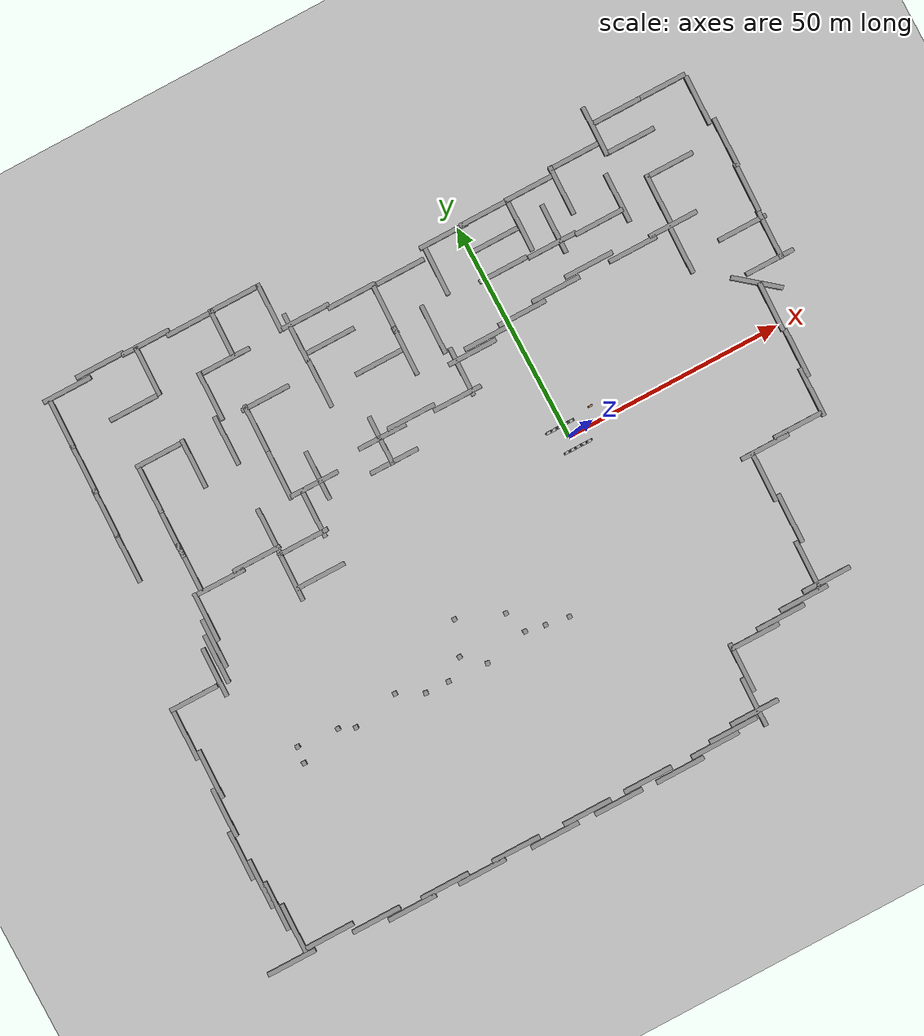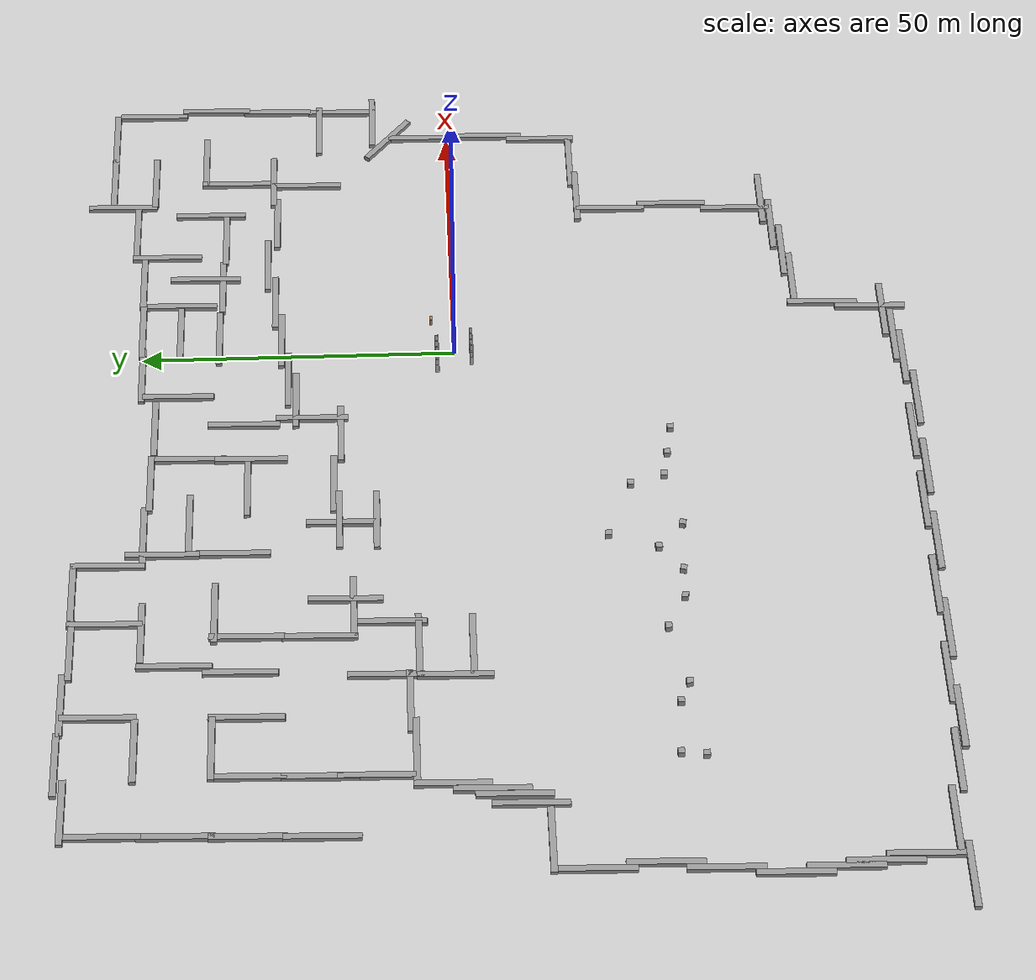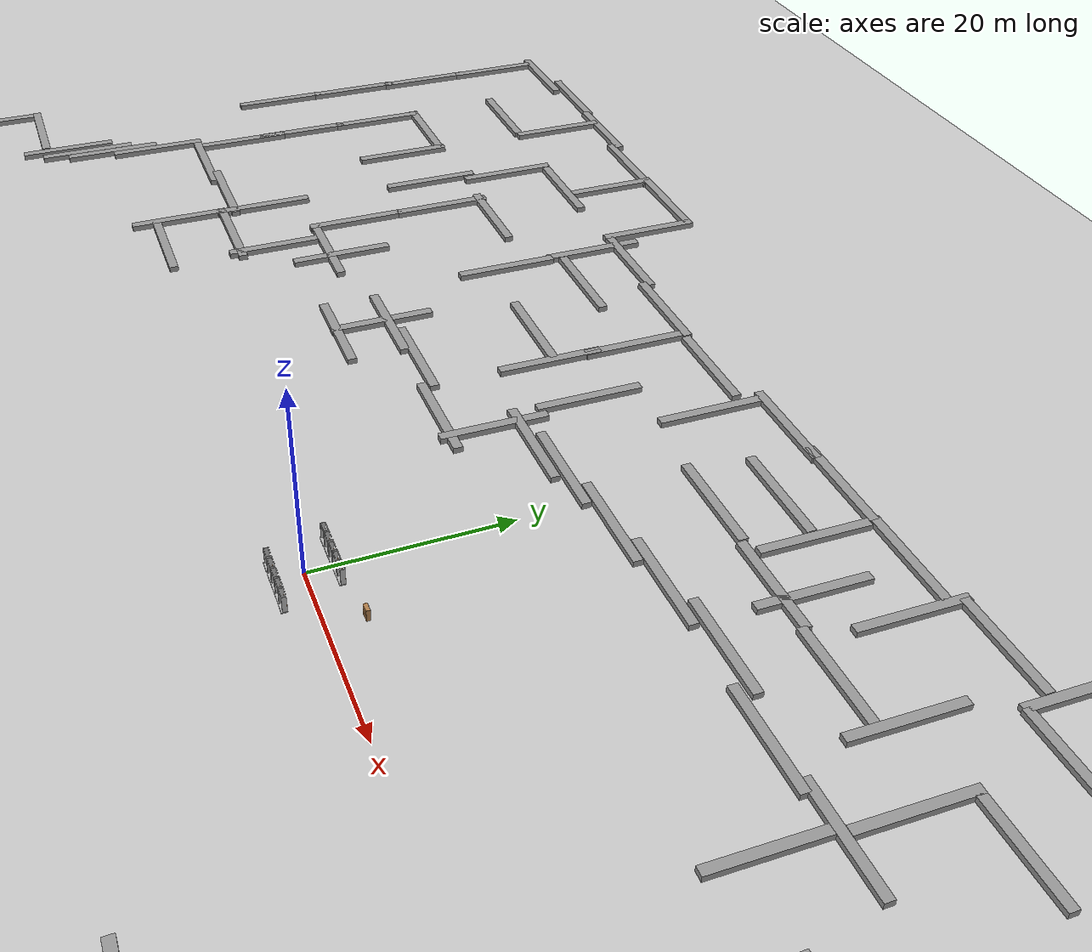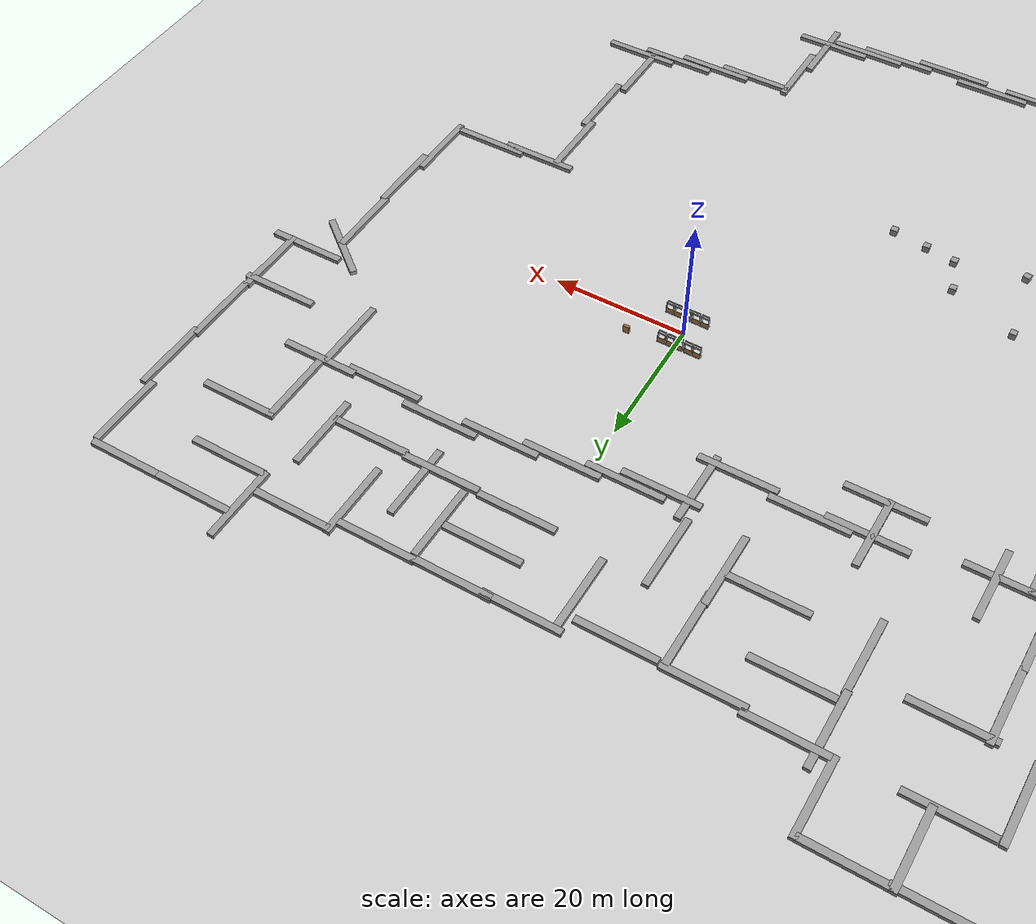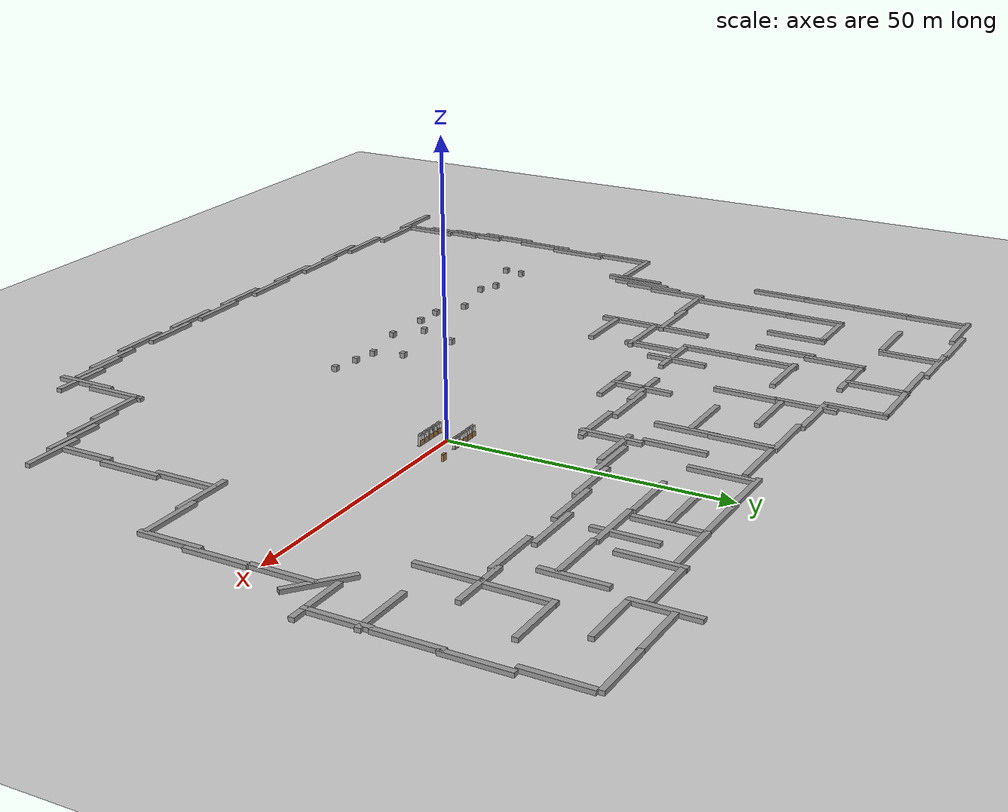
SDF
<sdf version="1.6">
 <world name="default">
  <light name="sun" type="directional">
   <pose>0 0 10 0 -0 0</pose>
   <diffuse>0.8 0.8 0.8 1</diffuse>
   <specular>0.1 0.1 0.1 1</specular>
   <attenuation>
    <range>1000</range>
    <constant>0.9</constant>
    <linear>0.01</linear>
    <quadratic>0.001</quadratic>
   </attenuation>
   <direction>-0.5 0.5 -1</direction>
  </light>
  <model name="ground_plane">
   <static>1</static>
   <link name="link">
    <collision name="collision">
     <geometry><plane><normal>0 0 1</normal><size>100 100</size></plane></geometry>
     <surface><friction><ode><mu>100</mu><mu2>50</mu2></ode></friction></surface>
    </collision>
    <visual name="visual">
     <cast_shadows>0</cast_shadows>
     <geometry><plane><normal>0 0 1</normal><size>100 100</size></plane></geometry>
     <material>
      <script><uri>file://media/materials/scripts/gazebo.material</uri><name>Gazebo/Grey</name></script>
     </material>
    </visual>
   </link>
  </model>
  <gravity>0 0 -9.8</gravity>
  <magnetic_field>6e-06 2.3e-05 -4.2e-05</magnetic_field>
  <atmosphere type="adiabatic"/>
  <physics name="default_physics" default="0" type="ode">
   <max_step_size>0.001</max_step_size>
   <real_time_factor>1</real_time_factor>
   <real_time_update_rate>1000</real_time_update_rate>
  </physics>
  <scene><ambient>0.4 0.4 0.4 1</ambient><background>0.7 0.7 0.7 1</background><shadows>1</shadows></scene>
  <spherical_coordinates>
   <surface_model>EARTH_WGS84</surface_model>
   <latitude_deg>0</latitude_deg>
   <longitude_deg>0</longitude_deg>
   <elevation>0</elevation>
   <heading_deg>0</heading_deg>
  </spherical_coordinates>
  <light name="user_spot_light_0" type="spot">
   <pose>-3.28458 5.52578 1 0 -0 0</pose>
   <diffuse>0.5 0.5 0.5 1</diffuse>
   <specular>0.1 0.1 0.1 1</specular>
   <direction>0 0 -1</direction>
   <attenuation>
    <range>20</range>
    <constant>0.5</constant>
    <linear>0.01</linear>
    <quadratic>0.001</quadratic>
   </attenuation>
   <cast_shadows>0</cast_shadows>
   <spot><inner_angle>0.6</inner_angle><outer_angle>1</outer_angle><falloff>1</falloff></spot>
  </light>
  <light name="user_spot_light_1" type="spot">
   <pose>1.94138 -4.66123 1 0 -0 0</pose>
   <diffuse>0.5 0.5 0.5 1</diffuse>
   <specular>0.1 0.1 0.1 1</specular>
   <direction>0 0 -1</direction>
   <attenuation>
    <range>20</range>
    <constant>0.5</constant>
    <linear>0.01</linear>
    <quadratic>0.001</quadratic>
   </attenuation>
   <cast_shadows>0</cast_shadows>
   <spot><inner_angle>0.6</inner_angle><outer_angle>1</outer_angle><falloff>1</falloff></spot>
  </light>
  <model name="frc2016_drawbridge">
   <link name="base">
    <inertial>
     <mass>10</mass>
     <pose>0 0 1 0 -0 0</pose>
     <inertia><ixx>3.64907</ixx><ixy>0</ixy><ixz>0</ixz><iyy>4.67075</iyy><iyz>0</iyz><izz>1.66649</izz></inertia>
    </inertial>
    <visual name="platform">
     <pose>0 0 0.0425 0 -0 0</pose>
     <geometry><box><size>1.27 0.5969 0.085</size></box></geometry>
    </visual>
    <collision name="platform">
     <pose>0 0 0.0425 0 -0 0</pose>
     <geometry><box><size>1.27 0.5969 0.085</size></box></geometry>
    </collision>
    <visual name="right_wall">
     <pose>0.55879 0.04444 0.889 0 -0 0</pose>
     <geometry><box><size>0.05715 0.45698 1.77165</size></box></geometry>
    </visual>
    <collision name="right_wall">
     <pose>0.55879 0.04444 0.889 0 -0 0</pose>
     <geometry><box><size>0.05715 0.45698 1.77165</size></box></geometry>
    </collision>
    <visual name="left_wall">
     <pose>-0.55879 0.04444 0.889 0 -0 0</pose>
     <geometry><box><size>0.05715 0.45698 1.77165</size></box></geometry>
    </visual>
    <collision name="left_wall">
     <pose>-0.55879 0.04444 0.889 0 -0 0</pose>
     <geometry><box><size>0.05715 0.45698 1.77165</size></box></geometry>
    </collision>
    <visual name="front_upper_wall">
     <pose>0 0.27611 1.84286 0 -0 0</pose>
     <geometry><box><size>1.1557 0.006347 0.254</size></box></geometry>
    </visual>
    <collision name="front_upper_wall">
     <pose>0 0.27611 1.84286 0 -0 0</pose>
     <geometry><box><size>1.1557 0.006347 0.254</size></box></geometry>
    </collision>
    <visual name="back_upper_wall">
     <pose>0 -0.18722 1.84286 0 -0 0</pose>
     <geometry><box><size>1.1557 0.006347 0.254</size></box></geometry>
    </visual>
    <collision name="back_upper_wall">
     <pose>0 -0.18722 1.84286 0 -0 0</pose>
     <geometry><box><size>1.1557 0.006347 0.254</size></box></geometry>
    </collision>
   </link>
   <link name="bridge">
    <pose>0 0.28245 0.50577 0 -0 0</pose>
    <inertial>
     <mass>2</mass>
     <pose>0 -0.28245 -0.50577 0 -0 0</pose>
     <inertia>
      <ixx>0.139361</ixx>
      <ixy>0</ixy>
      <ixz>0</ixz>
      <iyy>0.357088</iyy>
      <iyz>0</iyz>
      <izz>0.217741</izz>
     </inertia>
    </inertial>
    <visual name="visual">
     <geometry><box><size>1.14298 0.006347 0.9144</size></box></geometry>
     <material><script><name>Gazebo/WoodFloor</name><uri>__default__</uri></script></material>
    </visual>
    <collision name="collision"><geometry><box><size>1.14298 0.006347 0.9144</size></box></geometry></collision>
   </link>
   <joint name="bridge_joint" type="revolute">
    <pose>0 0 -0.4172 0 -0 0</pose>
    <parent>base</parent>
    <child>bridge</child>
    <axis>
     <xyz>1 0 0</xyz>
     <limit><lower>-2</lower><upper>0</upper></limit>
     <use_parent_model_frame>0</use_parent_model_frame>
     <dynamics><spring_reference>0</spring_reference><spring_stiffness>0</spring_stiffness></dynamics>
    </axis>
   </joint>
   <pose>-1.96364 -2.76284 -3e-06 -1e-06 -4e-06 -0.011689</pose>
  </model>
  <model name="frc2016_drawbridge_clone">
   <link name="base">
    <inertial>
     <mass>10</mass>
     <pose>0 0 1 0 -0 0</pose>
     <inertia><ixx>3.64907</ixx><ixy>0</ixy><ixz>0</ixz><iyy>4.67075</iyy><iyz>0</iyz><izz>1.66649</izz></inertia>
    </inertial>
    <visual name="platform">
     <pose>0 0 0.0425 0 -0 0</pose>
     <geometry><box><size>1.27 0.5969 0.085</size></box></geometry>
    </visual>
    <collision name="platform">
     <pose>0 0 0.0425 0 -0 0</pose>
     <geometry><box><size>1.27 0.5969 0.085</size></box></geometry>
    </collision>
    <visual name="right_wall">
     <pose>0.55879 0.04444 0.889 0 -0 0</pose>
     <geometry><box><size>0.05715 0.45698 1.77165</size></box></geometry>
    </visual>
    <collision name="right_wall">
     <pose>0.55879 0.04444 0.889 0 -0 0</pose>
     <geometry><box><size>0.05715 0.45698 1.77165</size></box></geometry>
    </collision>
    <visual name="left_wall">
     <pose>-0.55879 0.04444 0.889 0 -0 0</pose>
     <geometry><box><size>0.05715 0.45698 1.77165</size></box></geometry>
    </visual>
    <collision name="left_wall">
     <pose>-0.55879 0.04444 0.889 0 -0 0</pose>
     <geometry><box><size>0.05715 0.45698 1.77165</size></box></geometry>
    </collision>
    <visual name="front_upper_wall">
     <pose>0 0.27611 1.84286 0 -0 0</pose>
     <geometry><box><size>1.1557 0.006347 0.254</size></box></geometry>
    </visual>
    <collision name="front_upper_wall">
     <pose>0 0.27611 1.84286 0 -0 0</pose>
     <geometry><box><size>1.1557 0.006347 0.254</size></box></geometry>
    </collision>
    <visual name="back_upper_wall">
     <pose>0 -0.18722 1.84286 0 -0 0</pose>
     <geometry><box><size>1.1557 0.006347 0.254</size></box></geometry>
    </visual>
    <collision name="back_upper_wall">
     <pose>0 -0.18722 1.84286 0 -0 0</pose>
     <geometry><box><size>1.1557 0.006347 0.254</size></box></geometry>
    </collision>
   </link>
   <link name="bridge">
    <pose>0 0.28245 0.50577 0 -0 0</pose>
    <inertial>
     <mass>2</mass>
     <pose>0 -0.28245 -0.50577 0 -0 0</pose>
     <inertia>
      <ixx>0.139361</ixx>
      <ixy>0</ixy>
      <ixz>0</ixz>
      <iyy>0.357088</iyy>
      <iyz>0</iyz>
      <izz>0.217741</izz>
     </inertia>
    </inertial>
    <visual name="visual">
     <geometry><box><size>1.14298 0.006347 0.9144</size></box></geometry>
     <material><script><name>Gazebo/WoodFloor</name><uri>__default__</uri></script></material>
    </visual>
    <collision name="collision"><geometry><box><size>1.14298 0.006347 0.9144</size></box></geometry></collision>
   </link>
   <joint name="bridge_joint" type="revolute">
    <pose>0 0 -0.4172 0 -0 0</pose>
    <parent>base</parent>
    <child>bridge</child>
    <axis>
     <xyz>1 0 0</xyz>
     <limit><lower>-2</lower><upper>0</upper></limit>
     <use_parent_model_frame>0</use_parent_model_frame>
     <dynamics><spring_reference>0</spring_reference><spring_stiffness>0</spring_stiffness></dynamics>
    </axis>
   </joint>
   <pose>1.94909 2.77291 -3e-06 -2e-06 4e-06 -0.005775</pose>
  </model>
  <model name="frc2016_drawbridge_clone_0">
   <link name="base">
    <inertial>
     <mass>10</mass>
     <pose>0 0 1 0 -0 0</pose>
     <inertia><ixx>3.64907</ixx><ixy>0</ixy><ixz>0</ixz><iyy>4.67075</iyy><iyz>0</iyz><izz>1.66649</izz></inertia>
    </inertial>
    <visual name="platform">
     <pose>0 0 0.0425 0 -0 0</pose>
     <geometry><box><size>1.27 0.5969 0.085</size></box></geometry>
    </visual>
    <collision name="platform">
     <pose>0 0 0.0425 0 -0 0</pose>
     <geometry><box><size>1.27 0.5969 0.085</size></box></geometry>
    </collision>
    <visual name="right_wall">
     <pose>0.55879 0.04444 0.889 0 -0 0</pose>
     <geometry><box><size>0.05715 0.45698 1.77165</size></box></geometry>
    </visual>
    <collision name="right_wall">
     <pose>0.55879 0.04444 0.889 0 -0 0</pose>
     <geometry><box><size>0.05715 0.45698 1.77165</size></box></geometry>
    </collision>
    <visual name="left_wall">
     <pose>-0.55879 0.04444 0.889 0 -0 0</pose>
     <geometry><box><size>0.05715 0.45698 1.77165</size></box></geometry>
    </visual>
    <collision name="left_wall">
     <pose>-0.55879 0.04444 0.889 0 -0 0</pose>
     <geometry><box><size>0.05715 0.45698 1.77165</size></box></geometry>
    </collision>
    <visual name="front_upper_wall">
     <pose>0 0.27611 1.84286 0 -0 0</pose>
     <geometry><box><size>1.1557 0.006347 0.254</size></box></geometry>
    </visual>
    <collision name="front_upper_wall">
     <pose>0 0.27611 1.84286 0 -0 0</pose>
     <geometry><box><size>1.1557 0.006347 0.254</size></box></geometry>
    </collision>
    <visual name="back_upper_wall">
     <pose>0 -0.18722 1.84286 0 -0 0</pose>
     <geometry><box><size>1.1557 0.006347 0.254</size></box></geometry>
    </visual>
    <collision name="back_upper_wall">
     <pose>0 -0.18722 1.84286 0 -0 0</pose>
     <geometry><box><size>1.1557 0.006347 0.254</size></box></geometry>
    </collision>
   </link>
   <link name="bridge">
    <pose>0 0.28245 0.50577 0 -0 0</pose>
    <inertial>
     <mass>2</mass>
     <pose>0 -0.28245 -0.50577 0 -0 0</pose>
     <inertia>
      <ixx>0.139361</ixx>
      <ixy>0</ixy>
      <ixz>0</ixz>
      <iyy>0.357088</iyy>
      <iyz>0</iyz>
      <izz>0.217741</izz>
     </inertia>
    </inertial>
    <visual name="visual">
     <geometry><box><size>1.14298 0.006347 0.9144</size></box></geometry>
     <material><script><name>Gazebo/WoodFloor</name><uri>__default__</uri></script></material>
    </visual>
    <collision name="collision"><geometry><box><size>1.14298 0.006347 0.9144</size></box></geometry></collision>
   </link>
   <joint name="bridge_joint" type="revolute">
    <pose>0 0 -0.4172 0 -0 0</pose>
    <parent>base</parent>
    <child>bridge</child>
    <axis>
     <xyz>1 0 0</xyz>
     <limit><lower>-2</lower><upper>0</upper></limit>
     <use_parent_model_frame>0</use_parent_model_frame>
     <dynamics><spring_reference>0</spring_reference><spring_stiffness>0</spring_stiffness></dynamics>
    </axis>
   </joint>
   <pose>-0.58277 -2.76867 -3e-06 -3e-06 -4e-06 0.003704</pose>
  </model>
  <model name="frc2016_drawbridge_clone_1">
   <link name="base">
    <inertial>
     <mass>10</mass>
     <pose>0 0 1 0 -0 0</pose>
     <inertia><ixx>3.64907</ixx><ixy>0</ixy><ixz>0</ixz><iyy>4.67075</iyy><iyz>0</iyz><izz>1.66649</izz></inertia>
    </inertial>
    <visual name="platform">
     <pose>0 0 0.0425 0 -0 0</pose>
     <geometry><box><size>1.27 0.5969 0.085</size></box></geometry>
    </visual>
    <collision name="platform">
     <pose>0 0 0.0425 0 -0 0</pose>
     <geometry><box><size>1.27 0.5969 0.085</size></box></geometry>
    </collision>
    <visual name="right_wall">
     <pose>0.55879 0.04444 0.889 0 -0 0</pose>
     <geometry><box><size>0.05715 0.45698 1.77165</size></box></geometry>
    </visual>
    <collision name="right_wall">
     <pose>0.55879 0.04444 0.889 0 -0 0</pose>
     <geometry><box><size>0.05715 0.45698 1.77165</size></box></geometry>
    </collision>
    <visual name="left_wall">
     <pose>-0.55879 0.04444 0.889 0 -0 0</pose>
     <geometry><box><size>0.05715 0.45698 1.77165</size></box></geometry>
    </visual>
    <collision name="left_wall">
     <pose>-0.55879 0.04444 0.889 0 -0 0</pose>
     <geometry><box><size>0.05715 0.45698 1.77165</size></box></geometry>
    </collision>
    <visual name="front_upper_wall">
     <pose>0 0.27611 1.84286 0 -0 0</pose>
     <geometry><box><size>1.1557 0.006347 0.254</size></box></geometry>
    </visual>
    <collision name="front_upper_wall">
     <pose>0 0.27611 1.84286 0 -0 0</pose>
     <geometry><box><size>1.1557 0.006347 0.254</size></box></geometry>
    </collision>
    <visual name="back_upper_wall">
     <pose>0 -0.18722 1.84286 0 -0 0</pose>
     <geometry><box><size>1.1557 0.006347 0.254</size></box></geometry>
    </visual>
    <collision name="back_upper_wall">
     <pose>0 -0.18722 1.84286 0 -0 0</pose>
     <geometry><box><size>1.1557 0.006347 0.254</size></box></geometry>
    </collision>
   </link>
   <link name="bridge">
    <pose>0 0.28245 0.50577 0 -0 0</pose>
    <inertial>
     <mass>2</mass>
     <pose>0 -0.28245 -0.50577 0 -0 0</pose>
     <inertia>
      <ixx>0.139361</ixx>
      <ixy>0</ixy>
      <ixz>0</ixz>
      <iyy>0.357088</iyy>
      <iyz>0</iyz>
      <izz>0.217741</izz>
     </inertia>
    </inertial>
    <visual name="visual">
     <geometry><box><size>1.14298 0.006347 0.9144</size></box></geometry>
     <material><script><name>Gazebo/WoodFloor</name><uri>__default__</uri></script></material>
    </visual>
    <collision name="collision"><geometry><box><size>1.14298 0.006347 0.9144</size></box></geometry></collision>
   </link>
   <joint name="bridge_joint" type="revolute">
    <pose>0 0 -0.4172 0 -0 0</pose>
    <parent>base</parent>
    <child>bridge</child>
    <axis>
     <xyz>1 0 0</xyz>
     <limit><lower>-2</lower><upper>0</upper></limit>
     <use_parent_model_frame>0</use_parent_model_frame>
     <dynamics><spring_reference>0</spring_reference><spring_stiffness>0</spring_stiffness></dynamics>
    </axis>
   </joint>
   <pose>0.751563 -2.76216 -3e-06 -2e-06 -4e-06 -0.003048</pose>
  </model>
  <model name="frc2016_drawbridge_clone_2">
   <link name="base">
    <inertial>
     <mass>10</mass>
     <pose>0 0 1 0 -0 0</pose>
     <inertia><ixx>3.64907</ixx><ixy>0</ixy><ixz>0</ixz><iyy>4.67075</iyy><iyz>0</iyz><izz>1.66649</izz></inertia>
    </inertial>
    <visual name="platform">
     <pose>0 0 0.0425 0 -0 0</pose>
     <geometry><box><size>1.27 0.5969 0.085</size></box></geometry>
    </visual>
    <collision name="platform">
     <pose>0 0 0.0425 0 -0 0</pose>
     <geometry><box><size>1.27 0.5969 0.085</size></box></geometry>
    </collision>
    <visual name="right_wall">
     <pose>0.55879 0.04444 0.889 0 -0 0</pose>
     <geometry><box><size>0.05715 0.45698 1.77165</size></box></geometry>
    </visual>
    <collision name="right_wall">
     <pose>0.55879 0.04444 0.889 0 -0 0</pose>
     <geometry><box><size>0.05715 0.45698 1.77165</size></box></geometry>
    </collision>
    <visual name="left_wall">
     <pose>-0.55879 0.04444 0.889 0 -0 0</pose>
     <geometry><box><size>0.05715 0.45698 1.77165</size></box></geometry>
    </visual>
    <collision name="left_wall">
     <pose>-0.55879 0.04444 0.889 0 -0 0</pose>
     <geometry><box><size>0.05715 0.45698 1.77165</size></box></geometry>
    </collision>
    <visual name="front_upper_wall">
     <pose>0 0.27611 1.84286 0 -0 0</pose>
     <geometry><box><size>1.1557 0.006347 0.254</size></box></geometry>
    </visual>
    <collision name="front_upper_wall">
     <pose>0 0.27611 1.84286 0 -0 0</pose>
     <geometry><box><size>1.1557 0.006347 0.254</size></box></geometry>
    </collision>
    <visual name="back_upper_wall">
     <pose>0 -0.18722 1.84286 0 -0 0</pose>
     <geometry><box><size>1.1557 0.006347 0.254</size></box></geometry>
    </visual>
    <collision name="back_upper_wall">
     <pose>0 -0.18722 1.84286 0 -0 0</pose>
     <geometry><box><size>1.1557 0.006347 0.254</size></box></geometry>
    </collision>
   </link>
   <link name="bridge">
    <pose>0 0.28245 0.50577 0 -0 0</pose>
    <inertial>
     <mass>2</mass>
     <pose>0 -0.28245 -0.50577 0 -0 0</pose>
     <inertia>
      <ixx>0.139361</ixx>
      <ixy>0</ixy>
      <ixz>0</ixz>
      <iyy>0.357088</iyy>
      <iyz>0</iyz>
      <izz>0.217741</izz>
     </inertia>
    </inertial>
    <visual name="visual">
     <geometry><box><size>1.14298 0.006347 0.9144</size></box></geometry>
     <material><script><name>Gazebo/WoodFloor</name><uri>__default__</uri></script></material>
    </visual>
    <collision name="collision"><geometry><box><size>1.14298 0.006347 0.9144</size></box></geometry></collision>
   </link>
   <joint name="bridge_joint" type="revolute">
    <pose>0 0 -0.4172 0 -0 0</pose>
    <parent>base</parent>
    <child>bridge</child>
    <axis>
     <xyz>1 0 0</xyz>
     <limit><lower>-2</lower><upper>0</upper></limit>
     <use_parent_model_frame>0</use_parent_model_frame>
     <dynamics><spring_reference>0</spring_reference><spring_stiffness>0</spring_stiffness></dynamics>
    </axis>
   </joint>
   <pose>2.09359 -2.76255 0 0 -0 0.006067</pose>
  </model>
  <model name="frc2016_drawbridge_clone_3">
   <link name="base">
    <inertial>
     <mass>10</mass>
     <pose>0 0 1 0 -0 0</pose>
     <inertia><ixx>3.64907</ixx><ixy>0</ixy><ixz>0</ixz><iyy>4.67075</iyy><iyz>0</iyz><izz>1.66649</izz></inertia>
    </inertial>
    <visual name="platform">
     <pose>0 0 0.0425 0 -0 0</pose>
     <geometry><box><size>1.27 0.5969 0.085</size></box></geometry>
    </visual>
    <collision name="platform">
     <pose>0 0 0.0425 0 -0 0</pose>
     <geometry><box><size>1.27 0.5969 0.085</size></box></geometry>
    </collision>
    <visual name="right_wall">
     <pose>0.55879 0.04444 0.889 0 -0 0</pose>
     <geometry><box><size>0.05715 0.45698 1.77165</size></box></geometry>
    </visual>
    <collision name="right_wall">
     <pose>0.55879 0.04444 0.889 0 -0 0</pose>
     <geometry><box><size>0.05715 0.45698 1.77165</size></box></geometry>
    </collision>
    <visual name="left_wall">
     <pose>-0.55879 0.04444 0.889 0 -0 0</pose>
     <geometry><box><size>0.05715 0.45698 1.77165</size></box></geometry>
    </visual>
    <collision name="left_wall">
     <pose>-0.55879 0.04444 0.889 0 -0 0</pose>
     <geometry><box><size>0.05715 0.45698 1.77165</size></box></geometry>
    </collision>
    <visual name="front_upper_wall">
     <pose>0 0.27611 1.84286 0 -0 0</pose>
     <geometry><box><size>1.1557 0.006347 0.254</size></box></geometry>
    </visual>
    <collision name="front_upper_wall">
     <pose>0 0.27611 1.84286 0 -0 0</pose>
     <geometry><box><size>1.1557 0.006347 0.254</size></box></geometry>
    </collision>
    <visual name="back_upper_wall">
     <pose>0 -0.18722 1.84286 0 -0 0</pose>
     <geometry><box><size>1.1557 0.006347 0.254</size></box></geometry>
    </visual>
    <collision name="back_upper_wall">
     <pose>0 -0.18722 1.84286 0 -0 0</pose>
     <geometry><box><size>1.1557 0.006347 0.254</size></box></geometry>
    </collision>
   </link>
   <link name="bridge">
    <pose>0 0.28245 0.50577 0 -0 0</pose>
    <inertial>
     <mass>2</mass>
     <pose>0 -0.28245 -0.50577 0 -0 0</pose>
     <inertia>
      <ixx>0.139361</ixx>
      <ixy>0</ixy>
      <ixz>0</ixz>
      <iyy>0.357088</iyy>
      <iyz>0</iyz>
      <izz>0.217741</izz>
     </inertia>
    </inertial>
    <visual name="visual">
     <geometry><box><size>1.14298 0.006347 0.9144</size></box></geometry>
     <material><script><name>Gazebo/WoodFloor</name><uri>__default__</uri></script></material>
    </visual>
    <collision name="collision"><geometry><box><size>1.14298 0.006347 0.9144</size></box></geometry></collision>
   </link>
   <joint name="bridge_joint" type="revolute">
    <pose>0 0 -0.4172 0 -0 0</pose>
    <parent>base</parent>
    <child>bridge</child>
    <axis>
     <xyz>1 0 0</xyz>
     <limit><lower>-2</lower><upper>0</upper></limit>
     <use_parent_model_frame>0</use_parent_model_frame>
     <dynamics><spring_reference>0</spring_reference><spring_stiffness>0</spring_stiffness></dynamics>
    </axis>
   </joint>
   <pose>3.4132 -2.77332 0 0 0 -0.005096</pose>
  </model>
  <model name="frc2016_drawbridge_clone_4">
   <link name="base">
    <inertial>
     <mass>10</mass>
     <pose>0 0 1 0 -0 0</pose>
     <inertia><ixx>3.64907</ixx><ixy>0</ixy><ixz>0</ixz><iyy>4.67075</iyy><iyz>0</iyz><izz>1.66649</izz></inertia>
    </inertial>
    <visual name="platform">
     <pose>0 0 0.0425 0 -0 0</pose>
     <geometry><box><size>1.27 0.5969 0.085</size></box></geometry>
    </visual>
    <collision name="platform">
     <pose>0 0 0.0425 0 -0 0</pose>
     <geometry><box><size>1.27 0.5969 0.085</size></box></geometry>
    </collision>
    <visual name="right_wall">
     <pose>0.55879 0.04444 0.889 0 -0 0</pose>
     <geometry><box><size>0.05715 0.45698 1.77165</size></box></geometry>
    </visual>
    <collision name="right_wall">
     <pose>0.55879 0.04444 0.889 0 -0 0</pose>
     <geometry><box><size>0.05715 0.45698 1.77165</size></box></geometry>
    </collision>
    <visual name="left_wall">
     <pose>-0.55879 0.04444 0.889 0 -0 0</pose>
     <geometry><box><size>0.05715 0.45698 1.77165</size></box></geometry>
    </visual>
    <collision name="left_wall">
     <pose>-0.55879 0.04444 0.889 0 -0 0</pose>
     <geometry><box><size>0.05715 0.45698 1.77165</size></box></geometry>
    </collision>
    <visual name="front_upper_wall">
     <pose>0 0.27611 1.84286 0 -0 0</pose>
     <geometry><box><size>1.1557 0.006347 0.254</size></box></geometry>
    </visual>
    <collision name="front_upper_wall">
     <pose>0 0.27611 1.84286 0 -0 0</pose>
     <geometry><box><size>1.1557 0.006347 0.254</size></box></geometry>
    </collision>
    <visual name="back_upper_wall">
     <pose>0 -0.18722 1.84286 0 -0 0</pose>
     <geometry><box><size>1.1557 0.006347 0.254</size></box></geometry>
    </visual>
    <collision name="back_upper_wall">
     <pose>0 -0.18722 1.84286 0 -0 0</pose>
     <geometry><box><size>1.1557 0.006347 0.254</size></box></geometry>
    </collision>
   </link>
   <link name="bridge">
    <pose>0 0.28245 0.50577 0 -0 0</pose>
    <inertial>
     <mass>2</mass>
     <pose>0 -0.28245 -0.50577 0 -0 0</pose>
     <inertia>
      <ixx>0.139361</ixx>
      <ixy>0</ixy>
      <ixz>0</ixz>
      <iyy>0.357088</iyy>
      <iyz>0</iyz>
      <izz>0.217741</izz>
     </inertia>
    </inertial>
    <visual name="visual">
     <geometry><box><size>1.14298 0.006347 0.9144</size></box></geometry>
     <material><script><name>Gazebo/WoodFloor</name><uri>__default__</uri></script></material>
    </visual>
    <collision name="collision"><geometry><box><size>1.14298 0.006347 0.9144</size></box></geometry></collision>
   </link>
   <joint name="bridge_joint" type="revolute">
    <pose>0 0 -0.4172 0 -0 0</pose>
    <parent>base</parent>
    <child>bridge</child>
    <axis>
     <xyz>1 0 0</xyz>
     <limit><lower>-2</lower><upper>0</upper></limit>
     <use_parent_model_frame>0</use_parent_model_frame>
     <dynamics><spring_reference>0</spring_reference><spring_stiffness>0</spring_stiffness></dynamics>
    </axis>
   </joint>
   <pose>0.614342 2.77334 1e-06 0 1e-06 -0.011013</pose>
  </model>
  <model name="frc2016_drawbridge_clone_5">
   <link name="base">
    <inertial>
     <mass>10</mass>
     <pose>0 0 1 0 -0 0</pose>
     <inertia><ixx>3.64907</ixx><ixy>0</ixy><ixz>0</ixz><iyy>4.67075</iyy><iyz>0</iyz><izz>1.66649</izz></inertia>
    </inertial>
    <visual name="platform">
     <pose>0 0 0.0425 0 -0 0</pose>
     <geometry><box><size>1.27 0.5969 0.085</size></box></geometry>
    </visual>
    <collision name="platform">
     <pose>0 0 0.0425 0 -0 0</pose>
     <geometry><box><size>1.27 0.5969 0.085</size></box></geometry>
    </collision>
    <visual name="right_wall">
     <pose>0.55879 0.04444 0.889 0 -0 0</pose>
     <geometry><box><size>0.05715 0.45698 1.77165</size></box></geometry>
    </visual>
    <collision name="right_wall">
     <pose>0.55879 0.04444 0.889 0 -0 0</pose>
     <geometry><box><size>0.05715 0.45698 1.77165</size></box></geometry>
    </collision>
    <visual name="left_wall">
     <pose>-0.55879 0.04444 0.889 0 -0 0</pose>
     <geometry><box><size>0.05715 0.45698 1.77165</size></box></geometry>
    </visual>
    <collision name="left_wall">
     <pose>-0.55879 0.04444 0.889 0 -0 0</pose>
     <geometry><box><size>0.05715 0.45698 1.77165</size></box></geometry>
    </collision>
    <visual name="front_upper_wall">
     <pose>0 0.27611 1.84286 0 -0 0</pose>
     <geometry><box><size>1.1557 0.006347 0.254</size></box></geometry>
    </visual>
    <collision name="front_upper_wall">
     <pose>0 0.27611 1.84286 0 -0 0</pose>
     <geometry><box><size>1.1557 0.006347 0.254</size></box></geometry>
    </collision>
    <visual name="back_upper_wall">
     <pose>0 -0.18722 1.84286 0 -0 0</pose>
     <geometry><box><size>1.1557 0.006347 0.254</size></box></geometry>
    </visual>
    <collision name="back_upper_wall">
     <pose>0 -0.18722 1.84286 0 -0 0</pose>
     <geometry><box><size>1.1557 0.006347 0.254</size></box></geometry>
    </collision>
   </link>
   <link name="bridge">
    <pose>0 0.28245 0.50577 0 -0 0</pose>
    <inertial>
     <mass>2</mass>
     <pose>0 -0.28245 -0.50577 0 -0 0</pose>
     <inertia>
      <ixx>0.139361</ixx>
      <ixy>0</ixy>
      <ixz>0</ixz>
      <iyy>0.357088</iyy>
      <iyz>0</iyz>
      <izz>0.217741</izz>
     </inertia>
    </inertial>
    <visual name="visual">
     <geometry><box><size>1.14298 0.006347 0.9144</size></box></geometry>
     <material><script><name>Gazebo/WoodFloor</name><uri>__default__</uri></script></material>
    </visual>
    <collision name="collision"><geometry><box><size>1.14298 0.006347 0.9144</size></box></geometry></collision>
   </link>
   <joint name="bridge_joint" type="revolute">
    <pose>0 0 -0.4172 0 -0 0</pose>
    <parent>base</parent>
    <child>bridge</child>
    <axis>
     <xyz>1 0 0</xyz>
     <limit><lower>-2</lower><upper>0</upper></limit>
     <use_parent_model_frame>0</use_parent_model_frame>
     <dynamics><spring_reference>0</spring_reference><spring_stiffness>0</spring_stiffness></dynamics>
    </axis>
   </joint>
   <pose>-0.702293 2.76554 1e-06 0 -1e-06 -0.012168</pose>
  </model>
  <model name="frc2016_drawbridge_clone_5_clone">
   <link name="base">
    <inertial>
     <mass>10</mass>
     <pose>0 0 1 0 -0 0</pose>
     <inertia><ixx>3.64907</ixx><ixy>0</ixy><ixz>0</ixz><iyy>4.67075</iyy><iyz>0</iyz><izz>1.66649</izz></inertia>
    </inertial>
    <visual name="platform">
     <pose>0 0 0.0425 0 -0 0</pose>
     <geometry><box><size>1.27 0.5969 0.085</size></box></geometry>
    </visual>
    <collision name="platform">
     <pose>0 0 0.0425 0 -0 0</pose>
     <geometry><box><size>1.27 0.5969 0.085</size></box></geometry>
    </collision>
    <visual name="right_wall">
     <pose>0.55879 0.04444 0.889 0 -0 0</pose>
     <geometry><box><size>0.05715 0.45698 1.77165</size></box></geometry>
    </visual>
    <collision name="right_wall">
     <pose>0.55879 0.04444 0.889 0 -0 0</pose>
     <geometry><box><size>0.05715 0.45698 1.77165</size></box></geometry>
    </collision>
    <visual name="left_wall">
     <pose>-0.55879 0.04444 0.889 0 -0 0</pose>
     <geometry><box><size>0.05715 0.45698 1.77165</size></box></geometry>
    </visual>
    <collision name="left_wall">
     <pose>-0.55879 0.04444 0.889 0 -0 0</pose>
     <geometry><box><size>0.05715 0.45698 1.77165</size></box></geometry>
    </collision>
    <visual name="front_upper_wall">
     <pose>0 0.27611 1.84286 0 -0 0</pose>
     <geometry><box><size>1.1557 0.006347 0.254</size></box></geometry>
    </visual>
    <collision name="front_upper_wall">
     <pose>0 0.27611 1.84286 0 -0 0</pose>
     <geometry><box><size>1.1557 0.006347 0.254</size></box></geometry>
    </collision>
    <visual name="back_upper_wall">
     <pose>0 -0.18722 1.84286 0 -0 0</pose>
     <geometry><box><size>1.1557 0.006347 0.254</size></box></geometry>
    </visual>
    <collision name="back_upper_wall">
     <pose>0 -0.18722 1.84286 0 -0 0</pose>
     <geometry><box><size>1.1557 0.006347 0.254</size></box></geometry>
    </collision>
   </link>
   <link name="bridge">
    <pose>0 0.28245 0.50577 0 -0 0</pose>
    <inertial>
     <mass>2</mass>
     <pose>0 -0.28245 -0.50577 0 -0 0</pose>
     <inertia>
      <ixx>0.139361</ixx>
      <ixy>0</ixy>
      <ixz>0</ixz>
      <iyy>0.357088</iyy>
      <iyz>0</iyz>
      <izz>0.217741</izz>
     </inertia>
    </inertial>
    <visual name="visual">
     <geometry><box><size>1.14298 0.006347 0.9144</size></box></geometry>
     <material><script><name>Gazebo/WoodFloor</name><uri>__default__</uri></script></material>
    </visual>
    <collision name="collision"><geometry><box><size>1.14298 0.006347 0.9144</size></box></geometry></collision>
   </link>
   <joint name="bridge_joint" type="revolute">
    <pose>0 0 -0.4172 0 -0 0</pose>
    <parent>base</parent>
    <child>bridge</child>
    <axis>
     <xyz>1 0 0</xyz>
     <limit><lower>-2</lower><upper>0</upper></limit>
     <use_parent_model_frame>0</use_parent_model_frame>
     <dynamics><spring_reference>0</spring_reference><spring_stiffness>0</spring_stiffness></dynamics>
    </axis>
   </joint>
   <pose>-2.09998 2.76695 -4e-06 -3e-06 4e-06 -0.012662</pose>
  </model>
  <model name="frc2016_drawbridge_clone_5_clone_clone">
   <link name="base">
    <inertial>
     <mass>10</mass>
     <pose>0 0 1 0 -0 0</pose>
     <inertia><ixx>3.64907</ixx><ixy>0</ixy><ixz>0</ixz><iyy>4.67075</iyy><iyz>0</iyz><izz>1.66649</izz></inertia>
    </inertial>
    <visual name="platform">
     <pose>0 0 0.0425 0 -0 0</pose>
     <geometry><box><size>1.27 0.5969 0.085</size></box></geometry>
    </visual>
    <collision name="platform">
     <pose>0 0 0.0425 0 -0 0</pose>
     <geometry><box><size>1.27 0.5969 0.085</size></box></geometry>
    </collision>
    <visual name="right_wall">
     <pose>0.55879 0.04444 0.889 0 -0 0</pose>
     <geometry><box><size>0.05715 0.45698 1.77165</size></box></geometry>
    </visual>
    <collision name="right_wall">
     <pose>0.55879 0.04444 0.889 0 -0 0</pose>
     <geometry><box><size>0.05715 0.45698 1.77165</size></box></geometry>
    </collision>
    <visual name="left_wall">
     <pose>-0.55879 0.04444 0.889 0 -0 0</pose>
     <geometry><box><size>0.05715 0.45698 1.77165</size></box></geometry>
    </visual>
    <collision name="left_wall">
     <pose>-0.55879 0.04444 0.889 0 -0 0</pose>
     <geometry><box><size>0.05715 0.45698 1.77165</size></box></geometry>
    </collision>
    <visual name="front_upper_wall">
     <pose>0 0.27611 1.84286 0 -0 0</pose>
     <geometry><box><size>1.1557 0.006347 0.254</size></box></geometry>
    </visual>
    <collision name="front_upper_wall">
     <pose>0 0.27611 1.84286 0 -0 0</pose>
     <geometry><box><size>1.1557 0.006347 0.254</size></box></geometry>
    </collision>
    <visual name="back_upper_wall">
     <pose>0 -0.18722 1.84286 0 -0 0</pose>
     <geometry><box><size>1.1557 0.006347 0.254</size></box></geometry>
    </visual>
    <collision name="back_upper_wall">
     <pose>0 -0.18722 1.84286 0 -0 0</pose>
     <geometry><box><size>1.1557 0.006347 0.254</size></box></geometry>
    </collision>
   </link>
   <link name="bridge">
    <pose>0 0.28245 0.50577 0 -0 0</pose>
    <inertial>
     <mass>2</mass>
     <pose>0 -0.28245 -0.50577 0 -0 0</pose>
     <inertia>
      <ixx>0.139361</ixx>
      <ixy>0</ixy>
      <ixz>0</ixz>
      <iyy>0.357088</iyy>
      <iyz>0</iyz>
      <izz>0.217741</izz>
     </inertia>
    </inertial>
    <visual name="visual">
     <geometry><box><size>1.14298 0.006347 0.9144</size></box></geometry>
     <material><script><name>Gazebo/WoodFloor</name><uri>__default__</uri></script></material>
    </visual>
    <collision name="collision"><geometry><box><size>1.14298 0.006347 0.9144</size></box></geometry></collision>
   </link>
   <joint name="bridge_joint" type="revolute">
    <pose>0 0 -0.4172 0 -0 0</pose>
    <parent>base</parent>
    <child>bridge</child>
    <axis>
     <xyz>1 0 0</xyz>
     <limit><lower>-2</lower><upper>0</upper></limit>
     <use_parent_model_frame>0</use_parent_model_frame>
     <dynamics><spring_reference>0</spring_reference><spring_stiffness>0</spring_stiffness></dynamics>
    </axis>
   </joint>
   <pose>-3.41388 2.76245 0 0 0 -0.005391</pose>
  </model>
  <model name="bookshelf">
   <static>1</static>
   <link name="link">
    <inertial><mass>1</mass></inertial>
    <collision name="back">
     <pose>0 0.005 0.6 0 -0 0</pose>
     <geometry><box><size>0.9 0.01 1.2</size></box></geometry>
    </collision>
    <visual name="visual1">
     <pose>0 0.005 0.6 0 -0 0</pose>
     <geometry><box><size>0.9 0.01 1.2</size></box></geometry>
     <material>
      <script><uri>file://media/materials/scripts/gazebo.material</uri><name>Gazebo/Wood</name></script>
     </material>
    </visual>
    <collision name="left_side">
     <pose>0.45 -0.195 0.6 0 -0 0</pose>
     <geometry><box><size>0.02 0.4 1.2</size></box></geometry>
    </collision>
    <visual name="visual2">
     <pose>0.45 -0.195 0.6 0 -0 0</pose>
     <geometry><box><size>0.02 0.4 1.2</size></box></geometry>
     <material>
      <script><uri>file://media/materials/scripts/gazebo.material</uri><name>Gazebo/Wood</name></script>
     </material>
    </visual>
    <collision name="right_side">
     <pose>-0.45 -0.195 0.6 0 -0 0</pose>
     <geometry><box><size>0.02 0.4 1.2</size></box></geometry>
    </collision>
    <visual name="visual3">
     <pose>-0.45 -0.195 0.6 0 -0 0</pose>
     <geometry><box><size>0.02 0.4 1.2</size></box></geometry>
     <material>
      <script><uri>file://media/materials/scripts/gazebo.material</uri><name>Gazebo/Wood</name></script>
     </material>
    </visual>
    <collision name="bottom">
     <pose>0 -0.195 0.03 0 -0 0</pose>
     <geometry><box><size>0.88 0.4 0.06</size></box></geometry>
    </collision>
    <visual name="visual4">
     <pose>0 -0.195 0.03 0 -0 0</pose>
     <geometry><box><size>0.88 0.4 0.06</size></box></geometry>
     <material>
      <script><uri>file://media/materials/scripts/gazebo.material</uri><name>Gazebo/Wood</name></script>
     </material>
    </visual>
    <collision name="top">
     <pose>0 -0.195 1.19 0 -0 0</pose>
     <geometry><box><size>0.88 0.4 0.02</size></box></geometry>
    </collision>
    <visual name="visual5">
     <pose>0 -0.195 1.19 0 -0 0</pose>
     <geometry><box><size>0.88 0.4 0.02</size></box></geometry>
     <material>
      <script><uri>file://media/materials/scripts/gazebo.material</uri><name>Gazebo/Wood</name></script>
     </material>
    </visual>
    <collision name="low_shelf">
     <pose>0 -0.195 0.43 0 -0 0</pose>
     <geometry><box><size>0.88 0.4 0.02</size></box></geometry>
    </collision>
    <visual name="visual6">
     <pose>0 -0.195 0.43 0 -0 0</pose>
     <geometry><box><size>0.88 0.4 0.02</size></box></geometry>
     <material>
      <script><uri>file://media/materials/scripts/gazebo.material</uri><name>Gazebo/Wood</name></script>
     </material>
    </visual>
    <collision name="high_shelf">
     <pose>0 -0.195 0.8 0 -0 0</pose>
     <geometry><box><size>0.88 0.4 0.02</size></box></geometry>
    </collision>
    <visual name="visual7">
     <pose>0 -0.195 0.8 0 -0 0</pose>
     <geometry><box><size>0.88 0.4 0.02</size></box></geometry>
     <material>
      <script><uri>file://media/materials/scripts/gazebo.material</uri><name>Gazebo/Wood</name></script>
     </material>
    </visual>
   </link>
   <pose>6.99919 3.80873 0 0 -0 0</pose>
  </model>
  <model name="unit_box_0_clone_14_clone_0_clone">
   <pose>-17.7844 -33.4735 0.509209 -0.000175 -8e-05 0.023709</pose>
   <link name="link">
    <inertial>
     <mass>1</mass>
     <inertia>
      <ixx>0.166667</ixx>
      <ixy>0</ixy>
      <ixz>0</ixz>
      <iyy>0.166667</iyy>
      <iyz>0</iyz>
      <izz>0.166667</izz>
     </inertia>
    </inertial>
    <collision name="collision"><geometry><box><size>1 1 1</size></box></geometry></collision>
    <visual name="visual">
     <geometry><box><size>1 1 1</size></box></geometry>
     <material>
      <script><name>Gazebo/Grey</name><uri>file://media/materials/scripts/gazebo.material</uri></script>
     </material>
    </visual>
   </link>
  </model>
  <model name="unit_box_0_clone_14_clone_0_clone_0">
   <pose>-23.0617 -32.6292 0.509991 0 -0 0.007397</pose>
   <link name="link">
    <inertial>
     <mass>1</mass>
     <inertia>
      <ixx>0.166667</ixx>
      <ixy>0</ixy>
      <ixz>0</ixz>
      <iyy>0.166667</iyy>
      <iyz>0</iyz>
      <izz>0.166667</izz>
     </inertia>
    </inertial>
    <collision name="collision"><geometry><box><size>1 1 1</size></box></geometry></collision>
    <visual name="visual">
     <geometry><box><size>1 1 1</size></box></geometry>
     <material>
      <script><name>Gazebo/Grey</name><uri>file://media/materials/scripts/gazebo.material</uri></script>
     </material>
    </visual>
   </link>
  </model>
  <model name="unit_box_0_clone_14_clone_0_clone_1">
   <pose>-27.5467 -31.8428 0.509943 -2.3e-05 -3e-06 0.000746</pose>
   <link name="link">
    <inertial>
     <mass>1</mass>
     <inertia>
      <ixx>0.166667</ixx>
      <ixy>0</ixy>
      <ixz>0</ixz>
      <iyy>0.166667</iyy>
      <iyz>0</iyz>
      <izz>0.166667</izz>
     </inertia>
    </inertial>
    <collision name="collision"><geometry><box><size>1 1 1</size></box></geometry></collision>
    <visual name="visual">
     <geometry><box><size>1 1 1</size></box></geometry>
     <material>
      <script><name>Gazebo/Grey</name><uri>file://media/materials/scripts/gazebo.material</uri></script>
     </material>
    </visual>
   </link>
  </model>
  <model name="unit_box_0_clone_14_clone_0_clone_2">
   <pose>-29.273 -26.5507 0.5 0 -0 5e-06</pose>
   <link name="link">
    <inertial>
     <mass>1</mass>
     <inertia>
      <ixx>0.166667</ixx>
      <ixy>0</ixy>
      <ixz>0</ixz>
      <iyy>0.166667</iyy>
      <iyz>0</iyz>
      <izz>0.166667</izz>
     </inertia>
    </inertial>
    <collision name="collision"><geometry><box><size>1 1 1</size></box></geometry></collision>
    <visual name="visual">
     <geometry><box><size>1 1 1</size></box></geometry>
     <material>
      <script><name>Gazebo/Grey</name><uri>file://media/materials/scripts/gazebo.material</uri></script>
     </material>
    </visual>
   </link>
  </model>
  <model name="unit_box_0_clone_14_clone_0_clone_3">
   <pose>-39.4589 -22.5498 0.5 0 -0 0</pose>
   <link name="link">
    <inertial>
     <mass>1</mass>
     <inertia>
      <ixx>0.166667</ixx>
      <ixy>0</ixy>
      <ixz>0</ixz>
      <iyy>0.166667</iyy>
      <iyz>0</iyz>
      <izz>0.166667</izz>
     </inertia>
    </inertial>
    <collision name="collision"><geometry><box><size>1 1 1</size></box></geometry></collision>
    <visual name="visual">
     <geometry><box><size>1 1 1</size></box></geometry>
     <material>
      <script><name>Gazebo/Grey</name><uri>file://media/materials/scripts/gazebo.material</uri></script>
     </material>
    </visual>
   </link>
  </model>
  <model name="unit_box_0_clone_14_clone_0_clone_4">
   <pose>-37.6665 -34.022 0.51 0 0 -0.200755</pose>
   <link name="link">
    <inertial>
     <mass>1</mass>
     <inertia>
      <ixx>0.166667</ixx>
      <ixy>0</ixy>
      <ixz>0</ixz>
      <iyy>0.166667</iyy>
      <iyz>0</iyz>
      <izz>0.166667</izz>
     </inertia>
    </inertial>
    <collision name="collision"><geometry><box><size>1 1 1</size></box></geometry></collision>
    <visual name="visual">
     <geometry><box><size>1 1 1</size></box></geometry>
     <material>
      <script><name>Gazebo/Grey</name><uri>file://media/materials/scripts/gazebo.material</uri></script>
     </material>
    </visual>
   </link>
  </model>
  <model name="unit_box_0_clone_14_clone_0_clone_5">
   <pose>-42.2225 -30.0694 0.509991 0 -0 0.112697</pose>
   <link name="link">
    <inertial>
     <mass>1</mass>
     <inertia>
      <ixx>0.166667</ixx>
      <ixy>0</ixy>
      <ixz>0</ixz>
      <iyy>0.166667</iyy>
      <iyz>0</iyz>
      <izz>0.166667</izz>
     </inertia>
    </inertial>
    <collision name="collision"><geometry><box><size>1 1 1</size></box></geometry></collision>
    <visual name="visual">
     <geometry><box><size>1 1 1</size></box></geometry>
     <material>
      <script><name>Gazebo/Grey</name><uri>file://media/materials/scripts/gazebo.material</uri></script>
     </material>
    </visual>
   </link>
  </model>
  <model name="unit_box_0_clone_14_clone_0_clone_6">
   <pose>-46.7396 -33.5332 0.509904 -4.8e-05 -7e-06 -0.105575</pose>
   <link name="link">
    <inertial>
     <mass>1</mass>
     <inertia>
      <ixx>0.166667</ixx>
      <ixy>0</ixy>
      <ixz>0</ixz>
      <iyy>0.166667</iyy>
      <iyz>0</iyz>
      <izz>0.166667</izz>
     </inertia>
    </inertial>
    <collision name="collision"><geometry><box><size>1 1 1</size></box></geometry></collision>
    <visual name="visual">
     <geometry><box><size>1 1 1</size></box></geometry>
     <material>
      <script><name>Gazebo/Grey</name><uri>file://media/materials/scripts/gazebo.material</uri></script>
     </material>
    </visual>
   </link>
  </model>
  <model name="unit_box_0_clone_14_clone_0_clone_7">
   <pose>-52.1024 -33.3912 0.509024 0.000446 0.000106 -0.168583</pose>
   <link name="link">
    <inertial>
     <mass>1</mass>
     <inertia>
      <ixx>0.166667</ixx>
      <ixy>0</ixy>
      <ixz>0</ixz>
      <iyy>0.166667</iyy>
      <iyz>0</iyz>
      <izz>0.166667</izz>
     </inertia>
    </inertial>
    <collision name="collision"><geometry><box><size>1 1 1</size></box></geometry></collision>
    <visual name="visual">
     <geometry><box><size>1 1 1</size></box></geometry>
     <material>
      <script><name>Gazebo/Grey</name><uri>file://media/materials/scripts/gazebo.material</uri></script>
     </material>
    </visual>
   </link>
  </model>
  <model name="unit_box_0_clone_14_clone_0_clone_8">
   <pose>-57.9322 -30.4622 0.509998 -3e-06 2e-06 0.002409</pose>
   <link name="link">
    <inertial>
     <mass>1</mass>
     <inertia>
      <ixx>0.166667</ixx>
      <ixy>0</ixy>
      <ixz>0</ixz>
      <iyy>0.166667</iyy>
      <iyz>0</iyz>
      <izz>0.166667</izz>
     </inertia>
    </inertial>
    <collision name="collision"><geometry><box><size>1 1 1</size></box></geometry></collision>
    <visual name="visual">
     <geometry><box><size>1 1 1</size></box></geometry>
     <material>
      <script><name>Gazebo/Grey</name><uri>file://media/materials/scripts/gazebo.material</uri></script>
     </material>
    </visual>
   </link>
  </model>
  <model name="unit_box_0_clone_14_clone_0_clone_9">
   <pose>-68.4941 -32.8502 0.509943 1.9e-05 -1e-06 0.002646</pose>
   <link name="link">
    <inertial>
     <mass>1</mass>
     <inertia>
      <ixx>0.166667</ixx>
      <ixy>0</ixy>
      <ixz>0</ixz>
      <iyy>0.166667</iyy>
      <iyz>0</iyz>
      <izz>0.166667</izz>
     </inertia>
    </inertial>
    <collision name="collision"><geometry><box><size>1 1 1</size></box></geometry></collision>
    <visual name="visual">
     <geometry><box><size>1 1 1</size></box></geometry>
     <material>
      <script><name>Gazebo/Grey</name><uri>file://media/materials/scripts/gazebo.material</uri></script>
     </material>
    </visual>
   </link>
  </model>
  <model name="unit_box_0_clone_14_clone_0_clone_10">
   <pose>-71.9723 -31.3192 0.509989 0 0 -0.000396</pose>
   <link name="link">
    <inertial>
     <mass>1</mass>
     <inertia>
      <ixx>0.166667</ixx>
      <ixy>0</ixy>
      <ixz>0</ixz>
      <iyy>0.166667</iyy>
      <iyz>0</iyz>
      <izz>0.166667</izz>
     </inertia>
    </inertial>
    <collision name="collision"><geometry><box><size>1 1 1</size></box></geometry></collision>
    <visual name="visual">
     <geometry><box><size>1 1 1</size></box></geometry>
     <material>
      <script><name>Gazebo/Grey</name><uri>file://media/materials/scripts/gazebo.material</uri></script>
     </material>
    </visual>
   </link>
  </model>
  <model name="unit_box_0_clone_14_clone_0_clone_11">
   <pose>-81.7303 -34.3592 0.51 0 0 -0.008529</pose>
   <link name="link">
    <inertial>
     <mass>1</mass>
     <inertia>
      <ixx>0.166667</ixx>
      <ixy>0</ixy>
      <ixz>0</ixz>
      <iyy>0.166667</iyy>
      <iyz>0</iyz>
      <izz>0.166667</izz>
     </inertia>
    </inertial>
    <collision name="collision"><geometry><box><size>1 1 1</size></box></geometry></collision>
    <visual name="visual">
     <geometry><box><size>1 1 1</size></box></geometry>
     <material>
      <script><name>Gazebo/Grey</name><uri>file://media/materials/scripts/gazebo.material</uri></script>
     </material>
    </visual>
   </link>
  </model>
  <model name="unit_box_0_clone_14_clone_0_clone_12">
   <pose>-81.2751 -30.6674 0.504284 0.004435 0.001759 0.080386</pose>
   <link name="link">
    <inertial>
     <mass>1</mass>
     <inertia>
      <ixx>0.166667</ixx>
      <ixy>0</ixy>
      <ixz>0</ixz>
      <iyy>0.166667</iyy>
      <iyz>0</iyz>
      <izz>0.166667</izz>
     </inertia>
    </inertial>
    <collision name="collision"><geometry><box><size>1 1 1</size></box></geometry></collision>
    <visual name="visual">
     <geometry><box><size>1 1 1</size></box></geometry>
     <material>
      <script><name>Gazebo/Grey</name><uri>file://media/materials/scripts/gazebo.material</uri></script>
     </material>
    </visual>
   </link>
  </model>
  <model name="unit_box_0_static">
   <link name="link">
    <inertial>
     <mass>11.3696</mass>
     <inertia><ixx>1.89495</ixx><ixy>0</ixy><ixz>0</ixz><iyy>123.426</iyy><iyz>0</iyz><izz>123.426</izz></inertia>
    </inertial>
    <kinematic>1</kinematic>
    <visual name="visual">
     <geometry><box><size>11.3696 1 1</size></box></geometry>
     <material>
      <script><name>Gazebo/Grey</name><uri>file://media/materials/scripts/gazebo.material</uri></script>
      <ambient>0.3 0.3 0.3 1</ambient>
      <diffuse>0.7 0.7 0.7 1</diffuse>
      <specular>0.01 0.01 0.01 1</specular>
      <emissive>0 0 0 1</emissive>
     </material>
    </visual>
    <collision name="collision">
     <geometry><box><size>11.3696 1 1</size></box></geometry>
     <surface>
      <friction>
       <ode><mu>1</mu><mu2>1</mu2><fdir1>0 0 0</fdir1><slip1>0</slip1><slip2>0</slip2></ode>
       <torsional>
        <coefficient>1</coefficient>
        <patch_radius>0</patch_radius>
        <surface_radius>0</surface_radius>
        <use_patch_radius>1</use_patch_radius>
        <ode><slip>0</slip></ode>
       </torsional>
      </friction>
      <bounce><restitution_coefficient>0</restitution_coefficient><threshold>1e+06</threshold></bounce>
      <contact>
       <collide_without_contact>0</collide_without_contact>
       <collide_without_contact_bitmask>1</collide_without_contact_bitmask>
       <collide_bitmask>1</collide_bitmask>
       <ode>
        <soft_cfm>0</soft_cfm>
        <soft_erp>0.2</soft_erp>
        <kp>1e+13</kp>
        <kd>1</kd>
        <max_vel>0.01</max_vel>
        <min_depth>0</min_depth>
       </ode>
       <bullet>
        <split_impulse>1</split_impulse>
        <split_impulse_penetration_threshold>-0.01</split_impulse_penetration_threshold>
        <soft_cfm>0</soft_cfm>
        <soft_erp>0.2</soft_erp>
        <kp>1e+13</kp>
        <kd>1</kd>
       </bullet>
      </contact>
     </surface>
    </collision>
   </link>
   <static>1</static>
   <pose>-83.8691 -70.7361 0 0 -0 0</pose>
  </model>
  <model name="unit_box_0_static_clone">
   <link name="link">
    <inertial>
     <mass>11.3696</mass>
     <inertia><ixx>1.89495</ixx><ixy>0</ixy><ixz>0</ixz><iyy>123.426</iyy><iyz>0</iyz><izz>123.426</izz></inertia>
    </inertial>
    <kinematic>1</kinematic>
    <visual name="visual">
     <geometry><box><size>11.3696 1 1</size></box></geometry>
     <material>
      <script><name>Gazebo/Grey</name><uri>file://media/materials/scripts/gazebo.material</uri></script>
      <ambient>0.3 0.3 0.3 1</ambient>
      <diffuse>0.7 0.7 0.7 1</diffuse>
      <specular>0.01 0.01 0.01 1</specular>
      <emissive>0 0 0 1</emissive>
     </material>
    </visual>
    <collision name="collision">
     <geometry><box><size>11.3696 1 1</size></box></geometry>
     <surface>
      <friction>
       <ode><mu>1</mu><mu2>1</mu2><fdir1>0 0 0</fdir1><slip1>0</slip1><slip2>0</slip2></ode>
       <torsional>
        <coefficient>1</coefficient>
        <patch_radius>0</patch_radius>
        <surface_radius>0</surface_radius>
        <use_patch_radius>1</use_patch_radius>
        <ode><slip>0</slip></ode>
       </torsional>
      </friction>
      <bounce><restitution_coefficient>0</restitution_coefficient><threshold>1e+06</threshold></bounce>
      <contact>
       <collide_without_contact>0</collide_without_contact>
       <collide_without_contact_bitmask>1</collide_without_contact_bitmask>
       <collide_bitmask>1</collide_bitmask>
       <ode>
        <soft_cfm>0</soft_cfm>
        <soft_erp>0.2</soft_erp>
        <kp>1e+13</kp>
        <kd>1</kd>
        <max_vel>0.01</max_vel>
        <min_depth>0</min_depth>
       </ode>
       <bullet>
        <split_impulse>1</split_impulse>
        <split_impulse_penetration_threshold>-0.01</split_impulse_penetration_threshold>
        <soft_cfm>0</soft_cfm>
        <soft_erp>0.2</soft_erp>
        <kp>1e+13</kp>
        <kd>1</kd>
       </bullet>
      </contact>
     </surface>
    </collision>
   </link>
   <static>1</static>
   <pose>-76.0243 -72.0413 0 0 -0 0</pose>
  </model>
  <model name="unit_box_0_static_clone_0">
   <link name="link">
    <inertial>
     <mass>11.3696</mass>
     <inertia><ixx>1.89495</ixx><ixy>0</ixy><ixz>0</ixz><iyy>123.426</iyy><iyz>0</iyz><izz>123.426</izz></inertia>
    </inertial>
    <kinematic>1</kinematic>
    <visual name="visual">
     <geometry><box><size>11.3696 1 1</size></box></geometry>
     <material>
      <script><name>Gazebo/Grey</name><uri>file://media/materials/scripts/gazebo.material</uri></script>
      <ambient>0.3 0.3 0.3 1</ambient>
      <diffuse>0.7 0.7 0.7 1</diffuse>
      <specular>0.01 0.01 0.01 1</specular>
      <emissive>0 0 0 1</emissive>
     </material>
    </visual>
    <collision name="collision">
     <geometry><box><size>11.3696 1 1</size></box></geometry>
     <surface>
      <friction>
       <ode><mu>1</mu><mu2>1</mu2><fdir1>0 0 0</fdir1><slip1>0</slip1><slip2>0</slip2></ode>
       <torsional>
        <coefficient>1</coefficient>
        <patch_radius>0</patch_radius>
        <surface_radius>0</surface_radius>
        <use_patch_radius>1</use_patch_radius>
        <ode><slip>0</slip></ode>
       </torsional>
      </friction>
      <bounce><restitution_coefficient>0</restitution_coefficient><threshold>1e+06</threshold></bounce>
      <contact>
       <collide_without_contact>0</collide_without_contact>
       <collide_without_contact_bitmask>1</collide_without_contact_bitmask>
       <collide_bitmask>1</collide_bitmask>
       <ode>
        <soft_cfm>0</soft_cfm>
        <soft_erp>0.2</soft_erp>
        <kp>1e+13</kp>
        <kd>1</kd>
        <max_vel>0.01</max_vel>
        <min_depth>0</min_depth>
       </ode>
       <bullet>
        <split_impulse>1</split_impulse>
        <split_impulse_penetration_threshold>-0.01</split_impulse_penetration_threshold>
        <soft_cfm>0</soft_cfm>
        <soft_erp>0.2</soft_erp>
        <kp>1e+13</kp>
        <kd>1</kd>
       </bullet>
      </contact>
     </surface>
    </collision>
   </link>
   <static>1</static>
   <pose>-67.7608 -71.2481 0 0 -0 0</pose>
  </model>
  <model name="unit_box_0_static_clone_1">
   <link name="link">
    <inertial>
     <mass>11.3696</mass>
     <inertia><ixx>1.89495</ixx><ixy>0</ixy><ixz>0</ixz><iyy>123.426</iyy><iyz>0</iyz><izz>123.426</izz></inertia>
    </inertial>
    <kinematic>1</kinematic>
    <visual name="visual">
     <geometry><box><size>11.3696 1 1</size></box></geometry>
     <material>
      <script><name>Gazebo/Grey</name><uri>file://media/materials/scripts/gazebo.material</uri></script>
      <ambient>0.3 0.3 0.3 1</ambient>
      <diffuse>0.7 0.7 0.7 1</diffuse>
      <specular>0.01 0.01 0.01 1</specular>
      <emissive>0 0 0 1</emissive>
     </material>
    </visual>
    <collision name="collision">
     <geometry><box><size>11.3696 1 1</size></box></geometry>
     <surface>
      <friction>
       <ode><mu>1</mu><mu2>1</mu2><fdir1>0 0 0</fdir1><slip1>0</slip1><slip2>0</slip2></ode>
       <torsional>
        <coefficient>1</coefficient>
        <patch_radius>0</patch_radius>
        <surface_radius>0</surface_radius>
        <use_patch_radius>1</use_patch_radius>
        <ode><slip>0</slip></ode>
       </torsional>
      </friction>
      <bounce><restitution_coefficient>0</restitution_coefficient><threshold>1e+06</threshold></bounce>
      <contact>
       <collide_without_contact>0</collide_without_contact>
       <collide_without_contact_bitmask>1</collide_without_contact_bitmask>
       <collide_bitmask>1</collide_bitmask>
       <ode>
        <soft_cfm>0</soft_cfm>
        <soft_erp>0.2</soft_erp>
        <kp>1e+13</kp>
        <kd>1</kd>
        <max_vel>0.01</max_vel>
        <min_depth>0</min_depth>
       </ode>
       <bullet>
        <split_impulse>1</split_impulse>
        <split_impulse_penetration_threshold>-0.01</split_impulse_penetration_threshold>
        <soft_cfm>0</soft_cfm>
        <soft_erp>0.2</soft_erp>
        <kp>1e+13</kp>
        <kd>1</kd>
       </bullet>
      </contact>
     </surface>
    </collision>
   </link>
   <static>1</static>
   <pose>-59.4096 -72.2912 0 0 -0 0</pose>
  </model>
  <model name="unit_box_0_static_clone_2">
   <link name="link">
    <inertial>
     <mass>11.3696</mass>
     <inertia><ixx>1.89495</ixx><ixy>0</ixy><ixz>0</ixz><iyy>123.426</iyy><iyz>0</iyz><izz>123.426</izz></inertia>
    </inertial>
    <kinematic>1</kinematic>
    <visual name="visual">
     <geometry><box><size>11.3696 1 1</size></box></geometry>
     <material>
      <script><name>Gazebo/Grey</name><uri>file://media/materials/scripts/gazebo.material</uri></script>
      <ambient>0.3 0.3 0.3 1</ambient>
      <diffuse>0.7 0.7 0.7 1</diffuse>
      <specular>0.01 0.01 0.01 1</specular>
      <emissive>0 0 0 1</emissive>
     </material>
    </visual>
    <collision name="collision">
     <geometry><box><size>11.3696 1 1</size></box></geometry>
     <surface>
      <friction>
       <ode><mu>1</mu><mu2>1</mu2><fdir1>0 0 0</fdir1><slip1>0</slip1><slip2>0</slip2></ode>
       <torsional>
        <coefficient>1</coefficient>
        <patch_radius>0</patch_radius>
        <surface_radius>0</surface_radius>
        <use_patch_radius>1</use_patch_radius>
        <ode><slip>0</slip></ode>
       </torsional>
      </friction>
      <bounce><restitution_coefficient>0</restitution_coefficient><threshold>1e+06</threshold></bounce>
      <contact>
       <collide_without_contact>0</collide_without_contact>
       <collide_without_contact_bitmask>1</collide_without_contact_bitmask>
       <collide_bitmask>1</collide_bitmask>
       <ode>
        <soft_cfm>0</soft_cfm>
        <soft_erp>0.2</soft_erp>
        <kp>1e+13</kp>
        <kd>1</kd>
        <max_vel>0.01</max_vel>
        <min_depth>0</min_depth>
       </ode>
       <bullet>
        <split_impulse>1</split_impulse>
        <split_impulse_penetration_threshold>-0.01</split_impulse_penetration_threshold>
        <soft_cfm>0</soft_cfm>
        <soft_erp>0.2</soft_erp>
        <kp>1e+13</kp>
        <kd>1</kd>
       </bullet>
      </contact>
     </surface>
    </collision>
   </link>
   <static>1</static>
   <pose>-50.8956 -71.4735 0 0 -0 0</pose>
  </model>
  <model name="unit_box_0_static_clone_3">
   <link name="link">
    <inertial>
     <mass>11.3696</mass>
     <inertia><ixx>1.89495</ixx><ixy>0</ixy><ixz>0</ixz><iyy>123.426</iyy><iyz>0</iyz><izz>123.426</izz></inertia>
    </inertial>
    <kinematic>1</kinematic>
    <visual name="visual">
     <geometry><box><size>11.3696 1 1</size></box></geometry>
     <material>
      <script><name>Gazebo/Grey</name><uri>file://media/materials/scripts/gazebo.material</uri></script>
      <ambient>0.3 0.3 0.3 1</ambient>
      <diffuse>0.7 0.7 0.7 1</diffuse>
      <specular>0.01 0.01 0.01 1</specular>
      <emissive>0 0 0 1</emissive>
     </material>
    </visual>
    <collision name="collision">
     <geometry><box><size>11.3696 1 1</size></box></geometry>
     <surface>
      <friction>
       <ode><mu>1</mu><mu2>1</mu2><fdir1>0 0 0</fdir1><slip1>0</slip1><slip2>0</slip2></ode>
       <torsional>
        <coefficient>1</coefficient>
        <patch_radius>0</patch_radius>
        <surface_radius>0</surface_radius>
        <use_patch_radius>1</use_patch_radius>
        <ode><slip>0</slip></ode>
       </torsional>
      </friction>
      <bounce><restitution_coefficient>0</restitution_coefficient><threshold>1e+06</threshold></bounce>
      <contact>
       <collide_without_contact>0</collide_without_contact>
       <collide_without_contact_bitmask>1</collide_without_contact_bitmask>
       <collide_bitmask>1</collide_bitmask>
       <ode>
        <soft_cfm>0</soft_cfm>
        <soft_erp>0.2</soft_erp>
        <kp>1e+13</kp>
        <kd>1</kd>
        <max_vel>0.01</max_vel>
        <min_depth>0</min_depth>
       </ode>
       <bullet>
        <split_impulse>1</split_impulse>
        <split_impulse_penetration_threshold>-0.01</split_impulse_penetration_threshold>
        <soft_cfm>0</soft_cfm>
        <soft_erp>0.2</soft_erp>
        <kp>1e+13</kp>
        <kd>1</kd>
       </bullet>
      </contact>
     </surface>
    </collision>
   </link>
   <static>1</static>
   <pose>-42.2276 -72.7182 0 0 -0 0</pose>
  </model>
  <model name="unit_box_0_static_clone_4">
   <link name="link">
    <inertial>
     <mass>11.3696</mass>
     <inertia><ixx>1.89495</ixx><ixy>0</ixy><ixz>0</ixz><iyy>123.426</iyy><iyz>0</iyz><izz>123.426</izz></inertia>
    </inertial>
    <kinematic>1</kinematic>
    <visual name="visual">
     <geometry><box><size>11.3696 1 1</size></box></geometry>
     <material>
      <script><name>Gazebo/Grey</name><uri>file://media/materials/scripts/gazebo.material</uri></script>
      <ambient>0.3 0.3 0.3 1</ambient>
      <diffuse>0.7 0.7 0.7 1</diffuse>
      <specular>0.01 0.01 0.01 1</specular>
      <emissive>0 0 0 1</emissive>
     </material>
    </visual>
    <collision name="collision">
     <geometry><box><size>11.3696 1 1</size></box></geometry>
     <surface>
      <friction>
       <ode><mu>1</mu><mu2>1</mu2><fdir1>0 0 0</fdir1><slip1>0</slip1><slip2>0</slip2></ode>
       <torsional>
        <coefficient>1</coefficient>
        <patch_radius>0</patch_radius>
        <surface_radius>0</surface_radius>
        <use_patch_radius>1</use_patch_radius>
        <ode><slip>0</slip></ode>
       </torsional>
      </friction>
      <bounce><restitution_coefficient>0</restitution_coefficient><threshold>1e+06</threshold></bounce>
      <contact>
       <collide_without_contact>0</collide_without_contact>
       <collide_without_contact_bitmask>1</collide_without_contact_bitmask>
       <collide_bitmask>1</collide_bitmask>
       <ode>
        <soft_cfm>0</soft_cfm>
        <soft_erp>0.2</soft_erp>
        <kp>1e+13</kp>
        <kd>1</kd>
        <max_vel>0.01</max_vel>
        <min_depth>0</min_depth>
       </ode>
       <bullet>
        <split_impulse>1</split_impulse>
        <split_impulse_penetration_threshold>-0.01</split_impulse_penetration_threshold>
        <soft_cfm>0</soft_cfm>
        <soft_erp>0.2</soft_erp>
        <kp>1e+13</kp>
        <kd>1</kd>
       </bullet>
      </contact>
     </surface>
    </collision>
   </link>
   <static>1</static>
   <pose>-33.9131 -71.6896 0 0 -0 0</pose>
  </model>
  <model name="unit_box_0_static_clone_5">
   <link name="link">
    <inertial>
     <mass>11.3696</mass>
     <inertia><ixx>1.89495</ixx><ixy>0</ixy><ixz>0</ixz><iyy>123.426</iyy><iyz>0</iyz><izz>123.426</izz></inertia>
    </inertial>
    <kinematic>1</kinematic>
    <visual name="visual">
     <geometry><box><size>11.3696 1 1</size></box></geometry>
     <material>
      <script><name>Gazebo/Grey</name><uri>file://media/materials/scripts/gazebo.material</uri></script>
      <ambient>0.3 0.3 0.3 1</ambient>
      <diffuse>0.7 0.7 0.7 1</diffuse>
      <specular>0.01 0.01 0.01 1</specular>
      <emissive>0 0 0 1</emissive>
     </material>
    </visual>
    <collision name="collision">
     <geometry><box><size>11.3696 1 1</size></box></geometry>
     <surface>
      <friction>
       <ode><mu>1</mu><mu2>1</mu2><fdir1>0 0 0</fdir1><slip1>0</slip1><slip2>0</slip2></ode>
       <torsional>
        <coefficient>1</coefficient>
        <patch_radius>0</patch_radius>
        <surface_radius>0</surface_radius>
        <use_patch_radius>1</use_patch_radius>
        <ode><slip>0</slip></ode>
       </torsional>
      </friction>
      <bounce><restitution_coefficient>0</restitution_coefficient><threshold>1e+06</threshold></bounce>
      <contact>
       <collide_without_contact>0</collide_without_contact>
       <collide_without_contact_bitmask>1</collide_without_contact_bitmask>
       <collide_bitmask>1</collide_bitmask>
       <ode>
        <soft_cfm>0</soft_cfm>
        <soft_erp>0.2</soft_erp>
        <kp>1e+13</kp>
        <kd>1</kd>
        <max_vel>0.01</max_vel>
        <min_depth>0</min_depth>
       </ode>
       <bullet>
        <split_impulse>1</split_impulse>
        <split_impulse_penetration_threshold>-0.01</split_impulse_penetration_threshold>
        <soft_cfm>0</soft_cfm>
        <soft_erp>0.2</soft_erp>
        <kp>1e+13</kp>
        <kd>1</kd>
       </bullet>
      </contact>
     </surface>
    </collision>
   </link>
   <static>1</static>
   <pose>-27.0319 -72.8904 0 0 -0 0</pose>
  </model>
  <model name="unit_box_0_static_clone_6">
   <link name="link">
    <inertial>
     <mass>11.3696</mass>
     <inertia><ixx>1.89495</ixx><ixy>0</ixy><ixz>0</ixz><iyy>123.426</iyy><iyz>0</iyz><izz>123.426</izz></inertia>
    </inertial>
    <kinematic>1</kinematic>
    <visual name="visual">
     <geometry><box><size>11.3696 1 1</size></box></geometry>
     <material>
      <script><name>Gazebo/Grey</name><uri>file://media/materials/scripts/gazebo.material</uri></script>
      <ambient>0.3 0.3 0.3 1</ambient>
      <diffuse>0.7 0.7 0.7 1</diffuse>
      <specular>0.01 0.01 0.01 1</specular>
      <emissive>0 0 0 1</emissive>
     </material>
    </visual>
    <collision name="collision">
     <geometry><box><size>11.3696 1 1</size></box></geometry>
     <surface>
      <friction>
       <ode><mu>1</mu><mu2>1</mu2><fdir1>0 0 0</fdir1><slip1>0</slip1><slip2>0</slip2></ode>
       <torsional>
        <coefficient>1</coefficient>
        <patch_radius>0</patch_radius>
        <surface_radius>0</surface_radius>
        <use_patch_radius>1</use_patch_radius>
        <ode><slip>0</slip></ode>
       </torsional>
      </friction>
      <bounce><restitution_coefficient>0</restitution_coefficient><threshold>1e+06</threshold></bounce>
      <contact>
       <collide_without_contact>0</collide_without_contact>
       <collide_without_contact_bitmask>1</collide_without_contact_bitmask>
       <collide_bitmask>1</collide_bitmask>
       <ode>
        <soft_cfm>0</soft_cfm>
        <soft_erp>0.2</soft_erp>
        <kp>1e+13</kp>
        <kd>1</kd>
        <max_vel>0.01</max_vel>
        <min_depth>0</min_depth>
       </ode>
       <bullet>
        <split_impulse>1</split_impulse>
        <split_impulse_penetration_threshold>-0.01</split_impulse_penetration_threshold>
        <soft_cfm>0</soft_cfm>
        <soft_erp>0.2</soft_erp>
        <kp>1e+13</kp>
        <kd>1</kd>
       </bullet>
      </contact>
     </surface>
    </collision>
   </link>
   <static>1</static>
   <pose>-19.4114 -71.6468 0 0 -0 0</pose>
  </model>
  <model name="unit_box_0_static_clone_7">
   <link name="link">
    <inertial>
     <mass>11.3696</mass>
     <inertia><ixx>1.89495</ixx><ixy>0</ixy><ixz>0</ixz><iyy>123.426</iyy><iyz>0</iyz><izz>123.426</izz></inertia>
    </inertial>
    <kinematic>1</kinematic>
    <visual name="visual">
     <geometry><box><size>11.3696 1 1</size></box></geometry>
     <material>
      <script><name>Gazebo/Grey</name><uri>file://media/materials/scripts/gazebo.material</uri></script>
      <ambient>0.3 0.3 0.3 1</ambient>
      <diffuse>0.7 0.7 0.7 1</diffuse>
      <specular>0.01 0.01 0.01 1</specular>
      <emissive>0 0 0 1</emissive>
     </material>
    </visual>
    <collision name="collision">
     <geometry><box><size>11.3696 1 1</size></box></geometry>
     <surface>
      <friction>
       <ode><mu>1</mu><mu2>1</mu2><fdir1>0 0 0</fdir1><slip1>0</slip1><slip2>0</slip2></ode>
       <torsional>
        <coefficient>1</coefficient>
        <patch_radius>0</patch_radius>
        <surface_radius>0</surface_radius>
        <use_patch_radius>1</use_patch_radius>
        <ode><slip>0</slip></ode>
       </torsional>
      </friction>
      <bounce><restitution_coefficient>0</restitution_coefficient><threshold>1e+06</threshold></bounce>
      <contact>
       <collide_without_contact>0</collide_without_contact>
       <collide_without_contact_bitmask>1</collide_without_contact_bitmask>
       <collide_bitmask>1</collide_bitmask>
       <ode>
        <soft_cfm>0</soft_cfm>
        <soft_erp>0.2</soft_erp>
        <kp>1e+13</kp>
        <kd>1</kd>
        <max_vel>0.01</max_vel>
        <min_depth>0</min_depth>
       </ode>
       <bullet>
        <split_impulse>1</split_impulse>
        <split_impulse_penetration_threshold>-0.01</split_impulse_penetration_threshold>
        <soft_cfm>0</soft_cfm>
        <soft_erp>0.2</soft_erp>
        <kp>1e+13</kp>
        <kd>1</kd>
       </bullet>
      </contact>
     </surface>
    </collision>
   </link>
   <static>1</static>
   <pose>-12.4313 -73.084 0 0 -0 0</pose>
  </model>
  <model name="unit_box_0_static_clone_8">
   <link name="link">
    <inertial>
     <mass>11.3696</mass>
     <inertia><ixx>1.89495</ixx><ixy>0</ixy><ixz>0</ixz><iyy>123.426</iyy><iyz>0</iyz><izz>123.426</izz></inertia>
    </inertial>
    <kinematic>1</kinematic>
    <visual name="visual">
     <geometry><box><size>11.3696 1 1</size></box></geometry>
     <material>
      <script><name>Gazebo/Grey</name><uri>file://media/materials/scripts/gazebo.material</uri></script>
      <ambient>0.3 0.3 0.3 1</ambient>
      <diffuse>0.7 0.7 0.7 1</diffuse>
      <specular>0.01 0.01 0.01 1</specular>
      <emissive>0 0 0 1</emissive>
     </material>
    </visual>
    <collision name="collision">
     <geometry><box><size>11.3696 1 1</size></box></geometry>
     <surface>
      <friction>
       <ode><mu>1</mu><mu2>1</mu2><fdir1>0 0 0</fdir1><slip1>0</slip1><slip2>0</slip2></ode>
       <torsional>
        <coefficient>1</coefficient>
        <patch_radius>0</patch_radius>
        <surface_radius>0</surface_radius>
        <use_patch_radius>1</use_patch_radius>
        <ode><slip>0</slip></ode>
       </torsional>
      </friction>
      <bounce><restitution_coefficient>0</restitution_coefficient><threshold>1e+06</threshold></bounce>
      <contact>
       <collide_without_contact>0</collide_without_contact>
       <collide_without_contact_bitmask>1</collide_without_contact_bitmask>
       <collide_bitmask>1</collide_bitmask>
       <ode>
        <soft_cfm>0</soft_cfm>
        <soft_erp>0.2</soft_erp>
        <kp>1e+13</kp>
        <kd>1</kd>
        <max_vel>0.01</max_vel>
        <min_depth>0</min_depth>
       </ode>
       <bullet>
        <split_impulse>1</split_impulse>
        <split_impulse_penetration_threshold>-0.01</split_impulse_penetration_threshold>
        <soft_cfm>0</soft_cfm>
        <soft_erp>0.2</soft_erp>
        <kp>1e+13</kp>
        <kd>1</kd>
       </bullet>
      </contact>
     </surface>
    </collision>
   </link>
   <static>1</static>
   <pose>-3.41606 -71.867 0 0 -0 0</pose>
  </model>
  <model name="unit_box_0_static_clone_9">
   <link name="link">
    <inertial>
     <mass>11.3696</mass>
     <inertia><ixx>1.89495</ixx><ixy>0</ixy><ixz>0</ixz><iyy>123.426</iyy><iyz>0</iyz><izz>123.426</izz></inertia>
    </inertial>
    <kinematic>1</kinematic>
    <visual name="visual">
     <geometry><box><size>11.3696 1 1</size></box></geometry>
     <material>
      <script><name>Gazebo/Grey</name><uri>file://media/materials/scripts/gazebo.material</uri></script>
      <ambient>0.3 0.3 0.3 1</ambient>
      <diffuse>0.7 0.7 0.7 1</diffuse>
      <specular>0.01 0.01 0.01 1</specular>
      <emissive>0 0 0 1</emissive>
     </material>
    </visual>
    <collision name="collision">
     <geometry><box><size>11.3696 1 1</size></box></geometry>
     <surface>
      <friction>
       <ode><mu>1</mu><mu2>1</mu2><fdir1>0 0 0</fdir1><slip1>0</slip1><slip2>0</slip2></ode>
       <torsional>
        <coefficient>1</coefficient>
        <patch_radius>0</patch_radius>
        <surface_radius>0</surface_radius>
        <use_patch_radius>1</use_patch_radius>
        <ode><slip>0</slip></ode>
       </torsional>
      </friction>
      <bounce><restitution_coefficient>0</restitution_coefficient><threshold>1e+06</threshold></bounce>
      <contact>
       <collide_without_contact>0</collide_without_contact>
       <collide_without_contact_bitmask>1</collide_without_contact_bitmask>
       <collide_bitmask>1</collide_bitmask>
       <ode>
        <soft_cfm>0</soft_cfm>
        <soft_erp>0.2</soft_erp>
        <kp>1e+13</kp>
        <kd>1</kd>
        <max_vel>0.01</max_vel>
        <min_depth>0</min_depth>
       </ode>
       <bullet>
        <split_impulse>1</split_impulse>
        <split_impulse_penetration_threshold>-0.01</split_impulse_penetration_threshold>
        <soft_cfm>0</soft_cfm>
        <soft_erp>0.2</soft_erp>
        <kp>1e+13</kp>
        <kd>1</kd>
       </bullet>
      </contact>
     </surface>
    </collision>
   </link>
   <static>1</static>
   <pose>1.44335 -70.8928 0 0 -0 0</pose>
  </model>
  <model name="unit_box_0_static_clone_10">
   <link name="link">
    <inertial>
     <mass>11.3696</mass>
     <inertia><ixx>1.89495</ixx><ixy>0</ixy><ixz>0</ixz><iyy>123.426</iyy><iyz>0</iyz><izz>123.426</izz></inertia>
    </inertial>
    <kinematic>1</kinematic>
    <visual name="visual">
     <geometry><box><size>11.3696 1 1</size></box></geometry>
     <material>
      <script><name>Gazebo/Grey</name><uri>file://media/materials/scripts/gazebo.material</uri></script>
      <ambient>0.3 0.3 0.3 1</ambient>
      <diffuse>0.7 0.7 0.7 1</diffuse>
      <specular>0.01 0.01 0.01 1</specular>
      <emissive>0 0 0 1</emissive>
     </material>
    </visual>
    <collision name="collision">
     <geometry><box><size>11.3696 1 1</size></box></geometry>
     <surface>
      <friction>
       <ode><mu>1</mu><mu2>1</mu2><fdir1>0 0 0</fdir1><slip1>0</slip1><slip2>0</slip2></ode>
       <torsional>
        <coefficient>1</coefficient>
        <patch_radius>0</patch_radius>
        <surface_radius>0</surface_radius>
        <use_patch_radius>1</use_patch_radius>
        <ode><slip>0</slip></ode>
       </torsional>
      </friction>
      <bounce><restitution_coefficient>0</restitution_coefficient><threshold>1e+06</threshold></bounce>
      <contact>
       <collide_without_contact>0</collide_without_contact>
       <collide_without_contact_bitmask>1</collide_without_contact_bitmask>
       <collide_bitmask>1</collide_bitmask>
       <ode>
        <soft_cfm>0</soft_cfm>
        <soft_erp>0.2</soft_erp>
        <kp>1e+13</kp>
        <kd>1</kd>
        <max_vel>0.01</max_vel>
        <min_depth>0</min_depth>
       </ode>
       <bullet>
        <split_impulse>1</split_impulse>
        <split_impulse_penetration_threshold>-0.01</split_impulse_penetration_threshold>
        <soft_cfm>0</soft_cfm>
        <soft_erp>0.2</soft_erp>
        <kp>1e+13</kp>
        <kd>1</kd>
       </bullet>
      </contact>
     </surface>
    </collision>
   </link>
   <static>1</static>
   <pose>7.15228 -69.7562 0 0 -0 0</pose>
  </model>
  <model name="unit_box_0_static_clone_11">
   <link name="link">
    <inertial>
     <mass>11.3696</mass>
     <inertia><ixx>1.89495</ixx><ixy>0</ixy><ixz>0</ixz><iyy>123.426</iyy><iyz>0</iyz><izz>123.426</izz></inertia>
    </inertial>
    <kinematic>1</kinematic>
    <visual name="visual">
     <geometry><box><size>11.3696 1 1</size></box></geometry>
     <material>
      <script><name>Gazebo/Grey</name><uri>file://media/materials/scripts/gazebo.material</uri></script>
      <ambient>0.3 0.3 0.3 1</ambient>
      <diffuse>0.7 0.7 0.7 1</diffuse>
      <specular>0.01 0.01 0.01 1</specular>
      <emissive>0 0 0 1</emissive>
     </material>
    </visual>
    <collision name="collision">
     <geometry><box><size>11.3696 1 1</size></box></geometry>
     <surface>
      <friction>
       <ode><mu>1</mu><mu2>1</mu2><fdir1>0 0 0</fdir1><slip1>0</slip1><slip2>0</slip2></ode>
       <torsional>
        <coefficient>1</coefficient>
        <patch_radius>0</patch_radius>
        <surface_radius>0</surface_radius>
        <use_patch_radius>1</use_patch_radius>
        <ode><slip>0</slip></ode>
       </torsional>
      </friction>
      <bounce><restitution_coefficient>0</restitution_coefficient><threshold>1e+06</threshold></bounce>
      <contact>
       <collide_without_contact>0</collide_without_contact>
       <collide_without_contact_bitmask>1</collide_without_contact_bitmask>
       <collide_bitmask>1</collide_bitmask>
       <ode>
        <soft_cfm>0</soft_cfm>
        <soft_erp>0.2</soft_erp>
        <kp>1e+13</kp>
        <kd>1</kd>
        <max_vel>0.01</max_vel>
        <min_depth>0</min_depth>
       </ode>
       <bullet>
        <split_impulse>1</split_impulse>
        <split_impulse_penetration_threshold>-0.01</split_impulse_penetration_threshold>
        <soft_cfm>0</soft_cfm>
        <soft_erp>0.2</soft_erp>
        <kp>1e+13</kp>
        <kd>1</kd>
       </bullet>
      </contact>
     </surface>
    </collision>
   </link>
   <static>1</static>
   <pose>35.508 -21.3768 0 0 -0 0</pose>
  </model>
  <model name="unit_box_0_static_clone_12">
   <link name="link">
    <inertial>
     <mass>11.3696</mass>
     <inertia><ixx>1.89495</ixx><ixy>0</ixy><ixz>0</ixz><iyy>123.426</iyy><iyz>0</iyz><izz>123.426</izz></inertia>
    </inertial>
    <kinematic>1</kinematic>
    <visual name="visual">
     <geometry><box><size>11.3696 1 1</size></box></geometry>
     <material>
      <script><name>Gazebo/Grey</name><uri>file://media/materials/scripts/gazebo.material</uri></script>
      <ambient>0.3 0.3 0.3 1</ambient>
      <diffuse>0.7 0.7 0.7 1</diffuse>
      <specular>0.01 0.01 0.01 1</specular>
      <emissive>0 0 0 1</emissive>
     </material>
    </visual>
    <collision name="collision">
     <geometry><box><size>11.3696 1 1</size></box></geometry>
     <surface>
      <friction>
       <ode><mu>1</mu><mu2>1</mu2><fdir1>0 0 0</fdir1><slip1>0</slip1><slip2>0</slip2></ode>
       <torsional>
        <coefficient>1</coefficient>
        <patch_radius>0</patch_radius>
        <surface_radius>0</surface_radius>
        <use_patch_radius>1</use_patch_radius>
        <ode><slip>0</slip></ode>
       </torsional>
      </friction>
      <bounce><restitution_coefficient>0</restitution_coefficient><threshold>1e+06</threshold></bounce>
      <contact>
       <collide_without_contact>0</collide_without_contact>
       <collide_without_contact_bitmask>1</collide_without_contact_bitmask>
       <collide_bitmask>1</collide_bitmask>
       <ode>
        <soft_cfm>0</soft_cfm>
        <soft_erp>0.2</soft_erp>
        <kp>1e+13</kp>
        <kd>1</kd>
        <max_vel>0.01</max_vel>
        <min_depth>0</min_depth>
       </ode>
       <bullet>
        <split_impulse>1</split_impulse>
        <split_impulse_penetration_threshold>-0.01</split_impulse_penetration_threshold>
        <soft_cfm>0</soft_cfm>
        <soft_erp>0.2</soft_erp>
        <kp>1e+13</kp>
        <kd>1</kd>
       </bullet>
      </contact>
     </surface>
    </collision>
   </link>
   <static>1</static>
   <pose>43.7314 -20.6313 0 0 -0 0</pose>
  </model>
  <model name="unit_box_0_static_clone_13">
   <link name="link">
    <inertial>
     <mass>11.3696</mass>
     <inertia><ixx>1.89495</ixx><ixy>0</ixy><ixz>0</ixz><iyy>123.426</iyy><iyz>0</iyz><izz>123.426</izz></inertia>
    </inertial>
    <kinematic>1</kinematic>
    <visual name="visual">
     <geometry><box><size>11.3696 1 1</size></box></geometry>
     <material>
      <script><name>Gazebo/Grey</name><uri>file://media/materials/scripts/gazebo.material</uri></script>
      <ambient>0.3 0.3 0.3 1</ambient>
      <diffuse>0.7 0.7 0.7 1</diffuse>
      <specular>0.01 0.01 0.01 1</specular>
      <emissive>0 0 0 1</emissive>
     </material>
    </visual>
    <collision name="collision">
     <geometry><box><size>11.3696 1 1</size></box></geometry>
     <surface>
      <friction>
       <ode><mu>1</mu><mu2>1</mu2><fdir1>0 0 0</fdir1><slip1>0</slip1><slip2>0</slip2></ode>
       <torsional>
        <coefficient>1</coefficient>
        <patch_radius>0</patch_radius>
        <surface_radius>0</surface_radius>
        <use_patch_radius>1</use_patch_radius>
        <ode><slip>0</slip></ode>
       </torsional>
      </friction>
      <bounce><restitution_coefficient>0</restitution_coefficient><threshold>1e+06</threshold></bounce>
      <contact>
       <collide_without_contact>0</collide_without_contact>
       <collide_without_contact_bitmask>1</collide_without_contact_bitmask>
       <collide_bitmask>1</collide_bitmask>
       <ode>
        <soft_cfm>0</soft_cfm>
        <soft_erp>0.2</soft_erp>
        <kp>1e+13</kp>
        <kd>1</kd>
        <max_vel>0.01</max_vel>
        <min_depth>0</min_depth>
       </ode>
       <bullet>
        <split_impulse>1</split_impulse>
        <split_impulse_penetration_threshold>-0.01</split_impulse_penetration_threshold>
        <soft_cfm>0</soft_cfm>
        <soft_erp>0.2</soft_erp>
        <kp>1e+13</kp>
        <kd>1</kd>
       </bullet>
      </contact>
     </surface>
    </collision>
   </link>
   <static>1</static>
   <pose>14.8401 -55.6737 0 0 -0 0</pose>
  </model>
  <model name="unit_box_0_static_clone_14">
   <link name="link">
    <inertial>
     <mass>11.3696</mass>
     <inertia><ixx>1.89495</ixx><ixy>0</ixy><ixz>0</ixz><iyy>123.426</iyy><iyz>0</iyz><izz>123.426</izz></inertia>
    </inertial>
    <kinematic>1</kinematic>
    <visual name="visual">
     <geometry><box><size>11.3696 1 1</size></box></geometry>
     <material>
      <script><name>Gazebo/Grey</name><uri>file://media/materials/scripts/gazebo.material</uri></script>
      <ambient>0.3 0.3 0.3 1</ambient>
      <diffuse>0.7 0.7 0.7 1</diffuse>
      <specular>0.01 0.01 0.01 1</specular>
      <emissive>0 0 0 1</emissive>
     </material>
    </visual>
    <collision name="collision">
     <geometry><box><size>11.3696 1 1</size></box></geometry>
     <surface>
      <friction>
       <ode><mu>1</mu><mu2>1</mu2><fdir1>0 0 0</fdir1><slip1>0</slip1><slip2>0</slip2></ode>
       <torsional>
        <coefficient>1</coefficient>
        <patch_radius>0</patch_radius>
        <surface_radius>0</surface_radius>
        <use_patch_radius>1</use_patch_radius>
        <ode><slip>0</slip></ode>
       </torsional>
      </friction>
      <bounce><restitution_coefficient>0</restitution_coefficient><threshold>1e+06</threshold></bounce>
      <contact>
       <collide_without_contact>0</collide_without_contact>
       <collide_without_contact_bitmask>1</collide_without_contact_bitmask>
       <collide_bitmask>1</collide_bitmask>
       <ode>
        <soft_cfm>0</soft_cfm>
        <soft_erp>0.2</soft_erp>
        <kp>1e+13</kp>
        <kd>1</kd>
        <max_vel>0.01</max_vel>
        <min_depth>0</min_depth>
       </ode>
       <bullet>
        <split_impulse>1</split_impulse>
        <split_impulse_penetration_threshold>-0.01</split_impulse_penetration_threshold>
        <soft_cfm>0</soft_cfm>
        <soft_erp>0.2</soft_erp>
        <kp>1e+13</kp>
        <kd>1</kd>
       </bullet>
      </contact>
     </surface>
    </collision>
   </link>
   <static>1</static>
   <pose>21.499 -54.6347 0 0 -0 0</pose>
  </model>
  <model name="unit_box_0_static_clone_15">
   <link name="link">
    <inertial>
     <mass>11.3696</mass>
     <inertia><ixx>1.89495</ixx><ixy>0</ixy><ixz>0</ixz><iyy>123.426</iyy><iyz>0</iyz><izz>123.426</izz></inertia>
    </inertial>
    <kinematic>1</kinematic>
    <visual name="visual">
     <geometry><box><size>11.3696 1 1</size></box></geometry>
     <material>
      <script><name>Gazebo/Grey</name><uri>file://media/materials/scripts/gazebo.material</uri></script>
      <ambient>0.3 0.3 0.3 1</ambient>
      <diffuse>0.7 0.7 0.7 1</diffuse>
      <specular>0.01 0.01 0.01 1</specular>
      <emissive>0 0 0 1</emissive>
     </material>
    </visual>
    <collision name="collision">
     <geometry><box><size>11.3696 1 1</size></box></geometry>
     <surface>
      <friction>
       <ode><mu>1</mu><mu2>1</mu2><fdir1>0 0 0</fdir1><slip1>0</slip1><slip2>0</slip2></ode>
       <torsional>
        <coefficient>1</coefficient>
        <patch_radius>0</patch_radius>
        <surface_radius>0</surface_radius>
        <use_patch_radius>1</use_patch_radius>
        <ode><slip>0</slip></ode>
       </torsional>
      </friction>
      <bounce><restitution_coefficient>0</restitution_coefficient><threshold>1e+06</threshold></bounce>
      <contact>
       <collide_without_contact>0</collide_without_contact>
       <collide_without_contact_bitmask>1</collide_without_contact_bitmask>
       <collide_bitmask>1</collide_bitmask>
       <ode>
        <soft_cfm>0</soft_cfm>
        <soft_erp>0.2</soft_erp>
        <kp>1e+13</kp>
        <kd>1</kd>
        <max_vel>0.01</max_vel>
        <min_depth>0</min_depth>
       </ode>
       <bullet>
        <split_impulse>1</split_impulse>
        <split_impulse_penetration_threshold>-0.01</split_impulse_penetration_threshold>
        <soft_cfm>0</soft_cfm>
        <soft_erp>0.2</soft_erp>
        <kp>1e+13</kp>
        <kd>1</kd>
       </bullet>
      </contact>
     </surface>
    </collision>
   </link>
   <static>1</static>
   <pose>27.6823 -53.4008 0 0 -0 0</pose>
  </model>
  <model name="unit_box_0_static_clone_16">
   <link name="link">
    <inertial>
     <mass>11.3696</mass>
     <inertia><ixx>1.89495</ixx><ixy>0</ixy><ixz>0</ixz><iyy>123.426</iyy><iyz>0</iyz><izz>123.426</izz></inertia>
    </inertial>
    <kinematic>1</kinematic>
    <visual name="visual">
     <geometry><box><size>11.3696 1 1</size></box></geometry>
     <material>
      <script><name>Gazebo/Grey</name><uri>file://media/materials/scripts/gazebo.material</uri></script>
      <ambient>0.3 0.3 0.3 1</ambient>
      <diffuse>0.7 0.7 0.7 1</diffuse>
      <specular>0.01 0.01 0.01 1</specular>
      <emissive>0 0 0 1</emissive>
     </material>
    </visual>
    <collision name="collision">
     <geometry><box><size>11.3696 1 1</size></box></geometry>
     <surface>
      <friction>
       <ode><mu>1</mu><mu2>1</mu2><fdir1>0 0 0</fdir1><slip1>0</slip1><slip2>0</slip2></ode>
       <torsional>
        <coefficient>1</coefficient>
        <patch_radius>0</patch_radius>
        <surface_radius>0</surface_radius>
        <use_patch_radius>1</use_patch_radius>
        <ode><slip>0</slip></ode>
       </torsional>
      </friction>
      <bounce><restitution_coefficient>0</restitution_coefficient><threshold>1e+06</threshold></bounce>
      <contact>
       <collide_without_contact>0</collide_without_contact>
       <collide_without_contact_bitmask>1</collide_without_contact_bitmask>
       <collide_bitmask>1</collide_bitmask>
       <ode>
        <soft_cfm>0</soft_cfm>
        <soft_erp>0.2</soft_erp>
        <kp>1e+13</kp>
        <kd>1</kd>
        <max_vel>0.01</max_vel>
        <min_depth>0</min_depth>
       </ode>
       <bullet>
        <split_impulse>1</split_impulse>
        <split_impulse_penetration_threshold>-0.01</split_impulse_penetration_threshold>
        <soft_cfm>0</soft_cfm>
        <soft_erp>0.2</soft_erp>
        <kp>1e+13</kp>
        <kd>1</kd>
       </bullet>
      </contact>
     </surface>
    </collision>
   </link>
   <static>1</static>
   <pose>33.7546 -52.1669 0 0 -0 0</pose>
  </model>
  <model name="unit_box_0_static_clone_17">
   <link name="link">
    <inertial>
     <mass>11.3696</mass>
     <inertia><ixx>1.89495</ixx><ixy>0</ixy><ixz>0</ixz><iyy>123.426</iyy><iyz>0</iyz><izz>123.426</izz></inertia>
    </inertial>
    <kinematic>1</kinematic>
    <visual name="visual">
     <geometry><box><size>11.3696 1 1</size></box></geometry>
     <material>
      <script><name>Gazebo/Grey</name><uri>file://media/materials/scripts/gazebo.material</uri></script>
      <ambient>0.3 0.3 0.3 1</ambient>
      <diffuse>0.7 0.7 0.7 1</diffuse>
      <specular>0.01 0.01 0.01 1</specular>
      <emissive>0 0 0 1</emissive>
     </material>
    </visual>
    <collision name="collision">
     <geometry><box><size>11.3696 1 1</size></box></geometry>
     <surface>
      <friction>
       <ode><mu>1</mu><mu2>1</mu2><fdir1>0 0 0</fdir1><slip1>0</slip1><slip2>0</slip2></ode>
       <torsional>
        <coefficient>1</coefficient>
        <patch_radius>0</patch_radius>
        <surface_radius>0</surface_radius>
        <use_patch_radius>1</use_patch_radius>
        <ode><slip>0</slip></ode>
       </torsional>
      </friction>
      <bounce><restitution_coefficient>0</restitution_coefficient><threshold>1e+06</threshold></bounce>
      <contact>
       <collide_without_contact>0</collide_without_contact>
       <collide_without_contact_bitmask>1</collide_without_contact_bitmask>
       <collide_bitmask>1</collide_bitmask>
       <ode>
        <soft_cfm>0</soft_cfm>
        <soft_erp>0.2</soft_erp>
        <kp>1e+13</kp>
        <kd>1</kd>
        <max_vel>0.01</max_vel>
        <min_depth>0</min_depth>
       </ode>
       <bullet>
        <split_impulse>1</split_impulse>
        <split_impulse_penetration_threshold>-0.01</split_impulse_penetration_threshold>
        <soft_cfm>0</soft_cfm>
        <soft_erp>0.2</soft_erp>
        <kp>1e+13</kp>
        <kd>1</kd>
       </bullet>
      </contact>
     </surface>
    </collision>
   </link>
   <static>1</static>
   <pose>40.5658 29.2581 0 0 -0 0</pose>
  </model>
  <model name="unit_box_0_static_clone_18">
   <link name="link">
    <inertial>
     <mass>11.3696</mass>
     <inertia><ixx>1.89495</ixx><ixy>0</ixy><ixz>0</ixz><iyy>123.426</iyy><iyz>0</iyz><izz>123.426</izz></inertia>
    </inertial>
    <kinematic>1</kinematic>
    <visual name="visual">
     <geometry><box><size>11.3696 1 1</size></box></geometry>
     <material>
      <script><name>Gazebo/Grey</name><uri>file://media/materials/scripts/gazebo.material</uri></script>
      <ambient>0.3 0.3 0.3 1</ambient>
      <diffuse>0.7 0.7 0.7 1</diffuse>
      <specular>0.01 0.01 0.01 1</specular>
      <emissive>0 0 0 1</emissive>
     </material>
    </visual>
    <collision name="collision">
     <geometry><box><size>11.3696 1 1</size></box></geometry>
     <surface>
      <friction>
       <ode><mu>1</mu><mu2>1</mu2><fdir1>0 0 0</fdir1><slip1>0</slip1><slip2>0</slip2></ode>
       <torsional>
        <coefficient>1</coefficient>
        <patch_radius>0</patch_radius>
        <surface_radius>0</surface_radius>
        <use_patch_radius>1</use_patch_radius>
        <ode><slip>0</slip></ode>
       </torsional>
      </friction>
      <bounce><restitution_coefficient>0</restitution_coefficient><threshold>1e+06</threshold></bounce>
      <contact>
       <collide_without_contact>0</collide_without_contact>
       <collide_without_contact_bitmask>1</collide_without_contact_bitmask>
       <collide_bitmask>1</collide_bitmask>
       <ode>
        <soft_cfm>0</soft_cfm>
        <soft_erp>0.2</soft_erp>
        <kp>1e+13</kp>
        <kd>1</kd>
        <max_vel>0.01</max_vel>
        <min_depth>0</min_depth>
       </ode>
       <bullet>
        <split_impulse>1</split_impulse>
        <split_impulse_penetration_threshold>-0.01</split_impulse_penetration_threshold>
        <soft_cfm>0</soft_cfm>
        <soft_erp>0.2</soft_erp>
        <kp>1e+13</kp>
        <kd>1</kd>
       </bullet>
      </contact>
     </surface>
    </collision>
   </link>
   <static>1</static>
   <pose>30.56 28.5679 0 0 -0 0</pose>
  </model>
  <model name="unit_box_0_static_clone_19">
   <link name="link">
    <inertial>
     <mass>11.3696</mass>
     <inertia><ixx>1.89495</ixx><ixy>0</ixy><ixz>0</ixz><iyy>123.426</iyy><iyz>0</iyz><izz>123.426</izz></inertia>
    </inertial>
    <kinematic>1</kinematic>
    <visual name="visual">
     <geometry><box><size>11.3696 1 1</size></box></geometry>
     <material>
      <script><name>Gazebo/Grey</name><uri>file://media/materials/scripts/gazebo.material</uri></script>
      <ambient>0.3 0.3 0.3 1</ambient>
      <diffuse>0.7 0.7 0.7 1</diffuse>
      <specular>0.01 0.01 0.01 1</specular>
      <emissive>0 0 0 1</emissive>
     </material>
    </visual>
    <collision name="collision">
     <geometry><box><size>11.3696 1 1</size></box></geometry>
     <surface>
      <friction>
       <ode><mu>1</mu><mu2>1</mu2><fdir1>0 0 0</fdir1><slip1>0</slip1><slip2>0</slip2></ode>
       <torsional>
        <coefficient>1</coefficient>
        <patch_radius>0</patch_radius>
        <surface_radius>0</surface_radius>
        <use_patch_radius>1</use_patch_radius>
        <ode><slip>0</slip></ode>
       </torsional>
      </friction>
      <bounce><restitution_coefficient>0</restitution_coefficient><threshold>1e+06</threshold></bounce>
      <contact>
       <collide_without_contact>0</collide_without_contact>
       <collide_without_contact_bitmask>1</collide_without_contact_bitmask>
       <collide_bitmask>1</collide_bitmask>
       <ode>
        <soft_cfm>0</soft_cfm>
        <soft_erp>0.2</soft_erp>
        <kp>1e+13</kp>
        <kd>1</kd>
        <max_vel>0.01</max_vel>
        <min_depth>0</min_depth>
       </ode>
       <bullet>
        <split_impulse>1</split_impulse>
        <split_impulse_penetration_threshold>-0.01</split_impulse_penetration_threshold>
        <soft_cfm>0</soft_cfm>
        <soft_erp>0.2</soft_erp>
        <kp>1e+13</kp>
        <kd>1</kd>
       </bullet>
      </contact>
     </surface>
    </collision>
   </link>
   <static>1</static>
   <pose>20.7983 30.0679 0 0 -0 0</pose>
  </model>
  <model name="unit_box_0_static_clone_20">
   <link name="link">
    <inertial>
     <mass>11.3696</mass>
     <inertia><ixx>1.89495</ixx><ixy>0</ixy><ixz>0</ixz><iyy>123.426</iyy><iyz>0</iyz><izz>123.426</izz></inertia>
    </inertial>
    <kinematic>1</kinematic>
    <visual name="visual">
     <geometry><box><size>11.3696 1 1</size></box></geometry>
     <material>
      <script><name>Gazebo/Grey</name><uri>file://media/materials/scripts/gazebo.material</uri></script>
      <ambient>0.3 0.3 0.3 1</ambient>
      <diffuse>0.7 0.7 0.7 1</diffuse>
      <specular>0.01 0.01 0.01 1</specular>
      <emissive>0 0 0 1</emissive>
     </material>
    </visual>
    <collision name="collision">
     <geometry><box><size>11.3696 1 1</size></box></geometry>
     <surface>
      <friction>
       <ode><mu>1</mu><mu2>1</mu2><fdir1>0 0 0</fdir1><slip1>0</slip1><slip2>0</slip2></ode>
       <torsional>
        <coefficient>1</coefficient>
        <patch_radius>0</patch_radius>
        <surface_radius>0</surface_radius>
        <use_patch_radius>1</use_patch_radius>
        <ode><slip>0</slip></ode>
       </torsional>
      </friction>
      <bounce><restitution_coefficient>0</restitution_coefficient><threshold>1e+06</threshold></bounce>
      <contact>
       <collide_without_contact>0</collide_without_contact>
       <collide_without_contact_bitmask>1</collide_without_contact_bitmask>
       <collide_bitmask>1</collide_bitmask>
       <ode>
        <soft_cfm>0</soft_cfm>
        <soft_erp>0.2</soft_erp>
        <kp>1e+13</kp>
        <kd>1</kd>
        <max_vel>0.01</max_vel>
        <min_depth>0</min_depth>
       </ode>
       <bullet>
        <split_impulse>1</split_impulse>
        <split_impulse_penetration_threshold>-0.01</split_impulse_penetration_threshold>
        <soft_cfm>0</soft_cfm>
        <soft_erp>0.2</soft_erp>
        <kp>1e+13</kp>
        <kd>1</kd>
       </bullet>
      </contact>
     </surface>
    </collision>
   </link>
   <static>1</static>
   <pose>12.2294 28.7706 0 0 -0 0</pose>
  </model>
  <model name="unit_box_0_static_clone_21">
   <link name="link">
    <inertial>
     <mass>11.3696</mass>
     <inertia><ixx>1.89495</ixx><ixy>0</ixy><ixz>0</ixz><iyy>123.426</iyy><iyz>0</iyz><izz>123.426</izz></inertia>
    </inertial>
    <kinematic>1</kinematic>
    <visual name="visual">
     <geometry><box><size>11.3696 1 1</size></box></geometry>
     <material>
      <script><name>Gazebo/Grey</name><uri>file://media/materials/scripts/gazebo.material</uri></script>
      <ambient>0.3 0.3 0.3 1</ambient>
      <diffuse>0.7 0.7 0.7 1</diffuse>
      <specular>0.01 0.01 0.01 1</specular>
      <emissive>0 0 0 1</emissive>
     </material>
    </visual>
    <collision name="collision">
     <geometry><box><size>11.3696 1 1</size></box></geometry>
     <surface>
      <friction>
       <ode><mu>1</mu><mu2>1</mu2><fdir1>0 0 0</fdir1><slip1>0</slip1><slip2>0</slip2></ode>
       <torsional>
        <coefficient>1</coefficient>
        <patch_radius>0</patch_radius>
        <surface_radius>0</surface_radius>
        <use_patch_radius>1</use_patch_radius>
        <ode><slip>0</slip></ode>
       </torsional>
      </friction>
      <bounce><restitution_coefficient>0</restitution_coefficient><threshold>1e+06</threshold></bounce>
      <contact>
       <collide_without_contact>0</collide_without_contact>
       <collide_without_contact_bitmask>1</collide_without_contact_bitmask>
       <collide_bitmask>1</collide_bitmask>
       <ode>
        <soft_cfm>0</soft_cfm>
        <soft_erp>0.2</soft_erp>
        <kp>1e+13</kp>
        <kd>1</kd>
        <max_vel>0.01</max_vel>
        <min_depth>0</min_depth>
       </ode>
       <bullet>
        <split_impulse>1</split_impulse>
        <split_impulse_penetration_threshold>-0.01</split_impulse_penetration_threshold>
        <soft_cfm>0</soft_cfm>
        <soft_erp>0.2</soft_erp>
        <kp>1e+13</kp>
        <kd>1</kd>
       </bullet>
      </contact>
     </surface>
    </collision>
   </link>
   <static>1</static>
   <pose>3.59934 27.7147 0 0 -0 0</pose>
  </model>
  <model name="unit_box_0_static_clone_22">
   <link name="link">
    <inertial>
     <mass>11.3696</mass>
     <inertia><ixx>1.89495</ixx><ixy>0</ixy><ixz>0</ixz><iyy>123.426</iyy><iyz>0</iyz><izz>123.426</izz></inertia>
    </inertial>
    <kinematic>1</kinematic>
    <visual name="visual">
     <geometry><box><size>11.3696 1 1</size></box></geometry>
     <material>
      <script><name>Gazebo/Grey</name><uri>file://media/materials/scripts/gazebo.material</uri></script>
      <ambient>0.3 0.3 0.3 1</ambient>
      <diffuse>0.7 0.7 0.7 1</diffuse>
      <specular>0.01 0.01 0.01 1</specular>
      <emissive>0 0 0 1</emissive>
     </material>
    </visual>
    <collision name="collision">
     <geometry><box><size>11.3696 1 1</size></box></geometry>
     <surface>
      <friction>
       <ode><mu>1</mu><mu2>1</mu2><fdir1>0 0 0</fdir1><slip1>0</slip1><slip2>0</slip2></ode>
       <torsional>
        <coefficient>1</coefficient>
        <patch_radius>0</patch_radius>
        <surface_radius>0</surface_radius>
        <use_patch_radius>1</use_patch_radius>
        <ode><slip>0</slip></ode>
       </torsional>
      </friction>
      <bounce><restitution_coefficient>0</restitution_coefficient><threshold>1e+06</threshold></bounce>
      <contact>
       <collide_without_contact>0</collide_without_contact>
       <collide_without_contact_bitmask>1</collide_without_contact_bitmask>
       <collide_bitmask>1</collide_bitmask>
       <ode>
        <soft_cfm>0</soft_cfm>
        <soft_erp>0.2</soft_erp>
        <kp>1e+13</kp>
        <kd>1</kd>
        <max_vel>0.01</max_vel>
        <min_depth>0</min_depth>
       </ode>
       <bullet>
        <split_impulse>1</split_impulse>
        <split_impulse_penetration_threshold>-0.01</split_impulse_penetration_threshold>
        <soft_cfm>0</soft_cfm>
        <soft_erp>0.2</soft_erp>
        <kp>1e+13</kp>
        <kd>1</kd>
       </bullet>
      </contact>
     </surface>
    </collision>
   </link>
   <static>1</static>
   <pose>-5.07713 26.6199 0 0 -0 0</pose>
  </model>
  <model name="unit_box_0_static_clone_23">
   <link name="link">
    <inertial>
     <mass>11.3696</mass>
     <inertia><ixx>1.89495</ixx><ixy>0</ixy><ixz>0</ixz><iyy>123.426</iyy><iyz>0</iyz><izz>123.426</izz></inertia>
    </inertial>
    <kinematic>1</kinematic>
    <visual name="visual">
     <geometry><box><size>11.3696 1 1</size></box></geometry>
     <material>
      <script><name>Gazebo/Grey</name><uri>file://media/materials/scripts/gazebo.material</uri></script>
      <ambient>0.3 0.3 0.3 1</ambient>
      <diffuse>0.7 0.7 0.7 1</diffuse>
      <specular>0.01 0.01 0.01 1</specular>
      <emissive>0 0 0 1</emissive>
     </material>
    </visual>
    <collision name="collision">
     <geometry><box><size>11.3696 1 1</size></box></geometry>
     <surface>
      <friction>
       <ode><mu>1</mu><mu2>1</mu2><fdir1>0 0 0</fdir1><slip1>0</slip1><slip2>0</slip2></ode>
       <torsional>
        <coefficient>1</coefficient>
        <patch_radius>0</patch_radius>
        <surface_radius>0</surface_radius>
        <use_patch_radius>1</use_patch_radius>
        <ode><slip>0</slip></ode>
       </torsional>
      </friction>
      <bounce><restitution_coefficient>0</restitution_coefficient><threshold>1e+06</threshold></bounce>
      <contact>
       <collide_without_contact>0</collide_without_contact>
       <collide_without_contact_bitmask>1</collide_without_contact_bitmask>
       <collide_bitmask>1</collide_bitmask>
       <ode>
        <soft_cfm>0</soft_cfm>
        <soft_erp>0.2</soft_erp>
        <kp>1e+13</kp>
        <kd>1</kd>
        <max_vel>0.01</max_vel>
        <min_depth>0</min_depth>
       </ode>
       <bullet>
        <split_impulse>1</split_impulse>
        <split_impulse_penetration_threshold>-0.01</split_impulse_penetration_threshold>
        <soft_cfm>0</soft_cfm>
        <soft_erp>0.2</soft_erp>
        <kp>1e+13</kp>
        <kd>1</kd>
       </bullet>
      </contact>
     </surface>
    </collision>
   </link>
   <static>1</static>
   <pose>-9.57826 25.3681 0 0 -0 0</pose>
  </model>
  <model name="unit_box_0_static_clone_24">
   <link name="link">
    <inertial>
     <mass>11.3696</mass>
     <inertia><ixx>1.89495</ixx><ixy>0</ixy><ixz>0</ixz><iyy>123.426</iyy><iyz>0</iyz><izz>123.426</izz></inertia>
    </inertial>
    <kinematic>1</kinematic>
    <visual name="visual">
     <geometry><box><size>11.3696 1 1</size></box></geometry>
     <material>
      <script><name>Gazebo/Grey</name><uri>file://media/materials/scripts/gazebo.material</uri></script>
      <ambient>0.3 0.3 0.3 1</ambient>
      <diffuse>0.7 0.7 0.7 1</diffuse>
      <specular>0.01 0.01 0.01 1</specular>
      <emissive>0 0 0 1</emissive>
     </material>
    </visual>
    <collision name="collision">
     <geometry><box><size>11.3696 1 1</size></box></geometry>
     <surface>
      <friction>
       <ode><mu>1</mu><mu2>1</mu2><fdir1>0 0 0</fdir1><slip1>0</slip1><slip2>0</slip2></ode>
       <torsional>
        <coefficient>1</coefficient>
        <patch_radius>0</patch_radius>
        <surface_radius>0</surface_radius>
        <use_patch_radius>1</use_patch_radius>
        <ode><slip>0</slip></ode>
       </torsional>
      </friction>
      <bounce><restitution_coefficient>0</restitution_coefficient><threshold>1e+06</threshold></bounce>
      <contact>
       <collide_without_contact>0</collide_without_contact>
       <collide_without_contact_bitmask>1</collide_without_contact_bitmask>
       <collide_bitmask>1</collide_bitmask>
       <ode>
        <soft_cfm>0</soft_cfm>
        <soft_erp>0.2</soft_erp>
        <kp>1e+13</kp>
        <kd>1</kd>
        <max_vel>0.01</max_vel>
        <min_depth>0</min_depth>
       </ode>
       <bullet>
        <split_impulse>1</split_impulse>
        <split_impulse_penetration_threshold>-0.01</split_impulse_penetration_threshold>
        <soft_cfm>0</soft_cfm>
        <soft_erp>0.2</soft_erp>
        <kp>1e+13</kp>
        <kd>1</kd>
       </bullet>
      </contact>
     </surface>
    </collision>
   </link>
   <static>1</static>
   <pose>-16.9634 18.2776 0 0 -0 0</pose>
  </model>
  <model name="unit_box_0_static_clone_25">
   <link name="link">
    <inertial>
     <mass>11.3696</mass>
     <inertia><ixx>1.89495</ixx><ixy>0</ixy><ixz>0</ixz><iyy>123.426</iyy><iyz>0</iyz><izz>123.426</izz></inertia>
    </inertial>
    <kinematic>1</kinematic>
    <visual name="visual">
     <geometry><box><size>11.3696 1 1</size></box></geometry>
     <material>
      <script><name>Gazebo/Grey</name><uri>file://media/materials/scripts/gazebo.material</uri></script>
      <ambient>0.3 0.3 0.3 1</ambient>
      <diffuse>0.7 0.7 0.7 1</diffuse>
      <specular>0.01 0.01 0.01 1</specular>
      <emissive>0 0 0 1</emissive>
     </material>
    </visual>
    <collision name="collision">
     <geometry><box><size>11.3696 1 1</size></box></geometry>
     <surface>
      <friction>
       <ode><mu>1</mu><mu2>1</mu2><fdir1>0 0 0</fdir1><slip1>0</slip1><slip2>0</slip2></ode>
       <torsional>
        <coefficient>1</coefficient>
        <patch_radius>0</patch_radius>
        <surface_radius>0</surface_radius>
        <use_patch_radius>1</use_patch_radius>
        <ode><slip>0</slip></ode>
       </torsional>
      </friction>
      <bounce><restitution_coefficient>0</restitution_coefficient><threshold>1e+06</threshold></bounce>
      <contact>
       <collide_without_contact>0</collide_without_contact>
       <collide_without_contact_bitmask>1</collide_without_contact_bitmask>
       <collide_bitmask>1</collide_bitmask>
       <ode>
        <soft_cfm>0</soft_cfm>
        <soft_erp>0.2</soft_erp>
        <kp>1e+13</kp>
        <kd>1</kd>
        <max_vel>0.01</max_vel>
        <min_depth>0</min_depth>
       </ode>
       <bullet>
        <split_impulse>1</split_impulse>
        <split_impulse_penetration_threshold>-0.01</split_impulse_penetration_threshold>
        <soft_cfm>0</soft_cfm>
        <soft_erp>0.2</soft_erp>
        <kp>1e+13</kp>
        <kd>1</kd>
       </bullet>
      </contact>
     </surface>
    </collision>
   </link>
   <static>1</static>
   <pose>-27.422 19.4383 0 0 -0 0</pose>
  </model>
  <model name="unit_box_0_static_clone_26">
   <link name="link">
    <inertial>
     <mass>11.3696</mass>
     <inertia><ixx>1.89495</ixx><ixy>0</ixy><ixz>0</ixz><iyy>123.426</iyy><iyz>0</iyz><izz>123.426</izz></inertia>
    </inertial>
    <kinematic>1</kinematic>
    <visual name="visual">
     <geometry><box><size>11.3696 1 1</size></box></geometry>
     <material>
      <script><name>Gazebo/Grey</name><uri>file://media/materials/scripts/gazebo.material</uri></script>
      <ambient>0.3 0.3 0.3 1</ambient>
      <diffuse>0.7 0.7 0.7 1</diffuse>
      <specular>0.01 0.01 0.01 1</specular>
      <emissive>0 0 0 1</emissive>
     </material>
    </visual>
    <collision name="collision">
     <geometry><box><size>11.3696 1 1</size></box></geometry>
     <surface>
      <friction>
       <ode><mu>1</mu><mu2>1</mu2><fdir1>0 0 0</fdir1><slip1>0</slip1><slip2>0</slip2></ode>
       <torsional>
        <coefficient>1</coefficient>
        <patch_radius>0</patch_radius>
        <surface_radius>0</surface_radius>
        <use_patch_radius>1</use_patch_radius>
        <ode><slip>0</slip></ode>
       </torsional>
      </friction>
      <bounce><restitution_coefficient>0</restitution_coefficient><threshold>1e+06</threshold></bounce>
      <contact>
       <collide_without_contact>0</collide_without_contact>
       <collide_without_contact_bitmask>1</collide_without_contact_bitmask>
       <collide_bitmask>1</collide_bitmask>
       <ode>
        <soft_cfm>0</soft_cfm>
        <soft_erp>0.2</soft_erp>
        <kp>1e+13</kp>
        <kd>1</kd>
        <max_vel>0.01</max_vel>
        <min_depth>0</min_depth>
       </ode>
       <bullet>
        <split_impulse>1</split_impulse>
        <split_impulse_penetration_threshold>-0.01</split_impulse_penetration_threshold>
        <soft_cfm>0</soft_cfm>
        <soft_erp>0.2</soft_erp>
        <kp>1e+13</kp>
        <kd>1</kd>
       </bullet>
      </contact>
     </surface>
    </collision>
   </link>
   <static>1</static>
   <pose>-34.7623 18.6123 0 0 -0 0</pose>
  </model>
  <model name="unit_box_0_static_clone_28">
   <link name="link">
    <inertial>
     <mass>11.3696</mass>
     <inertia><ixx>1.89495</ixx><ixy>0</ixy><ixz>0</ixz><iyy>123.426</iyy><iyz>0</iyz><izz>123.426</izz></inertia>
    </inertial>
    <kinematic>1</kinematic>
    <visual name="visual">
     <geometry><box><size>11.3696 1 1</size></box></geometry>
     <material>
      <script><name>Gazebo/Grey</name><uri>file://media/materials/scripts/gazebo.material</uri></script>
      <ambient>0.3 0.3 0.3 1</ambient>
      <diffuse>0.7 0.7 0.7 1</diffuse>
      <specular>0.01 0.01 0.01 1</specular>
      <emissive>0 0 0 1</emissive>
     </material>
    </visual>
    <collision name="collision">
     <geometry><box><size>11.3696 1 1</size></box></geometry>
     <surface>
      <friction>
       <ode><mu>1</mu><mu2>1</mu2><fdir1>0 0 0</fdir1><slip1>0</slip1><slip2>0</slip2></ode>
       <torsional>
        <coefficient>1</coefficient>
        <patch_radius>0</patch_radius>
        <surface_radius>0</surface_radius>
        <use_patch_radius>1</use_patch_radius>
        <ode><slip>0</slip></ode>
       </torsional>
      </friction>
      <bounce><restitution_coefficient>0</restitution_coefficient><threshold>1e+06</threshold></bounce>
      <contact>
       <collide_without_contact>0</collide_without_contact>
       <collide_without_contact_bitmask>1</collide_without_contact_bitmask>
       <collide_bitmask>1</collide_bitmask>
       <ode>
        <soft_cfm>0</soft_cfm>
        <soft_erp>0.2</soft_erp>
        <kp>1e+13</kp>
        <kd>1</kd>
        <max_vel>0.01</max_vel>
        <min_depth>0</min_depth>
       </ode>
       <bullet>
        <split_impulse>1</split_impulse>
        <split_impulse_penetration_threshold>-0.01</split_impulse_penetration_threshold>
        <soft_cfm>0</soft_cfm>
        <soft_erp>0.2</soft_erp>
        <kp>1e+13</kp>
        <kd>1</kd>
       </bullet>
      </contact>
     </surface>
    </collision>
   </link>
   <static>1</static>
   <pose>-52.1017 16.5504 0 0 -0 0</pose>
  </model>
  <model name="unit_box_0_static_clone_29">
   <link name="link">
    <inertial>
     <mass>11.3696</mass>
     <inertia><ixx>1.89495</ixx><ixy>0</ixy><ixz>0</ixz><iyy>123.426</iyy><iyz>0</iyz><izz>123.426</izz></inertia>
    </inertial>
    <kinematic>1</kinematic>
    <visual name="visual">
     <geometry><box><size>11.3696 1 1</size></box></geometry>
     <material>
      <script><name>Gazebo/Grey</name><uri>file://media/materials/scripts/gazebo.material</uri></script>
      <ambient>0.3 0.3 0.3 1</ambient>
      <diffuse>0.7 0.7 0.7 1</diffuse>
      <specular>0.01 0.01 0.01 1</specular>
      <emissive>0 0 0 1</emissive>
     </material>
    </visual>
    <collision name="collision">
     <geometry><box><size>11.3696 1 1</size></box></geometry>
     <surface>
      <friction>
       <ode><mu>1</mu><mu2>1</mu2><fdir1>0 0 0</fdir1><slip1>0</slip1><slip2>0</slip2></ode>
       <torsional>
        <coefficient>1</coefficient>
        <patch_radius>0</patch_radius>
        <surface_radius>0</surface_radius>
        <use_patch_radius>1</use_patch_radius>
        <ode><slip>0</slip></ode>
       </torsional>
      </friction>
      <bounce><restitution_coefficient>0</restitution_coefficient><threshold>1e+06</threshold></bounce>
      <contact>
       <collide_without_contact>0</collide_without_contact>
       <collide_without_contact_bitmask>1</collide_without_contact_bitmask>
       <collide_bitmask>1</collide_bitmask>
       <ode>
        <soft_cfm>0</soft_cfm>
        <soft_erp>0.2</soft_erp>
        <kp>1e+13</kp>
        <kd>1</kd>
        <max_vel>0.01</max_vel>
        <min_depth>0</min_depth>
       </ode>
       <bullet>
        <split_impulse>1</split_impulse>
        <split_impulse_penetration_threshold>-0.01</split_impulse_penetration_threshold>
        <soft_cfm>0</soft_cfm>
        <soft_erp>0.2</soft_erp>
        <kp>1e+13</kp>
        <kd>1</kd>
       </bullet>
      </contact>
     </surface>
    </collision>
   </link>
   <static>1</static>
   <pose>-95.8668 -11.3355 0 0 -0 0</pose>
  </model>
  <model name="unit_box_0_static_clone_30">
   <link name="link">
    <inertial>
     <mass>11.3696</mass>
     <inertia><ixx>1.89495</ixx><ixy>0</ixy><ixz>0</ixz><iyy>123.426</iyy><iyz>0</iyz><izz>123.426</izz></inertia>
    </inertial>
    <kinematic>1</kinematic>
    <visual name="visual">
     <geometry><box><size>11.3696 1 1</size></box></geometry>
     <material>
      <script><name>Gazebo/Grey</name><uri>file://media/materials/scripts/gazebo.material</uri></script>
      <ambient>0.3 0.3 0.3 1</ambient>
      <diffuse>0.7 0.7 0.7 1</diffuse>
      <specular>0.01 0.01 0.01 1</specular>
      <emissive>0 0 0 1</emissive>
     </material>
    </visual>
    <collision name="collision">
     <geometry><box><size>11.3696 1 1</size></box></geometry>
     <surface>
      <friction>
       <ode><mu>1</mu><mu2>1</mu2><fdir1>0 0 0</fdir1><slip1>0</slip1><slip2>0</slip2></ode>
       <torsional>
        <coefficient>1</coefficient>
        <patch_radius>0</patch_radius>
        <surface_radius>0</surface_radius>
        <use_patch_radius>1</use_patch_radius>
        <ode><slip>0</slip></ode>
       </torsional>
      </friction>
      <bounce><restitution_coefficient>0</restitution_coefficient><threshold>1e+06</threshold></bounce>
      <contact>
       <collide_without_contact>0</collide_without_contact>
       <collide_without_contact_bitmask>1</collide_without_contact_bitmask>
       <collide_bitmask>1</collide_bitmask>
       <ode>
        <soft_cfm>0</soft_cfm>
        <soft_erp>0.2</soft_erp>
        <kp>1e+13</kp>
        <kd>1</kd>
        <max_vel>0.01</max_vel>
        <min_depth>0</min_depth>
       </ode>
       <bullet>
        <split_impulse>1</split_impulse>
        <split_impulse_penetration_threshold>-0.01</split_impulse_penetration_threshold>
        <soft_cfm>0</soft_cfm>
        <soft_erp>0.2</soft_erp>
        <kp>1e+13</kp>
        <kd>1</kd>
       </bullet>
      </contact>
     </surface>
    </collision>
   </link>
   <static>1</static>
   <pose>-59.7194 6.87841 0 0 -0 0</pose>
  </model>
  <model name="unit_box_0_static_clone_31">
   <link name="link">
    <inertial>
     <mass>11.3696</mass>
     <inertia><ixx>1.89495</ixx><ixy>0</ixy><ixz>0</ixz><iyy>123.426</iyy><iyz>0</iyz><izz>123.426</izz></inertia>
    </inertial>
    <kinematic>1</kinematic>
    <visual name="visual">
     <geometry><box><size>11.3696 1 1</size></box></geometry>
     <material>
      <script><name>Gazebo/Grey</name><uri>file://media/materials/scripts/gazebo.material</uri></script>
      <ambient>0.3 0.3 0.3 1</ambient>
      <diffuse>0.7 0.7 0.7 1</diffuse>
      <specular>0.01 0.01 0.01 1</specular>
      <emissive>0 0 0 1</emissive>
     </material>
    </visual>
    <collision name="collision">
     <geometry><box><size>11.3696 1 1</size></box></geometry>
     <surface>
      <friction>
       <ode><mu>1</mu><mu2>1</mu2><fdir1>0 0 0</fdir1><slip1>0</slip1><slip2>0</slip2></ode>
       <torsional>
        <coefficient>1</coefficient>
        <patch_radius>0</patch_radius>
        <surface_radius>0</surface_radius>
        <use_patch_radius>1</use_patch_radius>
        <ode><slip>0</slip></ode>
       </torsional>
      </friction>
      <bounce><restitution_coefficient>0</restitution_coefficient><threshold>1e+06</threshold></bounce>
      <contact>
       <collide_without_contact>0</collide_without_contact>
       <collide_without_contact_bitmask>1</collide_without_contact_bitmask>
       <collide_bitmask>1</collide_bitmask>
       <ode>
        <soft_cfm>0</soft_cfm>
        <soft_erp>0.2</soft_erp>
        <kp>1e+13</kp>
        <kd>1</kd>
        <max_vel>0.01</max_vel>
        <min_depth>0</min_depth>
       </ode>
       <bullet>
        <split_impulse>1</split_impulse>
        <split_impulse_penetration_threshold>-0.01</split_impulse_penetration_threshold>
        <soft_cfm>0</soft_cfm>
        <soft_erp>0.2</soft_erp>
        <kp>1e+13</kp>
        <kd>1</kd>
       </bullet>
      </contact>
     </surface>
    </collision>
   </link>
   <static>1</static>
   <pose>-70.2954 8.34873 0 0 -0 0</pose>
  </model>
  <model name="unit_box_0_static_clone_32">
   <link name="link">
    <inertial>
     <mass>11.3696</mass>
     <inertia><ixx>1.89495</ixx><ixy>0</ixy><ixz>0</ixz><iyy>123.426</iyy><iyz>0</iyz><izz>123.426</izz></inertia>
    </inertial>
    <kinematic>1</kinematic>
    <visual name="visual">
     <geometry><box><size>11.3696 1 1</size></box></geometry>
     <material>
      <script><name>Gazebo/Grey</name><uri>file://media/materials/scripts/gazebo.material</uri></script>
      <ambient>0.3 0.3 0.3 1</ambient>
      <diffuse>0.7 0.7 0.7 1</diffuse>
      <specular>0.01 0.01 0.01 1</specular>
      <emissive>0 0 0 1</emissive>
     </material>
    </visual>
    <collision name="collision">
     <geometry><box><size>11.3696 1 1</size></box></geometry>
     <surface>
      <friction>
       <ode><mu>1</mu><mu2>1</mu2><fdir1>0 0 0</fdir1><slip1>0</slip1><slip2>0</slip2></ode>
       <torsional>
        <coefficient>1</coefficient>
        <patch_radius>0</patch_radius>
        <surface_radius>0</surface_radius>
        <use_patch_radius>1</use_patch_radius>
        <ode><slip>0</slip></ode>
       </torsional>
      </friction>
      <bounce><restitution_coefficient>0</restitution_coefficient><threshold>1e+06</threshold></bounce>
      <contact>
       <collide_without_contact>0</collide_without_contact>
       <collide_without_contact_bitmask>1</collide_without_contact_bitmask>
       <collide_bitmask>1</collide_bitmask>
       <ode>
        <soft_cfm>0</soft_cfm>
        <soft_erp>0.2</soft_erp>
        <kp>1e+13</kp>
        <kd>1</kd>
        <max_vel>0.01</max_vel>
        <min_depth>0</min_depth>
       </ode>
       <bullet>
        <split_impulse>1</split_impulse>
        <split_impulse_penetration_threshold>-0.01</split_impulse_penetration_threshold>
        <soft_cfm>0</soft_cfm>
        <soft_erp>0.2</soft_erp>
        <kp>1e+13</kp>
        <kd>1</kd>
       </bullet>
      </contact>
     </surface>
    </collision>
   </link>
   <static>1</static>
   <pose>-79.1987 7.62941 0 0 -0 0</pose>
  </model>
  <model name="unit_box_0_static_clone_33">
   <link name="link">
    <inertial>
     <mass>11.3696</mass>
     <inertia><ixx>1.89495</ixx><ixy>0</ixy><ixz>0</ixz><iyy>123.426</iyy><iyz>0</iyz><izz>123.426</izz></inertia>
    </inertial>
    <kinematic>1</kinematic>
    <visual name="visual">
     <geometry><box><size>11.3696 1 1</size></box></geometry>
     <material>
      <script><name>Gazebo/Grey</name><uri>file://media/materials/scripts/gazebo.material</uri></script>
      <ambient>0.3 0.3 0.3 1</ambient>
      <diffuse>0.7 0.7 0.7 1</diffuse>
      <specular>0.01 0.01 0.01 1</specular>
      <emissive>0 0 0 1</emissive>
     </material>
    </visual>
    <collision name="collision">
     <geometry><box><size>11.3696 1 1</size></box></geometry>
     <surface>
      <friction>
       <ode><mu>1</mu><mu2>1</mu2><fdir1>0 0 0</fdir1><slip1>0</slip1><slip2>0</slip2></ode>
       <torsional>
        <coefficient>1</coefficient>
        <patch_radius>0</patch_radius>
        <surface_radius>0</surface_radius>
        <use_patch_radius>1</use_patch_radius>
        <ode><slip>0</slip></ode>
       </torsional>
      </friction>
      <bounce><restitution_coefficient>0</restitution_coefficient><threshold>1e+06</threshold></bounce>
      <contact>
       <collide_without_contact>0</collide_without_contact>
       <collide_without_contact_bitmask>1</collide_without_contact_bitmask>
       <collide_bitmask>1</collide_bitmask>
       <ode>
        <soft_cfm>0</soft_cfm>
        <soft_erp>0.2</soft_erp>
        <kp>1e+13</kp>
        <kd>1</kd>
        <max_vel>0.01</max_vel>
        <min_depth>0</min_depth>
       </ode>
       <bullet>
        <split_impulse>1</split_impulse>
        <split_impulse_penetration_threshold>-0.01</split_impulse_penetration_threshold>
        <soft_cfm>0</soft_cfm>
        <soft_erp>0.2</soft_erp>
        <kp>1e+13</kp>
        <kd>1</kd>
       </bullet>
      </contact>
     </surface>
    </collision>
   </link>
   <static>1</static>
   <pose>-94.1893 -69.076 0 0 -0 0</pose>
  </model>
  <model name="unit_box_0_static_clone_34">
   <link name="link">
    <inertial>
     <mass>11.3696</mass>
     <inertia><ixx>1.89495</ixx><ixy>0</ixy><ixz>0</ixz><iyy>123.426</iyy><iyz>0</iyz><izz>123.426</izz></inertia>
    </inertial>
    <kinematic>1</kinematic>
    <visual name="visual">
     <geometry><box><size>11.3696 1 1</size></box></geometry>
     <material>
      <script><name>Gazebo/Grey</name><uri>file://media/materials/scripts/gazebo.material</uri></script>
      <ambient>0.3 0.3 0.3 1</ambient>
      <diffuse>0.7 0.7 0.7 1</diffuse>
      <specular>0.01 0.01 0.01 1</specular>
      <emissive>0 0 0 1</emissive>
     </material>
    </visual>
    <collision name="collision">
     <geometry><box><size>11.3696 1 1</size></box></geometry>
     <surface>
      <friction>
       <ode><mu>1</mu><mu2>1</mu2><fdir1>0 0 0</fdir1><slip1>0</slip1><slip2>0</slip2></ode>
       <torsional>
        <coefficient>1</coefficient>
        <patch_radius>0</patch_radius>
        <surface_radius>0</surface_radius>
        <use_patch_radius>1</use_patch_radius>
        <ode><slip>0</slip></ode>
       </torsional>
      </friction>
      <bounce><restitution_coefficient>0</restitution_coefficient><threshold>1e+06</threshold></bounce>
      <contact>
       <collide_without_contact>0</collide_without_contact>
       <collide_without_contact_bitmask>1</collide_without_contact_bitmask>
       <collide_bitmask>1</collide_bitmask>
       <ode>
        <soft_cfm>0</soft_cfm>
        <soft_erp>0.2</soft_erp>
        <kp>1e+13</kp>
        <kd>1</kd>
        <max_vel>0.01</max_vel>
        <min_depth>0</min_depth>
       </ode>
       <bullet>
        <split_impulse>1</split_impulse>
        <split_impulse_penetration_threshold>-0.01</split_impulse_penetration_threshold>
        <soft_cfm>0</soft_cfm>
        <soft_erp>0.2</soft_erp>
        <kp>1e+13</kp>
        <kd>1</kd>
       </bullet>
      </contact>
     </surface>
    </collision>
   </link>
   <static>1</static>
   <pose>-103.896 -70.2421 0 0 -0 0</pose>
  </model>
  <model name="unit_box_0_static_clone_35">
   <link name="link">
    <inertial>
     <mass>11.3696</mass>
     <inertia><ixx>1.89495</ixx><ixy>0</ixy><ixz>0</ixz><iyy>123.426</iyy><iyz>0</iyz><izz>123.426</izz></inertia>
    </inertial>
    <kinematic>1</kinematic>
    <visual name="visual">
     <geometry><box><size>11.3696 1 1</size></box></geometry>
     <material>
      <script><name>Gazebo/Grey</name><uri>file://media/materials/scripts/gazebo.material</uri></script>
      <ambient>0.3 0.3 0.3 1</ambient>
      <diffuse>0.7 0.7 0.7 1</diffuse>
      <specular>0.01 0.01 0.01 1</specular>
      <emissive>0 0 0 1</emissive>
     </material>
    </visual>
    <collision name="collision">
     <geometry><box><size>11.3696 1 1</size></box></geometry>
     <surface>
      <friction>
       <ode><mu>1</mu><mu2>1</mu2><fdir1>0 0 0</fdir1><slip1>0</slip1><slip2>0</slip2></ode>
       <torsional>
        <coefficient>1</coefficient>
        <patch_radius>0</patch_radius>
        <surface_radius>0</surface_radius>
        <use_patch_radius>1</use_patch_radius>
        <ode><slip>0</slip></ode>
       </torsional>
      </friction>
      <bounce><restitution_coefficient>0</restitution_coefficient><threshold>1e+06</threshold></bounce>
      <contact>
       <collide_without_contact>0</collide_without_contact>
       <collide_without_contact_bitmask>1</collide_without_contact_bitmask>
       <collide_bitmask>1</collide_bitmask>
       <ode>
        <soft_cfm>0</soft_cfm>
        <soft_erp>0.2</soft_erp>
        <kp>1e+13</kp>
        <kd>1</kd>
        <max_vel>0.01</max_vel>
        <min_depth>0</min_depth>
       </ode>
       <bullet>
        <split_impulse>1</split_impulse>
        <split_impulse_penetration_threshold>-0.01</split_impulse_penetration_threshold>
        <soft_cfm>0</soft_cfm>
        <soft_erp>0.2</soft_erp>
        <kp>1e+13</kp>
        <kd>1</kd>
       </bullet>
      </contact>
     </surface>
    </collision>
   </link>
   <static>1</static>
   <pose>-101.072 -17.5094 0 0 0 -1.5917</pose>
  </model>
  <model name="unit_box_0_static_clone_35_clone">
   <link name="link">
    <inertial>
     <mass>11.3696</mass>
     <inertia><ixx>1.89495</ixx><ixy>0</ixy><ixz>0</ixz><iyy>123.426</iyy><iyz>0</iyz><izz>123.426</izz></inertia>
    </inertial>
    <kinematic>1</kinematic>
    <visual name="visual">
     <geometry><box><size>11.3696 1 1</size></box></geometry>
     <material>
      <script><name>Gazebo/Grey</name><uri>file://media/materials/scripts/gazebo.material</uri></script>
      <ambient>0.3 0.3 0.3 1</ambient>
      <diffuse>0.7 0.7 0.7 1</diffuse>
      <specular>0.01 0.01 0.01 1</specular>
      <emissive>0 0 0 1</emissive>
     </material>
    </visual>
    <collision name="collision">
     <geometry><box><size>11.3696 1 1</size></box></geometry>
     <surface>
      <friction>
       <ode><mu>1</mu><mu2>1</mu2><fdir1>0 0 0</fdir1><slip1>0</slip1><slip2>0</slip2></ode>
       <torsional>
        <coefficient>1</coefficient>
        <patch_radius>0</patch_radius>
        <surface_radius>0</surface_radius>
        <use_patch_radius>1</use_patch_radius>
        <ode><slip>0</slip></ode>
       </torsional>
      </friction>
      <bounce><restitution_coefficient>0</restitution_coefficient><threshold>1e+06</threshold></bounce>
      <contact>
       <collide_without_contact>0</collide_without_contact>
       <collide_without_contact_bitmask>1</collide_without_contact_bitmask>
       <collide_bitmask>1</collide_bitmask>
       <ode>
        <soft_cfm>0</soft_cfm>
        <soft_erp>0.2</soft_erp>
        <kp>1e+13</kp>
        <kd>1</kd>
        <max_vel>0.01</max_vel>
        <min_depth>0</min_depth>
       </ode>
       <bullet>
        <split_impulse>1</split_impulse>
        <split_impulse_penetration_threshold>-0.01</split_impulse_penetration_threshold>
        <soft_cfm>0</soft_cfm>
        <soft_erp>0.2</soft_erp>
        <kp>1e+13</kp>
        <kd>1</kd>
       </bullet>
      </contact>
     </surface>
    </collision>
   </link>
   <static>1</static>
   <pose>-100.283 -27.1807 0 0 0 -1.5917</pose>
  </model>
  <model name="unit_box_0_static_clone_35_clone_0">
   <link name="link">
    <inertial>
     <mass>11.3696</mass>
     <inertia><ixx>1.89495</ixx><ixy>0</ixy><ixz>0</ixz><iyy>123.426</iyy><iyz>0</iyz><izz>123.426</izz></inertia>
    </inertial>
    <kinematic>1</kinematic>
    <visual name="visual">
     <geometry><box><size>11.3696 1 1</size></box></geometry>
     <material>
      <script><name>Gazebo/Grey</name><uri>file://media/materials/scripts/gazebo.material</uri></script>
      <ambient>0.3 0.3 0.3 1</ambient>
      <diffuse>0.7 0.7 0.7 1</diffuse>
      <specular>0.01 0.01 0.01 1</specular>
      <emissive>0 0 0 1</emissive>
     </material>
    </visual>
    <collision name="collision">
     <geometry><box><size>11.3696 1 1</size></box></geometry>
     <surface>
      <friction>
       <ode><mu>1</mu><mu2>1</mu2><fdir1>0 0 0</fdir1><slip1>0</slip1><slip2>0</slip2></ode>
       <torsional>
        <coefficient>1</coefficient>
        <patch_radius>0</patch_radius>
        <surface_radius>0</surface_radius>
        <use_patch_radius>1</use_patch_radius>
        <ode><slip>0</slip></ode>
       </torsional>
      </friction>
      <bounce><restitution_coefficient>0</restitution_coefficient><threshold>1e+06</threshold></bounce>
      <contact>
       <collide_without_contact>0</collide_without_contact>
       <collide_without_contact_bitmask>1</collide_without_contact_bitmask>
       <collide_bitmask>1</collide_bitmask>
       <ode>
        <soft_cfm>0</soft_cfm>
        <soft_erp>0.2</soft_erp>
        <kp>1e+13</kp>
        <kd>1</kd>
        <max_vel>0.01</max_vel>
        <min_depth>0</min_depth>
       </ode>
       <bullet>
        <split_impulse>1</split_impulse>
        <split_impulse_penetration_threshold>-0.01</split_impulse_penetration_threshold>
        <soft_cfm>0</soft_cfm>
        <soft_erp>0.2</soft_erp>
        <kp>1e+13</kp>
        <kd>1</kd>
       </bullet>
      </contact>
     </surface>
    </collision>
   </link>
   <static>1</static>
   <pose>-101.51 -35.6827 0 0 0 -1.5917</pose>
  </model>
  <model name="unit_box_0_static_clone_35_clone_1">
   <link name="link">
    <inertial>
     <mass>11.3696</mass>
     <inertia><ixx>1.89495</ixx><ixy>0</ixy><ixz>0</ixz><iyy>123.426</iyy><iyz>0</iyz><izz>123.426</izz></inertia>
    </inertial>
    <kinematic>1</kinematic>
    <visual name="visual">
     <geometry><box><size>11.3696 1 1</size></box></geometry>
     <material>
      <script><name>Gazebo/Grey</name><uri>file://media/materials/scripts/gazebo.material</uri></script>
      <ambient>0.3 0.3 0.3 1</ambient>
      <diffuse>0.7 0.7 0.7 1</diffuse>
      <specular>0.01 0.01 0.01 1</specular>
      <emissive>0 0 0 1</emissive>
     </material>
    </visual>
    <collision name="collision">
     <geometry><box><size>11.3696 1 1</size></box></geometry>
     <surface>
      <friction>
       <ode><mu>1</mu><mu2>1</mu2><fdir1>0 0 0</fdir1><slip1>0</slip1><slip2>0</slip2></ode>
       <torsional>
        <coefficient>1</coefficient>
        <patch_radius>0</patch_radius>
        <surface_radius>0</surface_radius>
        <use_patch_radius>1</use_patch_radius>
        <ode><slip>0</slip></ode>
       </torsional>
      </friction>
      <bounce><restitution_coefficient>0</restitution_coefficient><threshold>1e+06</threshold></bounce>
      <contact>
       <collide_without_contact>0</collide_without_contact>
       <collide_without_contact_bitmask>1</collide_without_contact_bitmask>
       <collide_bitmask>1</collide_bitmask>
       <ode>
        <soft_cfm>0</soft_cfm>
        <soft_erp>0.2</soft_erp>
        <kp>1e+13</kp>
        <kd>1</kd>
        <max_vel>0.01</max_vel>
        <min_depth>0</min_depth>
       </ode>
       <bullet>
        <split_impulse>1</split_impulse>
        <split_impulse_penetration_threshold>-0.01</split_impulse_penetration_threshold>
        <soft_cfm>0</soft_cfm>
        <soft_erp>0.2</soft_erp>
        <kp>1e+13</kp>
        <kd>1</kd>
       </bullet>
      </contact>
     </surface>
    </collision>
   </link>
   <static>1</static>
   <pose>-102.657 -45.3782 0 0 0 -1.5917</pose>
  </model>
  <model name="unit_box_0_static_clone_35_clone_2">
   <link name="link">
    <inertial>
     <mass>11.3696</mass>
     <inertia><ixx>1.89495</ixx><ixy>0</ixy><ixz>0</ixz><iyy>123.426</iyy><iyz>0</iyz><izz>123.426</izz></inertia>
    </inertial>
    <kinematic>1</kinematic>
    <visual name="visual">
     <geometry><box><size>11.3696 1 1</size></box></geometry>
     <material>
      <script><name>Gazebo/Grey</name><uri>file://media/materials/scripts/gazebo.material</uri></script>
      <ambient>0.3 0.3 0.3 1</ambient>
      <diffuse>0.7 0.7 0.7 1</diffuse>
      <specular>0.01 0.01 0.01 1</specular>
      <emissive>0 0 0 1</emissive>
     </material>
    </visual>
    <collision name="collision">
     <geometry><box><size>11.3696 1 1</size></box></geometry>
     <surface>
      <friction>
       <ode><mu>1</mu><mu2>1</mu2><fdir1>0 0 0</fdir1><slip1>0</slip1><slip2>0</slip2></ode>
       <torsional>
        <coefficient>1</coefficient>
        <patch_radius>0</patch_radius>
        <surface_radius>0</surface_radius>
        <use_patch_radius>1</use_patch_radius>
        <ode><slip>0</slip></ode>
       </torsional>
      </friction>
      <bounce><restitution_coefficient>0</restitution_coefficient><threshold>1e+06</threshold></bounce>
      <contact>
       <collide_without_contact>0</collide_without_contact>
       <collide_without_contact_bitmask>1</collide_without_contact_bitmask>
       <collide_bitmask>1</collide_bitmask>
       <ode>
        <soft_cfm>0</soft_cfm>
        <soft_erp>0.2</soft_erp>
        <kp>1e+13</kp>
        <kd>1</kd>
        <max_vel>0.01</max_vel>
        <min_depth>0</min_depth>
       </ode>
       <bullet>
        <split_impulse>1</split_impulse>
        <split_impulse_penetration_threshold>-0.01</split_impulse_penetration_threshold>
        <soft_cfm>0</soft_cfm>
        <soft_erp>0.2</soft_erp>
        <kp>1e+13</kp>
        <kd>1</kd>
       </bullet>
      </contact>
     </surface>
    </collision>
   </link>
   <static>1</static>
   <pose>-101.805 -52.6115 0 0 0 -1.5917</pose>
  </model>
  <model name="unit_box_0_static_clone_35_clone_3">
   <link name="link">
    <inertial>
     <mass>11.3696</mass>
     <inertia><ixx>1.89495</ixx><ixy>0</ixy><ixz>0</ixz><iyy>123.426</iyy><iyz>0</iyz><izz>123.426</izz></inertia>
    </inertial>
    <kinematic>1</kinematic>
    <visual name="visual">
     <geometry><box><size>11.3696 1 1</size></box></geometry>
     <material>
      <script><name>Gazebo/Grey</name><uri>file://media/materials/scripts/gazebo.material</uri></script>
      <ambient>0.3 0.3 0.3 1</ambient>
      <diffuse>0.7 0.7 0.7 1</diffuse>
      <specular>0.01 0.01 0.01 1</specular>
      <emissive>0 0 0 1</emissive>
     </material>
    </visual>
    <collision name="collision">
     <geometry><box><size>11.3696 1 1</size></box></geometry>
     <surface>
      <friction>
       <ode><mu>1</mu><mu2>1</mu2><fdir1>0 0 0</fdir1><slip1>0</slip1><slip2>0</slip2></ode>
       <torsional>
        <coefficient>1</coefficient>
        <patch_radius>0</patch_radius>
        <surface_radius>0</surface_radius>
        <use_patch_radius>1</use_patch_radius>
        <ode><slip>0</slip></ode>
       </torsional>
      </friction>
      <bounce><restitution_coefficient>0</restitution_coefficient><threshold>1e+06</threshold></bounce>
      <contact>
       <collide_without_contact>0</collide_without_contact>
       <collide_without_contact_bitmask>1</collide_without_contact_bitmask>
       <collide_bitmask>1</collide_bitmask>
       <ode>
        <soft_cfm>0</soft_cfm>
        <soft_erp>0.2</soft_erp>
        <kp>1e+13</kp>
        <kd>1</kd>
        <max_vel>0.01</max_vel>
        <min_depth>0</min_depth>
       </ode>
       <bullet>
        <split_impulse>1</split_impulse>
        <split_impulse_penetration_threshold>-0.01</split_impulse_penetration_threshold>
        <soft_cfm>0</soft_cfm>
        <soft_erp>0.2</soft_erp>
        <kp>1e+13</kp>
        <kd>1</kd>
       </bullet>
      </contact>
     </surface>
    </collision>
   </link>
   <static>1</static>
   <pose>-101.105 -58.2638 0 0 0 -1.5917</pose>
  </model>
  <model name="unit_box_0_static_clone_35_clone_4">
   <link name="link">
    <inertial>
     <mass>11.3696</mass>
     <inertia><ixx>1.89495</ixx><ixy>0</ixy><ixz>0</ixz><iyy>123.426</iyy><iyz>0</iyz><izz>123.426</izz></inertia>
    </inertial>
    <kinematic>1</kinematic>
    <visual name="visual">
     <geometry><box><size>11.3696 1 1</size></box></geometry>
     <material>
      <script><name>Gazebo/Grey</name><uri>file://media/materials/scripts/gazebo.material</uri></script>
      <ambient>0.3 0.3 0.3 1</ambient>
      <diffuse>0.7 0.7 0.7 1</diffuse>
      <specular>0.01 0.01 0.01 1</specular>
      <emissive>0 0 0 1</emissive>
     </material>
    </visual>
    <collision name="collision">
     <geometry><box><size>11.3696 1 1</size></box></geometry>
     <surface>
      <friction>
       <ode><mu>1</mu><mu2>1</mu2><fdir1>0 0 0</fdir1><slip1>0</slip1><slip2>0</slip2></ode>
       <torsional>
        <coefficient>1</coefficient>
        <patch_radius>0</patch_radius>
        <surface_radius>0</surface_radius>
        <use_patch_radius>1</use_patch_radius>
        <ode><slip>0</slip></ode>
       </torsional>
      </friction>
      <bounce><restitution_coefficient>0</restitution_coefficient><threshold>1e+06</threshold></bounce>
      <contact>
       <collide_without_contact>0</collide_without_contact>
       <collide_without_contact_bitmask>1</collide_without_contact_bitmask>
       <collide_bitmask>1</collide_bitmask>
       <ode>
        <soft_cfm>0</soft_cfm>
        <soft_erp>0.2</soft_erp>
        <kp>1e+13</kp>
        <kd>1</kd>
        <max_vel>0.01</max_vel>
        <min_depth>0</min_depth>
       </ode>
       <bullet>
        <split_impulse>1</split_impulse>
        <split_impulse_penetration_threshold>-0.01</split_impulse_penetration_threshold>
        <soft_cfm>0</soft_cfm>
        <soft_erp>0.2</soft_erp>
        <kp>1e+13</kp>
        <kd>1</kd>
       </bullet>
      </contact>
     </surface>
    </collision>
   </link>
   <static>1</static>
   <pose>-100.121 -64.0755 0 0 0 -1.5917</pose>
  </model>
  <model name="unit_box_0_static_clone_35_clone_5">
   <link name="link">
    <inertial>
     <mass>11.3696</mass>
     <inertia><ixx>1.89495</ixx><ixy>0</ixy><ixz>0</ixz><iyy>123.426</iyy><iyz>0</iyz><izz>123.426</izz></inertia>
    </inertial>
    <kinematic>1</kinematic>
    <visual name="visual">
     <geometry><box><size>11.3696 1 1</size></box></geometry>
     <material>
      <script><name>Gazebo/Grey</name><uri>file://media/materials/scripts/gazebo.material</uri></script>
      <ambient>0.3 0.3 0.3 1</ambient>
      <diffuse>0.7 0.7 0.7 1</diffuse>
      <specular>0.01 0.01 0.01 1</specular>
      <emissive>0 0 0 1</emissive>
     </material>
    </visual>
    <collision name="collision">
     <geometry><box><size>11.3696 1 1</size></box></geometry>
     <surface>
      <friction>
       <ode><mu>1</mu><mu2>1</mu2><fdir1>0 0 0</fdir1><slip1>0</slip1><slip2>0</slip2></ode>
       <torsional>
        <coefficient>1</coefficient>
        <patch_radius>0</patch_radius>
        <surface_radius>0</surface_radius>
        <use_patch_radius>1</use_patch_radius>
        <ode><slip>0</slip></ode>
       </torsional>
      </friction>
      <bounce><restitution_coefficient>0</restitution_coefficient><threshold>1e+06</threshold></bounce>
      <contact>
       <collide_without_contact>0</collide_without_contact>
       <collide_without_contact_bitmask>1</collide_without_contact_bitmask>
       <collide_bitmask>1</collide_bitmask>
       <ode>
        <soft_cfm>0</soft_cfm>
        <soft_erp>0.2</soft_erp>
        <kp>1e+13</kp>
        <kd>1</kd>
        <max_vel>0.01</max_vel>
        <min_depth>0</min_depth>
       </ode>
       <bullet>
        <split_impulse>1</split_impulse>
        <split_impulse_penetration_threshold>-0.01</split_impulse_penetration_threshold>
        <soft_cfm>0</soft_cfm>
        <soft_erp>0.2</soft_erp>
        <kp>1e+13</kp>
        <kd>1</kd>
       </bullet>
      </contact>
     </surface>
    </collision>
   </link>
   <static>1</static>
   <pose>-85.4789 2.52315 0 0 0 -1.5917</pose>
  </model>
  <model name="unit_box_0_static_clone_35_clone_6">
   <link name="link">
    <inertial>
     <mass>11.3696</mass>
     <inertia><ixx>1.89495</ixx><ixy>0</ixy><ixz>0</ixz><iyy>123.426</iyy><iyz>0</iyz><izz>123.426</izz></inertia>
    </inertial>
    <kinematic>1</kinematic>
    <visual name="visual">
     <geometry><box><size>11.3696 1 1</size></box></geometry>
     <material>
      <script><name>Gazebo/Grey</name><uri>file://media/materials/scripts/gazebo.material</uri></script>
      <ambient>0.3 0.3 0.3 1</ambient>
      <diffuse>0.7 0.7 0.7 1</diffuse>
      <specular>0.01 0.01 0.01 1</specular>
      <emissive>0 0 0 1</emissive>
     </material>
    </visual>
    <collision name="collision">
     <geometry><box><size>11.3696 1 1</size></box></geometry>
     <surface>
      <friction>
       <ode><mu>1</mu><mu2>1</mu2><fdir1>0 0 0</fdir1><slip1>0</slip1><slip2>0</slip2></ode>
       <torsional>
        <coefficient>1</coefficient>
        <patch_radius>0</patch_radius>
        <surface_radius>0</surface_radius>
        <use_patch_radius>1</use_patch_radius>
        <ode><slip>0</slip></ode>
       </torsional>
      </friction>
      <bounce><restitution_coefficient>0</restitution_coefficient><threshold>1e+06</threshold></bounce>
      <contact>
       <collide_without_contact>0</collide_without_contact>
       <collide_without_contact_bitmask>1</collide_without_contact_bitmask>
       <collide_bitmask>1</collide_bitmask>
       <ode>
        <soft_cfm>0</soft_cfm>
        <soft_erp>0.2</soft_erp>
        <kp>1e+13</kp>
        <kd>1</kd>
        <max_vel>0.01</max_vel>
        <min_depth>0</min_depth>
       </ode>
       <bullet>
        <split_impulse>1</split_impulse>
        <split_impulse_penetration_threshold>-0.01</split_impulse_penetration_threshold>
        <soft_cfm>0</soft_cfm>
        <soft_erp>0.2</soft_erp>
        <kp>1e+13</kp>
        <kd>1</kd>
       </bullet>
      </contact>
     </surface>
    </collision>
   </link>
   <static>1</static>
   <pose>-86.6039 -3.1929 0 0 0 -1.5917</pose>
  </model>
  <model name="unit_box_0_static_clone_35_clone_7">
   <link name="link">
    <inertial>
     <mass>11.3696</mass>
     <inertia><ixx>1.89495</ixx><ixy>0</ixy><ixz>0</ixz><iyy>123.426</iyy><iyz>0</iyz><izz>123.426</izz></inertia>
    </inertial>
    <kinematic>1</kinematic>
    <visual name="visual">
     <geometry><box><size>11.3696 1 1</size></box></geometry>
     <material>
      <script><name>Gazebo/Grey</name><uri>file://media/materials/scripts/gazebo.material</uri></script>
      <ambient>0.3 0.3 0.3 1</ambient>
      <diffuse>0.7 0.7 0.7 1</diffuse>
      <specular>0.01 0.01 0.01 1</specular>
      <emissive>0 0 0 1</emissive>
     </material>
    </visual>
    <collision name="collision">
     <geometry><box><size>11.3696 1 1</size></box></geometry>
     <surface>
      <friction>
       <ode><mu>1</mu><mu2>1</mu2><fdir1>0 0 0</fdir1><slip1>0</slip1><slip2>0</slip2></ode>
       <torsional>
        <coefficient>1</coefficient>
        <patch_radius>0</patch_radius>
        <surface_radius>0</surface_radius>
        <use_patch_radius>1</use_patch_radius>
        <ode><slip>0</slip></ode>
       </torsional>
      </friction>
      <bounce><restitution_coefficient>0</restitution_coefficient><threshold>1e+06</threshold></bounce>
      <contact>
       <collide_without_contact>0</collide_without_contact>
       <collide_without_contact_bitmask>1</collide_without_contact_bitmask>
       <collide_bitmask>1</collide_bitmask>
       <ode>
        <soft_cfm>0</soft_cfm>
        <soft_erp>0.2</soft_erp>
        <kp>1e+13</kp>
        <kd>1</kd>
        <max_vel>0.01</max_vel>
        <min_depth>0</min_depth>
       </ode>
       <bullet>
        <split_impulse>1</split_impulse>
        <split_impulse_penetration_threshold>-0.01</split_impulse_penetration_threshold>
        <soft_cfm>0</soft_cfm>
        <soft_erp>0.2</soft_erp>
        <kp>1e+13</kp>
        <kd>1</kd>
       </bullet>
      </contact>
     </surface>
    </collision>
   </link>
   <static>1</static>
   <pose>-87.6852 -6.31713 0 0 0 -1.5917</pose>
  </model>
  <model name="unit_box_0_static_clone_35_clone_8">
   <link name="link">
    <inertial>
     <mass>11.3696</mass>
     <inertia><ixx>1.89495</ixx><ixy>0</ixy><ixz>0</ixz><iyy>123.426</iyy><iyz>0</iyz><izz>123.426</izz></inertia>
    </inertial>
    <kinematic>1</kinematic>
    <visual name="visual">
     <geometry><box><size>11.3696 1 1</size></box></geometry>
     <material>
      <script><name>Gazebo/Grey</name><uri>file://media/materials/scripts/gazebo.material</uri></script>
      <ambient>0.3 0.3 0.3 1</ambient>
      <diffuse>0.7 0.7 0.7 1</diffuse>
      <specular>0.01 0.01 0.01 1</specular>
      <emissive>0 0 0 1</emissive>
     </material>
    </visual>
    <collision name="collision">
     <geometry><box><size>11.3696 1 1</size></box></geometry>
     <surface>
      <friction>
       <ode><mu>1</mu><mu2>1</mu2><fdir1>0 0 0</fdir1><slip1>0</slip1><slip2>0</slip2></ode>
       <torsional>
        <coefficient>1</coefficient>
        <patch_radius>0</patch_radius>
        <surface_radius>0</surface_radius>
        <use_patch_radius>1</use_patch_radius>
        <ode><slip>0</slip></ode>
       </torsional>
      </friction>
      <bounce><restitution_coefficient>0</restitution_coefficient><threshold>1e+06</threshold></bounce>
      <contact>
       <collide_without_contact>0</collide_without_contact>
       <collide_without_contact_bitmask>1</collide_without_contact_bitmask>
       <collide_bitmask>1</collide_bitmask>
       <ode>
        <soft_cfm>0</soft_cfm>
        <soft_erp>0.2</soft_erp>
        <kp>1e+13</kp>
        <kd>1</kd>
        <max_vel>0.01</max_vel>
        <min_depth>0</min_depth>
       </ode>
       <bullet>
        <split_impulse>1</split_impulse>
        <split_impulse_penetration_threshold>-0.01</split_impulse_penetration_threshold>
        <soft_cfm>0</soft_cfm>
        <soft_erp>0.2</soft_erp>
        <kp>1e+13</kp>
        <kd>1</kd>
       </bullet>
      </contact>
     </surface>
    </collision>
   </link>
   <static>1</static>
   <pose>-89.3722 -8.60289 0 0 0 -1.5917</pose>
  </model>
  <model name="unit_box_0_static_clone_35_clone_9">
   <link name="link">
    <inertial>
     <mass>11.3696</mass>
     <inertia><ixx>1.89495</ixx><ixy>0</ixy><ixz>0</ixz><iyy>123.426</iyy><iyz>0</iyz><izz>123.426</izz></inertia>
    </inertial>
    <kinematic>1</kinematic>
    <visual name="visual">
     <geometry><box><size>11.3696 1 1</size></box></geometry>
     <material>
      <script><name>Gazebo/Grey</name><uri>file://media/materials/scripts/gazebo.material</uri></script>
      <ambient>0.3 0.3 0.3 1</ambient>
      <diffuse>0.7 0.7 0.7 1</diffuse>
      <specular>0.01 0.01 0.01 1</specular>
      <emissive>0 0 0 1</emissive>
     </material>
    </visual>
    <collision name="collision">
     <geometry><box><size>11.3696 1 1</size></box></geometry>
     <surface>
      <friction>
       <ode><mu>1</mu><mu2>1</mu2><fdir1>0 0 0</fdir1><slip1>0</slip1><slip2>0</slip2></ode>
       <torsional>
        <coefficient>1</coefficient>
        <patch_radius>0</patch_radius>
        <surface_radius>0</surface_radius>
        <use_patch_radius>1</use_patch_radius>
        <ode><slip>0</slip></ode>
       </torsional>
      </friction>
      <bounce><restitution_coefficient>0</restitution_coefficient><threshold>1e+06</threshold></bounce>
      <contact>
       <collide_without_contact>0</collide_without_contact>
       <collide_without_contact_bitmask>1</collide_without_contact_bitmask>
       <collide_bitmask>1</collide_bitmask>
       <ode>
        <soft_cfm>0</soft_cfm>
        <soft_erp>0.2</soft_erp>
        <kp>1e+13</kp>
        <kd>1</kd>
        <max_vel>0.01</max_vel>
        <min_depth>0</min_depth>
       </ode>
       <bullet>
        <split_impulse>1</split_impulse>
        <split_impulse_penetration_threshold>-0.01</split_impulse_penetration_threshold>
        <soft_cfm>0</soft_cfm>
        <soft_erp>0.2</soft_erp>
        <kp>1e+13</kp>
        <kd>1</kd>
       </bullet>
      </contact>
     </surface>
    </collision>
   </link>
   <static>1</static>
   <pose>-55.185 11.2004 0 0 0 -1.5917</pose>
  </model>
  <model name="unit_box_0_static_clone_35_clone_10">
   <link name="link">
    <inertial>
     <mass>11.3696</mass>
     <inertia><ixx>1.89495</ixx><ixy>0</ixy><ixz>0</ixz><iyy>123.426</iyy><iyz>0</iyz><izz>123.426</izz></inertia>
    </inertial>
    <kinematic>1</kinematic>
    <visual name="visual">
     <geometry><box><size>11.3696 1 1</size></box></geometry>
     <material>
      <script><name>Gazebo/Grey</name><uri>file://media/materials/scripts/gazebo.material</uri></script>
      <ambient>0.3 0.3 0.3 1</ambient>
      <diffuse>0.7 0.7 0.7 1</diffuse>
      <specular>0.01 0.01 0.01 1</specular>
      <emissive>0 0 0 1</emissive>
     </material>
    </visual>
    <collision name="collision">
     <geometry><box><size>11.3696 1 1</size></box></geometry>
     <surface>
      <friction>
       <ode><mu>1</mu><mu2>1</mu2><fdir1>0 0 0</fdir1><slip1>0</slip1><slip2>0</slip2></ode>
       <torsional>
        <coefficient>1</coefficient>
        <patch_radius>0</patch_radius>
        <surface_radius>0</surface_radius>
        <use_patch_radius>1</use_patch_radius>
        <ode><slip>0</slip></ode>
       </torsional>
      </friction>
      <bounce><restitution_coefficient>0</restitution_coefficient><threshold>1e+06</threshold></bounce>
      <contact>
       <collide_without_contact>0</collide_without_contact>
       <collide_without_contact_bitmask>1</collide_without_contact_bitmask>
       <collide_bitmask>1</collide_bitmask>
       <ode>
        <soft_cfm>0</soft_cfm>
        <soft_erp>0.2</soft_erp>
        <kp>1e+13</kp>
        <kd>1</kd>
        <max_vel>0.01</max_vel>
        <min_depth>0</min_depth>
       </ode>
       <bullet>
        <split_impulse>1</split_impulse>
        <split_impulse_penetration_threshold>-0.01</split_impulse_penetration_threshold>
        <soft_cfm>0</soft_cfm>
        <soft_erp>0.2</soft_erp>
        <kp>1e+13</kp>
        <kd>1</kd>
       </bullet>
      </contact>
     </surface>
    </collision>
   </link>
   <static>1</static>
   <pose>-13.4771 22.7973 0 0 0 -1.5917</pose>
  </model>
  <model name="unit_box_0_static_clone_35_clone_11">
   <link name="link">
    <inertial>
     <mass>11.3696</mass>
     <inertia><ixx>1.89495</ixx><ixy>0</ixy><ixz>0</ixz><iyy>123.426</iyy><iyz>0</iyz><izz>123.426</izz></inertia>
    </inertial>
    <kinematic>1</kinematic>
    <visual name="visual">
     <geometry><box><size>11.3696 1 1</size></box></geometry>
     <material>
      <script><name>Gazebo/Grey</name><uri>file://media/materials/scripts/gazebo.material</uri></script>
      <ambient>0.3 0.3 0.3 1</ambient>
      <diffuse>0.7 0.7 0.7 1</diffuse>
      <specular>0.01 0.01 0.01 1</specular>
      <emissive>0 0 0 1</emissive>
     </material>
    </visual>
    <collision name="collision">
     <geometry><box><size>11.3696 1 1</size></box></geometry>
     <surface>
      <friction>
       <ode><mu>1</mu><mu2>1</mu2><fdir1>0 0 0</fdir1><slip1>0</slip1><slip2>0</slip2></ode>
       <torsional>
        <coefficient>1</coefficient>
        <patch_radius>0</patch_radius>
        <surface_radius>0</surface_radius>
        <use_patch_radius>1</use_patch_radius>
        <ode><slip>0</slip></ode>
       </torsional>
      </friction>
      <bounce><restitution_coefficient>0</restitution_coefficient><threshold>1e+06</threshold></bounce>
      <contact>
       <collide_without_contact>0</collide_without_contact>
       <collide_without_contact_bitmask>1</collide_without_contact_bitmask>
       <collide_bitmask>1</collide_bitmask>
       <ode>
        <soft_cfm>0</soft_cfm>
        <soft_erp>0.2</soft_erp>
        <kp>1e+13</kp>
        <kd>1</kd>
        <max_vel>0.01</max_vel>
        <min_depth>0</min_depth>
       </ode>
       <bullet>
        <split_impulse>1</split_impulse>
        <split_impulse_penetration_threshold>-0.01</split_impulse_penetration_threshold>
        <soft_cfm>0</soft_cfm>
        <soft_erp>0.2</soft_erp>
        <kp>1e+13</kp>
        <kd>1</kd>
       </bullet>
      </contact>
     </surface>
    </collision>
   </link>
   <static>1</static>
   <pose>39.5419 23.7447 0 0 0 -1.5917</pose>
  </model>
  <model name="unit_box_0_static_clone_35_clone_12">
   <link name="link">
    <inertial>
     <mass>11.3696</mass>
     <inertia><ixx>1.89495</ixx><ixy>0</ixy><ixz>0</ixz><iyy>123.426</iyy><iyz>0</iyz><izz>123.426</izz></inertia>
    </inertial>
    <kinematic>1</kinematic>
    <visual name="visual">
     <geometry><box><size>11.3696 1 1</size></box></geometry>
     <material>
      <script><name>Gazebo/Grey</name><uri>file://media/materials/scripts/gazebo.material</uri></script>
      <ambient>0.3 0.3 0.3 1</ambient>
      <diffuse>0.7 0.7 0.7 1</diffuse>
      <specular>0.01 0.01 0.01 1</specular>
      <emissive>0 0 0 1</emissive>
     </material>
    </visual>
    <collision name="collision">
     <geometry><box><size>11.3696 1 1</size></box></geometry>
     <surface>
      <friction>
       <ode><mu>1</mu><mu2>1</mu2><fdir1>0 0 0</fdir1><slip1>0</slip1><slip2>0</slip2></ode>
       <torsional>
        <coefficient>1</coefficient>
        <patch_radius>0</patch_radius>
        <surface_radius>0</surface_radius>
        <use_patch_radius>1</use_patch_radius>
        <ode><slip>0</slip></ode>
       </torsional>
      </friction>
      <bounce><restitution_coefficient>0</restitution_coefficient><threshold>1e+06</threshold></bounce>
      <contact>
       <collide_without_contact>0</collide_without_contact>
       <collide_without_contact_bitmask>1</collide_without_contact_bitmask>
       <collide_bitmask>1</collide_bitmask>
       <ode>
        <soft_cfm>0</soft_cfm>
        <soft_erp>0.2</soft_erp>
        <kp>1e+13</kp>
        <kd>1</kd>
        <max_vel>0.01</max_vel>
        <min_depth>0</min_depth>
       </ode>
       <bullet>
        <split_impulse>1</split_impulse>
        <split_impulse_penetration_threshold>-0.01</split_impulse_penetration_threshold>
        <soft_cfm>0</soft_cfm>
        <soft_erp>0.2</soft_erp>
        <kp>1e+13</kp>
        <kd>1</kd>
       </bullet>
      </contact>
     </surface>
    </collision>
   </link>
   <static>1</static>
   <pose>50.6137 4.07902 0 0 0 -1.5917</pose>
  </model>
  <model name="unit_box_0_static_clone_35_clone_13">
   <link name="link">
    <inertial>
     <mass>11.3696</mass>
     <inertia><ixx>1.89495</ixx><ixy>0</ixy><ixz>0</ixz><iyy>123.426</iyy><iyz>0</iyz><izz>123.426</izz></inertia>
    </inertial>
    <kinematic>1</kinematic>
    <visual name="visual">
     <geometry><box><size>11.3696 1 1</size></box></geometry>
     <material>
      <script><name>Gazebo/Grey</name><uri>file://media/materials/scripts/gazebo.material</uri></script>
      <ambient>0.3 0.3 0.3 1</ambient>
      <diffuse>0.7 0.7 0.7 1</diffuse>
      <specular>0.01 0.01 0.01 1</specular>
      <emissive>0 0 0 1</emissive>
     </material>
    </visual>
    <collision name="collision">
     <geometry><box><size>11.3696 1 1</size></box></geometry>
     <surface>
      <friction>
       <ode><mu>1</mu><mu2>1</mu2><fdir1>0 0 0</fdir1><slip1>0</slip1><slip2>0</slip2></ode>
       <torsional>
        <coefficient>1</coefficient>
        <patch_radius>0</patch_radius>
        <surface_radius>0</surface_radius>
        <use_patch_radius>1</use_patch_radius>
        <ode><slip>0</slip></ode>
       </torsional>
      </friction>
      <bounce><restitution_coefficient>0</restitution_coefficient><threshold>1e+06</threshold></bounce>
      <contact>
       <collide_without_contact>0</collide_without_contact>
       <collide_without_contact_bitmask>1</collide_without_contact_bitmask>
       <collide_bitmask>1</collide_bitmask>
       <ode>
        <soft_cfm>0</soft_cfm>
        <soft_erp>0.2</soft_erp>
        <kp>1e+13</kp>
        <kd>1</kd>
        <max_vel>0.01</max_vel>
        <min_depth>0</min_depth>
       </ode>
       <bullet>
        <split_impulse>1</split_impulse>
        <split_impulse_penetration_threshold>-0.01</split_impulse_penetration_threshold>
        <soft_cfm>0</soft_cfm>
        <soft_erp>0.2</soft_erp>
        <kp>1e+13</kp>
        <kd>1</kd>
       </bullet>
      </contact>
     </surface>
    </collision>
   </link>
   <static>1</static>
   <pose>50.7562 -7.02107 0 0 0 -1.5917</pose>
  </model>
  <model name="unit_box_0_static_clone_35_clone_14">
   <link name="link">
    <inertial>
     <mass>11.3696</mass>
     <inertia><ixx>1.89495</ixx><ixy>0</ixy><ixz>0</ixz><iyy>123.426</iyy><iyz>0</iyz><izz>123.426</izz></inertia>
    </inertial>
    <kinematic>1</kinematic>
    <visual name="visual">
     <geometry><box><size>11.3696 1 1</size></box></geometry>
     <material>
      <script><name>Gazebo/Grey</name><uri>file://media/materials/scripts/gazebo.material</uri></script>
      <ambient>0.3 0.3 0.3 1</ambient>
      <diffuse>0.7 0.7 0.7 1</diffuse>
      <specular>0.01 0.01 0.01 1</specular>
      <emissive>0 0 0 1</emissive>
     </material>
    </visual>
    <collision name="collision">
     <geometry><box><size>11.3696 1 1</size></box></geometry>
     <surface>
      <friction>
       <ode><mu>1</mu><mu2>1</mu2><fdir1>0 0 0</fdir1><slip1>0</slip1><slip2>0</slip2></ode>
       <torsional>
        <coefficient>1</coefficient>
        <patch_radius>0</patch_radius>
        <surface_radius>0</surface_radius>
        <use_patch_radius>1</use_patch_radius>
        <ode><slip>0</slip></ode>
       </torsional>
      </friction>
      <bounce><restitution_coefficient>0</restitution_coefficient><threshold>1e+06</threshold></bounce>
      <contact>
       <collide_without_contact>0</collide_without_contact>
       <collide_without_contact_bitmask>1</collide_without_contact_bitmask>
       <collide_bitmask>1</collide_bitmask>
       <ode>
        <soft_cfm>0</soft_cfm>
        <soft_erp>0.2</soft_erp>
        <kp>1e+13</kp>
        <kd>1</kd>
        <max_vel>0.01</max_vel>
        <min_depth>0</min_depth>
       </ode>
       <bullet>
        <split_impulse>1</split_impulse>
        <split_impulse_penetration_threshold>-0.01</split_impulse_penetration_threshold>
        <soft_cfm>0</soft_cfm>
        <soft_erp>0.2</soft_erp>
        <kp>1e+13</kp>
        <kd>1</kd>
       </bullet>
      </contact>
     </surface>
    </collision>
   </link>
   <static>1</static>
   <pose>49.7263 -15.8571 0 0 0 -1.5917</pose>
  </model>
  <model name="unit_box_0_static_clone_35_clone_15">
   <link name="link">
    <inertial>
     <mass>11.3696</mass>
     <inertia><ixx>1.89495</ixx><ixy>0</ixy><ixz>0</ixz><iyy>123.426</iyy><iyz>0</iyz><izz>123.426</izz></inertia>
    </inertial>
    <kinematic>1</kinematic>
    <visual name="visual">
     <geometry><box><size>11.3696 1 1</size></box></geometry>
     <material>
      <script><name>Gazebo/Grey</name><uri>file://media/materials/scripts/gazebo.material</uri></script>
      <ambient>0.3 0.3 0.3 1</ambient>
      <diffuse>0.7 0.7 0.7 1</diffuse>
      <specular>0.01 0.01 0.01 1</specular>
      <emissive>0 0 0 1</emissive>
     </material>
    </visual>
    <collision name="collision">
     <geometry><box><size>11.3696 1 1</size></box></geometry>
     <surface>
      <friction>
       <ode><mu>1</mu><mu2>1</mu2><fdir1>0 0 0</fdir1><slip1>0</slip1><slip2>0</slip2></ode>
       <torsional>
        <coefficient>1</coefficient>
        <patch_radius>0</patch_radius>
        <surface_radius>0</surface_radius>
        <use_patch_radius>1</use_patch_radius>
        <ode><slip>0</slip></ode>
       </torsional>
      </friction>
      <bounce><restitution_coefficient>0</restitution_coefficient><threshold>1e+06</threshold></bounce>
      <contact>
       <collide_without_contact>0</collide_without_contact>
       <collide_without_contact_bitmask>1</collide_without_contact_bitmask>
       <collide_bitmask>1</collide_bitmask>
       <ode>
        <soft_cfm>0</soft_cfm>
        <soft_erp>0.2</soft_erp>
        <kp>1e+13</kp>
        <kd>1</kd>
        <max_vel>0.01</max_vel>
        <min_depth>0</min_depth>
       </ode>
       <bullet>
        <split_impulse>1</split_impulse>
        <split_impulse_penetration_threshold>-0.01</split_impulse_penetration_threshold>
        <soft_cfm>0</soft_cfm>
        <soft_erp>0.2</soft_erp>
        <kp>1e+13</kp>
        <kd>1</kd>
       </bullet>
      </contact>
     </surface>
    </collision>
   </link>
   <static>1</static>
   <pose>31.7121 -47.6882 0 0 0 -1.5917</pose>
  </model>
  <model name="unit_box_0_static_clone_35_clone_16">
   <link name="link">
    <inertial>
     <mass>11.3696</mass>
     <inertia><ixx>1.89495</ixx><ixy>0</ixy><ixz>0</ixz><iyy>123.426</iyy><iyz>0</iyz><izz>123.426</izz></inertia>
    </inertial>
    <kinematic>1</kinematic>
    <visual name="visual">
     <geometry><box><size>11.3696 1 1</size></box></geometry>
     <material>
      <script><name>Gazebo/Grey</name><uri>file://media/materials/scripts/gazebo.material</uri></script>
      <ambient>0.3 0.3 0.3 1</ambient>
      <diffuse>0.7 0.7 0.7 1</diffuse>
      <specular>0.01 0.01 0.01 1</specular>
      <emissive>0 0 0 1</emissive>
     </material>
    </visual>
    <collision name="collision">
     <geometry><box><size>11.3696 1 1</size></box></geometry>
     <surface>
      <friction>
       <ode><mu>1</mu><mu2>1</mu2><fdir1>0 0 0</fdir1><slip1>0</slip1><slip2>0</slip2></ode>
       <torsional>
        <coefficient>1</coefficient>
        <patch_radius>0</patch_radius>
        <surface_radius>0</surface_radius>
        <use_patch_radius>1</use_patch_radius>
        <ode><slip>0</slip></ode>
       </torsional>
      </friction>
      <bounce><restitution_coefficient>0</restitution_coefficient><threshold>1e+06</threshold></bounce>
      <contact>
       <collide_without_contact>0</collide_without_contact>
       <collide_without_contact_bitmask>1</collide_without_contact_bitmask>
       <collide_bitmask>1</collide_bitmask>
       <ode>
        <soft_cfm>0</soft_cfm>
        <soft_erp>0.2</soft_erp>
        <kp>1e+13</kp>
        <kd>1</kd>
        <max_vel>0.01</max_vel>
        <min_depth>0</min_depth>
       </ode>
       <bullet>
        <split_impulse>1</split_impulse>
        <split_impulse_penetration_threshold>-0.01</split_impulse_penetration_threshold>
        <soft_cfm>0</soft_cfm>
        <soft_erp>0.2</soft_erp>
        <kp>1e+13</kp>
        <kd>1</kd>
       </bullet>
      </contact>
     </surface>
    </collision>
   </link>
   <static>1</static>
   <pose>33.1129 -37.1644 0 0 0 -1.5917</pose>
  </model>
  <model name="unit_box_0_static_clone_35_clone_17">
   <link name="link">
    <inertial>
     <mass>11.3696</mass>
     <inertia><ixx>1.89495</ixx><ixy>0</ixy><ixz>0</ixz><iyy>123.426</iyy><iyz>0</iyz><izz>123.426</izz></inertia>
    </inertial>
    <kinematic>1</kinematic>
    <visual name="visual">
     <geometry><box><size>11.3696 1 1</size></box></geometry>
     <material>
      <script><name>Gazebo/Grey</name><uri>file://media/materials/scripts/gazebo.material</uri></script>
      <ambient>0.3 0.3 0.3 1</ambient>
      <diffuse>0.7 0.7 0.7 1</diffuse>
      <specular>0.01 0.01 0.01 1</specular>
      <emissive>0 0 0 1</emissive>
     </material>
    </visual>
    <collision name="collision">
     <geometry><box><size>11.3696 1 1</size></box></geometry>
     <surface>
      <friction>
       <ode><mu>1</mu><mu2>1</mu2><fdir1>0 0 0</fdir1><slip1>0</slip1><slip2>0</slip2></ode>
       <torsional>
        <coefficient>1</coefficient>
        <patch_radius>0</patch_radius>
        <surface_radius>0</surface_radius>
        <use_patch_radius>1</use_patch_radius>
        <ode><slip>0</slip></ode>
       </torsional>
      </friction>
      <bounce><restitution_coefficient>0</restitution_coefficient><threshold>1e+06</threshold></bounce>
      <contact>
       <collide_without_contact>0</collide_without_contact>
       <collide_without_contact_bitmask>1</collide_without_contact_bitmask>
       <collide_bitmask>1</collide_bitmask>
       <ode>
        <soft_cfm>0</soft_cfm>
        <soft_erp>0.2</soft_erp>
        <kp>1e+13</kp>
        <kd>1</kd>
        <max_vel>0.01</max_vel>
        <min_depth>0</min_depth>
       </ode>
       <bullet>
        <split_impulse>1</split_impulse>
        <split_impulse_penetration_threshold>-0.01</split_impulse_penetration_threshold>
        <soft_cfm>0</soft_cfm>
        <soft_erp>0.2</soft_erp>
        <kp>1e+13</kp>
        <kd>1</kd>
       </bullet>
      </contact>
     </surface>
    </collision>
   </link>
   <static>1</static>
   <pose>32.3519 -26.9448 0 0 0 -1.5917</pose>
  </model>
  <model name="unit_box_0_static_clone_35_clone_18">
   <link name="link">
    <inertial>
     <mass>11.3696</mass>
     <inertia><ixx>1.89495</ixx><ixy>0</ixy><ixz>0</ixz><iyy>123.426</iyy><iyz>0</iyz><izz>123.426</izz></inertia>
    </inertial>
    <kinematic>1</kinematic>
    <visual name="visual">
     <geometry><box><size>11.3696 1 1</size></box></geometry>
     <material>
      <script><name>Gazebo/Grey</name><uri>file://media/materials/scripts/gazebo.material</uri></script>
      <ambient>0.3 0.3 0.3 1</ambient>
      <diffuse>0.7 0.7 0.7 1</diffuse>
      <specular>0.01 0.01 0.01 1</specular>
      <emissive>0 0 0 1</emissive>
     </material>
    </visual>
    <collision name="collision">
     <geometry><box><size>11.3696 1 1</size></box></geometry>
     <surface>
      <friction>
       <ode><mu>1</mu><mu2>1</mu2><fdir1>0 0 0</fdir1><slip1>0</slip1><slip2>0</slip2></ode>
       <torsional>
        <coefficient>1</coefficient>
        <patch_radius>0</patch_radius>
        <surface_radius>0</surface_radius>
        <use_patch_radius>1</use_patch_radius>
        <ode><slip>0</slip></ode>
       </torsional>
      </friction>
      <bounce><restitution_coefficient>0</restitution_coefficient><threshold>1e+06</threshold></bounce>
      <contact>
       <collide_without_contact>0</collide_without_contact>
       <collide_without_contact_bitmask>1</collide_without_contact_bitmask>
       <collide_bitmask>1</collide_bitmask>
       <ode>
        <soft_cfm>0</soft_cfm>
        <soft_erp>0.2</soft_erp>
        <kp>1e+13</kp>
        <kd>1</kd>
        <max_vel>0.01</max_vel>
        <min_depth>0</min_depth>
       </ode>
       <bullet>
        <split_impulse>1</split_impulse>
        <split_impulse_penetration_threshold>-0.01</split_impulse_penetration_threshold>
        <soft_cfm>0</soft_cfm>
        <soft_erp>0.2</soft_erp>
        <kp>1e+13</kp>
        <kd>1</kd>
       </bullet>
      </contact>
     </surface>
    </collision>
   </link>
   <static>1</static>
   <pose>8.09135 -67.7906 0 0 0 -1.5917</pose>
  </model>
  <model name="unit_box_0_static_clone_35_clone_19">
   <link name="link">
    <inertial>
     <mass>11.3696</mass>
     <inertia><ixx>1.89495</ixx><ixy>0</ixy><ixz>0</ixz><iyy>123.426</iyy><iyz>0</iyz><izz>123.426</izz></inertia>
    </inertial>
    <kinematic>1</kinematic>
    <visual name="visual">
     <geometry><box><size>11.3696 1 1</size></box></geometry>
     <material>
      <script><name>Gazebo/Grey</name><uri>file://media/materials/scripts/gazebo.material</uri></script>
      <ambient>0.3 0.3 0.3 1</ambient>
      <diffuse>0.7 0.7 0.7 1</diffuse>
      <specular>0.01 0.01 0.01 1</specular>
      <emissive>0 0 0 1</emissive>
     </material>
    </visual>
    <collision name="collision">
     <geometry><box><size>11.3696 1 1</size></box></geometry>
     <surface>
      <friction>
       <ode><mu>1</mu><mu2>1</mu2><fdir1>0 0 0</fdir1><slip1>0</slip1><slip2>0</slip2></ode>
       <torsional>
        <coefficient>1</coefficient>
        <patch_radius>0</patch_radius>
        <surface_radius>0</surface_radius>
        <use_patch_radius>1</use_patch_radius>
        <ode><slip>0</slip></ode>
       </torsional>
      </friction>
      <bounce><restitution_coefficient>0</restitution_coefficient><threshold>1e+06</threshold></bounce>
      <contact>
       <collide_without_contact>0</collide_without_contact>
       <collide_without_contact_bitmask>1</collide_without_contact_bitmask>
       <collide_bitmask>1</collide_bitmask>
       <ode>
        <soft_cfm>0</soft_cfm>
        <soft_erp>0.2</soft_erp>
        <kp>1e+13</kp>
        <kd>1</kd>
        <max_vel>0.01</max_vel>
        <min_depth>0</min_depth>
       </ode>
       <bullet>
        <split_impulse>1</split_impulse>
        <split_impulse_penetration_threshold>-0.01</split_impulse_penetration_threshold>
        <soft_cfm>0</soft_cfm>
        <soft_erp>0.2</soft_erp>
        <kp>1e+13</kp>
        <kd>1</kd>
       </bullet>
      </contact>
     </surface>
    </collision>
   </link>
   <static>1</static>
   <pose>9.27327 -60.1623 0 0 0 -1.5917</pose>
  </model>
  <model name="unit_box_0_static_clone_35_clone_20_clone">
   <link name="link">
    <inertial>
     <mass>11.3696</mass>
     <inertia><ixx>1.89495</ixx><ixy>0</ixy><ixz>0</ixz><iyy>123.426</iyy><iyz>0</iyz><izz>123.426</izz></inertia>
    </inertial>
    <kinematic>1</kinematic>
    <visual name="visual">
     <geometry><box><size>11.3696 1 1</size></box></geometry>
     <material>
      <script><name>Gazebo/Grey</name><uri>file://media/materials/scripts/gazebo.material</uri></script>
      <ambient>0.3 0.3 0.3 1</ambient>
      <diffuse>0.7 0.7 0.7 1</diffuse>
      <specular>0.01 0.01 0.01 1</specular>
      <emissive>0 0 0 1</emissive>
     </material>
    </visual>
    <collision name="collision">
     <geometry><box><size>11.3696 1 1</size></box></geometry>
     <surface>
      <friction>
       <ode><mu>1</mu><mu2>1</mu2><fdir1>0 0 0</fdir1><slip1>0</slip1><slip2>0</slip2></ode>
       <torsional>
        <coefficient>1</coefficient>
        <patch_radius>0</patch_radius>
        <surface_radius>0</surface_radius>
        <use_patch_radius>1</use_patch_radius>
        <ode><slip>0</slip></ode>
       </torsional>
      </friction>
      <bounce><restitution_coefficient>0</restitution_coefficient><threshold>1e+06</threshold></bounce>
      <contact>
       <collide_without_contact>0</collide_without_contact>
       <collide_without_contact_bitmask>1</collide_without_contact_bitmask>
       <collide_bitmask>1</collide_bitmask>
       <ode>
        <soft_cfm>0</soft_cfm>
        <soft_erp>0.2</soft_erp>
        <kp>1e+13</kp>
        <kd>1</kd>
        <max_vel>0.01</max_vel>
        <min_depth>0</min_depth>
       </ode>
       <bullet>
        <split_impulse>1</split_impulse>
        <split_impulse_penetration_threshold>-0.01</split_impulse_penetration_threshold>
        <soft_cfm>0</soft_cfm>
        <soft_erp>0.2</soft_erp>
        <kp>1e+13</kp>
        <kd>1</kd>
       </bullet>
      </contact>
     </surface>
    </collision>
   </link>
   <static>1</static>
   <pose>50.3629 9.99872 0 0 -0 2.46018</pose>
  </model>
  <model name="unit_box_0_static_clone_35_clone_8_clone">
   <link name="link">
    <inertial>
     <mass>11.3696</mass>
     <inertia><ixx>1.89495</ixx><ixy>0</ixy><ixz>0</ixz><iyy>123.426</iyy><iyz>0</iyz><izz>123.426</izz></inertia>
    </inertial>
    <kinematic>1</kinematic>
    <visual name="visual">
     <geometry><box><size>11.3696 1 1</size></box></geometry>
     <material>
      <script><name>Gazebo/Grey</name><uri>file://media/materials/scripts/gazebo.material</uri></script>
      <ambient>0.3 0.3 0.3 1</ambient>
      <diffuse>0.7 0.7 0.7 1</diffuse>
      <specular>0.01 0.01 0.01 1</specular>
      <emissive>0 0 0 1</emissive>
     </material>
    </visual>
    <collision name="collision">
     <geometry><box><size>11.3696 1 1</size></box></geometry>
     <surface>
      <friction>
       <ode><mu>1</mu><mu2>1</mu2><fdir1>0 0 0</fdir1><slip1>0</slip1><slip2>0</slip2></ode>
       <torsional>
        <coefficient>1</coefficient>
        <patch_radius>0</patch_radius>
        <surface_radius>0</surface_radius>
        <use_patch_radius>1</use_patch_radius>
        <ode><slip>0</slip></ode>
       </torsional>
      </friction>
      <bounce><restitution_coefficient>0</restitution_coefficient><threshold>1e+06</threshold></bounce>
      <contact>
       <collide_without_contact>0</collide_without_contact>
       <collide_without_contact_bitmask>1</collide_without_contact_bitmask>
       <collide_bitmask>1</collide_bitmask>
       <ode>
        <soft_cfm>0</soft_cfm>
        <soft_erp>0.2</soft_erp>
        <kp>1e+13</kp>
        <kd>1</kd>
        <max_vel>0.01</max_vel>
        <min_depth>0</min_depth>
       </ode>
       <bullet>
        <split_impulse>1</split_impulse>
        <split_impulse_penetration_threshold>-0.01</split_impulse_penetration_threshold>
        <soft_cfm>0</soft_cfm>
        <soft_erp>0.2</soft_erp>
        <kp>1e+13</kp>
        <kd>1</kd>
       </bullet>
      </contact>
     </surface>
    </collision>
   </link>
   <static>1</static>
   <pose>-50.6371 17.7685 0 0 0 -1.5917</pose>
  </model>
  <model name="unit_box_0_static_clone_35_clone_8_clone_0">
   <link name="link">
    <inertial>
     <mass>11.3696</mass>
     <inertia><ixx>1.89495</ixx><ixy>0</ixy><ixz>0</ixz><iyy>123.426</iyy><iyz>0</iyz><izz>123.426</izz></inertia>
    </inertial>
    <kinematic>1</kinematic>
    <visual name="visual">
     <geometry><box><size>11.3696 1 1</size></box></geometry>
     <material>
      <script><name>Gazebo/Grey</name><uri>file://media/materials/scripts/gazebo.material</uri></script>
      <ambient>0.3 0.3 0.3 1</ambient>
      <diffuse>0.7 0.7 0.7 1</diffuse>
      <specular>0.01 0.01 0.01 1</specular>
      <emissive>0 0 0 1</emissive>
     </material>
    </visual>
    <collision name="collision">
     <geometry><box><size>11.3696 1 1</size></box></geometry>
     <surface>
      <friction>
       <ode><mu>1</mu><mu2>1</mu2><fdir1>0 0 0</fdir1><slip1>0</slip1><slip2>0</slip2></ode>
       <torsional>
        <coefficient>1</coefficient>
        <patch_radius>0</patch_radius>
        <surface_radius>0</surface_radius>
        <use_patch_radius>1</use_patch_radius>
        <ode><slip>0</slip></ode>
       </torsional>
      </friction>
      <bounce><restitution_coefficient>0</restitution_coefficient><threshold>1e+06</threshold></bounce>
      <contact>
       <collide_without_contact>0</collide_without_contact>
       <collide_without_contact_bitmask>1</collide_without_contact_bitmask>
       <collide_bitmask>1</collide_bitmask>
       <ode>
        <soft_cfm>0</soft_cfm>
        <soft_erp>0.2</soft_erp>
        <kp>1e+13</kp>
        <kd>1</kd>
        <max_vel>0.01</max_vel>
        <min_depth>0</min_depth>
       </ode>
       <bullet>
        <split_impulse>1</split_impulse>
        <split_impulse_penetration_threshold>-0.01</split_impulse_penetration_threshold>
        <soft_cfm>0</soft_cfm>
        <soft_erp>0.2</soft_erp>
        <kp>1e+13</kp>
        <kd>1</kd>
       </bullet>
      </contact>
     </surface>
    </collision>
   </link>
   <static>1</static>
   <pose>-35.3696 17.9853 0 0 0 -1.5917</pose>
  </model>
  <model name="unit_box_0_static_clone_25_clone">
   <link name="link">
    <inertial>
     <mass>11.3696</mass>
     <inertia><ixx>1.89495</ixx><ixy>0</ixy><ixz>0</ixz><iyy>123.426</iyy><iyz>0</iyz><izz>123.426</izz></inertia>
    </inertial>
    <kinematic>1</kinematic>
    <visual name="visual">
     <geometry><box><size>11.3696 1 1</size></box></geometry>
     <material>
      <script><name>Gazebo/Grey</name><uri>file://media/materials/scripts/gazebo.material</uri></script>
      <ambient>0.3 0.3 0.3 1</ambient>
      <diffuse>0.7 0.7 0.7 1</diffuse>
      <specular>0.01 0.01 0.01 1</specular>
      <emissive>0 0 0 1</emissive>
     </material>
    </visual>
    <collision name="collision">
     <geometry><box><size>11.3696 1 1</size></box></geometry>
     <surface>
      <friction>
       <ode><mu>1</mu><mu2>1</mu2><fdir1>0 0 0</fdir1><slip1>0</slip1><slip2>0</slip2></ode>
       <torsional>
        <coefficient>1</coefficient>
        <patch_radius>0</patch_radius>
        <surface_radius>0</surface_radius>
        <use_patch_radius>1</use_patch_radius>
        <ode><slip>0</slip></ode>
       </torsional>
      </friction>
      <bounce><restitution_coefficient>0</restitution_coefficient><threshold>1e+06</threshold></bounce>
      <contact>
       <collide_without_contact>0</collide_without_contact>
       <collide_without_contact_bitmask>1</collide_without_contact_bitmask>
       <collide_bitmask>1</collide_bitmask>
       <ode>
        <soft_cfm>0</soft_cfm>
        <soft_erp>0.2</soft_erp>
        <kp>1e+13</kp>
        <kd>1</kd>
        <max_vel>0.01</max_vel>
        <min_depth>0</min_depth>
       </ode>
       <bullet>
        <split_impulse>1</split_impulse>
        <split_impulse_penetration_threshold>-0.01</split_impulse_penetration_threshold>
        <soft_cfm>0</soft_cfm>
        <soft_erp>0.2</soft_erp>
        <kp>1e+13</kp>
        <kd>1</kd>
       </bullet>
      </contact>
     </surface>
    </collision>
   </link>
   <static>1</static>
   <pose>-34.9545 12.8777 0 0 -0 0</pose>
  </model>
  <model name="unit_box_0_static_clone_35_clone_7_clone">
   <link name="link">
    <inertial>
     <mass>11.3696</mass>
     <inertia><ixx>1.89495</ixx><ixy>0</ixy><ixz>0</ixz><iyy>123.426</iyy><iyz>0</iyz><izz>123.426</izz></inertia>
    </inertial>
    <kinematic>1</kinematic>
    <visual name="visual">
     <geometry><box><size>11.3696 1 1</size></box></geometry>
     <material>
      <script><name>Gazebo/Grey</name><uri>file://media/materials/scripts/gazebo.material</uri></script>
      <ambient>0.3 0.3 0.3 1</ambient>
      <diffuse>0.7 0.7 0.7 1</diffuse>
      <specular>0.01 0.01 0.01 1</specular>
      <emissive>0 0 0 1</emissive>
     </material>
    </visual>
    <collision name="collision">
     <geometry><box><size>11.3696 1 1</size></box></geometry>
     <surface>
      <friction>
       <ode><mu>1</mu><mu2>1</mu2><fdir1>0 0 0</fdir1><slip1>0</slip1><slip2>0</slip2></ode>
       <torsional>
        <coefficient>1</coefficient>
        <patch_radius>0</patch_radius>
        <surface_radius>0</surface_radius>
        <use_patch_radius>1</use_patch_radius>
        <ode><slip>0</slip></ode>
       </torsional>
      </friction>
      <bounce><restitution_coefficient>0</restitution_coefficient><threshold>1e+06</threshold></bounce>
      <contact>
       <collide_without_contact>0</collide_without_contact>
       <collide_without_contact_bitmask>1</collide_without_contact_bitmask>
       <collide_bitmask>1</collide_bitmask>
       <ode>
        <soft_cfm>0</soft_cfm>
        <soft_erp>0.2</soft_erp>
        <kp>1e+13</kp>
        <kd>1</kd>
        <max_vel>0.01</max_vel>
        <min_depth>0</min_depth>
       </ode>
       <bullet>
        <split_impulse>1</split_impulse>
        <split_impulse_penetration_threshold>-0.01</split_impulse_penetration_threshold>
        <soft_cfm>0</soft_cfm>
        <soft_erp>0.2</soft_erp>
        <kp>1e+13</kp>
        <kd>1</kd>
       </bullet>
      </contact>
     </surface>
    </collision>
   </link>
   <static>1</static>
   <pose>-65.6401 1.59168 0 0 0 -1.5917</pose>
  </model>
  <model name="unit_box_0_static_clone_31_clone">
   <link name="link">
    <inertial>
     <mass>11.3696</mass>
     <inertia><ixx>1.89495</ixx><ixy>0</ixy><ixz>0</ixz><iyy>123.426</iyy><iyz>0</iyz><izz>123.426</izz></inertia>
    </inertial>
    <kinematic>1</kinematic>
    <visual name="visual">
     <geometry><box><size>11.3696 1 1</size></box></geometry>
     <material>
      <script><name>Gazebo/Grey</name><uri>file://media/materials/scripts/gazebo.material</uri></script>
      <ambient>0.3 0.3 0.3 1</ambient>
      <diffuse>0.7 0.7 0.7 1</diffuse>
      <specular>0.01 0.01 0.01 1</specular>
      <emissive>0 0 0 1</emissive>
     </material>
    </visual>
    <collision name="collision">
     <geometry><box><size>11.3696 1 1</size></box></geometry>
     <surface>
      <friction>
       <ode><mu>1</mu><mu2>1</mu2><fdir1>0 0 0</fdir1><slip1>0</slip1><slip2>0</slip2></ode>
       <torsional>
        <coefficient>1</coefficient>
        <patch_radius>0</patch_radius>
        <surface_radius>0</surface_radius>
        <use_patch_radius>1</use_patch_radius>
        <ode><slip>0</slip></ode>
       </torsional>
      </friction>
      <bounce><restitution_coefficient>0</restitution_coefficient><threshold>1e+06</threshold></bounce>
      <contact>
       <collide_without_contact>0</collide_without_contact>
       <collide_without_contact_bitmask>1</collide_without_contact_bitmask>
       <collide_bitmask>1</collide_bitmask>
       <ode>
        <soft_cfm>0</soft_cfm>
        <soft_erp>0.2</soft_erp>
        <kp>1e+13</kp>
        <kd>1</kd>
        <max_vel>0.01</max_vel>
        <min_depth>0</min_depth>
       </ode>
       <bullet>
        <split_impulse>1</split_impulse>
        <split_impulse_penetration_threshold>-0.01</split_impulse_penetration_threshold>
        <soft_cfm>0</soft_cfm>
        <soft_erp>0.2</soft_erp>
        <kp>1e+13</kp>
        <kd>1</kd>
       </bullet>
      </contact>
     </surface>
    </collision>
   </link>
   <static>1</static>
   <pose>-59.9978 -1.18994 0 0 -0 0</pose>
  </model>
  <model name="unit_box_0_static_clone_17_clone">
   <link name="link">
    <inertial>
     <mass>11.3696</mass>
     <inertia><ixx>1.89495</ixx><ixy>0</ixy><ixz>0</ixz><iyy>123.426</iyy><iyz>0</iyz><izz>123.426</izz></inertia>
    </inertial>
    <kinematic>1</kinematic>
    <visual name="visual">
     <geometry><box><size>11.3696 1 1</size></box></geometry>
     <material>
      <script><name>Gazebo/Grey</name><uri>file://media/materials/scripts/gazebo.material</uri></script>
      <ambient>0.3 0.3 0.3 1</ambient>
      <diffuse>0.7 0.7 0.7 1</diffuse>
      <specular>0.01 0.01 0.01 1</specular>
      <emissive>0 0 0 1</emissive>
     </material>
    </visual>
    <collision name="collision">
     <geometry><box><size>11.3696 1 1</size></box></geometry>
     <surface>
      <friction>
       <ode><mu>1</mu><mu2>1</mu2><fdir1>0 0 0</fdir1><slip1>0</slip1><slip2>0</slip2></ode>
       <torsional>
        <coefficient>1</coefficient>
        <patch_radius>0</patch_radius>
        <surface_radius>0</surface_radius>
        <use_patch_radius>1</use_patch_radius>
        <ode><slip>0</slip></ode>
       </torsional>
      </friction>
      <bounce><restitution_coefficient>0</restitution_coefficient><threshold>1e+06</threshold></bounce>
      <contact>
       <collide_without_contact>0</collide_without_contact>
       <collide_without_contact_bitmask>1</collide_without_contact_bitmask>
       <collide_bitmask>1</collide_bitmask>
       <ode>
        <soft_cfm>0</soft_cfm>
        <soft_erp>0.2</soft_erp>
        <kp>1e+13</kp>
        <kd>1</kd>
        <max_vel>0.01</max_vel>
        <min_depth>0</min_depth>
       </ode>
       <bullet>
        <split_impulse>1</split_impulse>
        <split_impulse_penetration_threshold>-0.01</split_impulse_penetration_threshold>
        <soft_cfm>0</soft_cfm>
        <soft_erp>0.2</soft_erp>
        <kp>1e+13</kp>
        <kd>1</kd>
       </bullet>
      </contact>
     </surface>
    </collision>
   </link>
   <static>1</static>
   <pose>27.0058 36.996 0 0 -0 0</pose>
  </model>
  <model name="unit_box_0_static_clone_17_clone_0">
   <link name="link">
    <inertial>
     <mass>11.3696</mass>
     <inertia><ixx>1.89495</ixx><ixy>0</ixy><ixz>0</ixz><iyy>123.426</iyy><iyz>0</iyz><izz>123.426</izz></inertia>
    </inertial>
    <kinematic>1</kinematic>
    <visual name="visual">
     <geometry><box><size>11.3696 1 1</size></box></geometry>
     <material>
      <script><name>Gazebo/Grey</name><uri>file://media/materials/scripts/gazebo.material</uri></script>
      <ambient>0.3 0.3 0.3 1</ambient>
      <diffuse>0.7 0.7 0.7 1</diffuse>
      <specular>0.01 0.01 0.01 1</specular>
      <emissive>0 0 0 1</emissive>
     </material>
    </visual>
    <collision name="collision">
     <geometry><box><size>11.3696 1 1</size></box></geometry>
     <surface>
      <friction>
       <ode><mu>1</mu><mu2>1</mu2><fdir1>0 0 0</fdir1><slip1>0</slip1><slip2>0</slip2></ode>
       <torsional>
        <coefficient>1</coefficient>
        <patch_radius>0</patch_radius>
        <surface_radius>0</surface_radius>
        <use_patch_radius>1</use_patch_radius>
        <ode><slip>0</slip></ode>
       </torsional>
      </friction>
      <bounce><restitution_coefficient>0</restitution_coefficient><threshold>1e+06</threshold></bounce>
      <contact>
       <collide_without_contact>0</collide_without_contact>
       <collide_without_contact_bitmask>1</collide_without_contact_bitmask>
       <collide_bitmask>1</collide_bitmask>
       <ode>
        <soft_cfm>0</soft_cfm>
        <soft_erp>0.2</soft_erp>
        <kp>1e+13</kp>
        <kd>1</kd>
        <max_vel>0.01</max_vel>
        <min_depth>0</min_depth>
       </ode>
       <bullet>
        <split_impulse>1</split_impulse>
        <split_impulse_penetration_threshold>-0.01</split_impulse_penetration_threshold>
        <soft_cfm>0</soft_cfm>
        <soft_erp>0.2</soft_erp>
        <kp>1e+13</kp>
        <kd>1</kd>
       </bullet>
      </contact>
     </surface>
    </collision>
   </link>
   <static>1</static>
   <pose>15.9014 37.3673 0 0 -0 0</pose>
  </model>
  <model name="unit_box_0_static_clone_17_clone_1">
   <link name="link">
    <inertial>
     <mass>11.3696</mass>
     <inertia><ixx>1.89495</ixx><ixy>0</ixy><ixz>0</ixz><iyy>123.426</iyy><iyz>0</iyz><izz>123.426</izz></inertia>
    </inertial>
    <kinematic>1</kinematic>
    <visual name="visual">
     <geometry><box><size>11.3696 1 1</size></box></geometry>
     <material>
      <script><name>Gazebo/Grey</name><uri>file://media/materials/scripts/gazebo.material</uri></script>
      <ambient>0.3 0.3 0.3 1</ambient>
      <diffuse>0.7 0.7 0.7 1</diffuse>
      <specular>0.01 0.01 0.01 1</specular>
      <emissive>0 0 0 1</emissive>
     </material>
    </visual>
    <collision name="collision">
     <geometry><box><size>11.3696 1 1</size></box></geometry>
     <surface>
      <friction>
       <ode><mu>1</mu><mu2>1</mu2><fdir1>0 0 0</fdir1><slip1>0</slip1><slip2>0</slip2></ode>
       <torsional>
        <coefficient>1</coefficient>
        <patch_radius>0</patch_radius>
        <surface_radius>0</surface_radius>
        <use_patch_radius>1</use_patch_radius>
        <ode><slip>0</slip></ode>
       </torsional>
      </friction>
      <bounce><restitution_coefficient>0</restitution_coefficient><threshold>1e+06</threshold></bounce>
      <contact>
       <collide_without_contact>0</collide_without_contact>
       <collide_without_contact_bitmask>1</collide_without_contact_bitmask>
       <collide_bitmask>1</collide_bitmask>
       <ode>
        <soft_cfm>0</soft_cfm>
        <soft_erp>0.2</soft_erp>
        <kp>1e+13</kp>
        <kd>1</kd>
        <max_vel>0.01</max_vel>
        <min_depth>0</min_depth>
       </ode>
       <bullet>
        <split_impulse>1</split_impulse>
        <split_impulse_penetration_threshold>-0.01</split_impulse_penetration_threshold>
        <soft_cfm>0</soft_cfm>
        <soft_erp>0.2</soft_erp>
        <kp>1e+13</kp>
        <kd>1</kd>
       </bullet>
      </contact>
     </surface>
    </collision>
   </link>
   <static>1</static>
   <pose>4.39603 37.7067 0 0 -0 0</pose>
  </model>
  <model name="unit_box_0_static_clone_35_clone_11_clone">
   <link name="link">
    <inertial>
     <mass>11.3696</mass>
     <inertia><ixx>1.89495</ixx><ixy>0</ixy><ixz>0</ixz><iyy>123.426</iyy><iyz>0</iyz><izz>123.426</izz></inertia>
    </inertial>
    <kinematic>1</kinematic>
    <visual name="visual">
     <geometry><box><size>11.3696 1 1</size></box></geometry>
     <material>
      <script><name>Gazebo/Grey</name><uri>file://media/materials/scripts/gazebo.material</uri></script>
      <ambient>0.3 0.3 0.3 1</ambient>
      <diffuse>0.7 0.7 0.7 1</diffuse>
      <specular>0.01 0.01 0.01 1</specular>
      <emissive>0 0 0 1</emissive>
     </material>
    </visual>
    <collision name="collision">
     <geometry><box><size>11.3696 1 1</size></box></geometry>
     <surface>
      <friction>
       <ode><mu>1</mu><mu2>1</mu2><fdir1>0 0 0</fdir1><slip1>0</slip1><slip2>0</slip2></ode>
       <torsional>
        <coefficient>1</coefficient>
        <patch_radius>0</patch_radius>
        <surface_radius>0</surface_radius>
        <use_patch_radius>1</use_patch_radius>
        <ode><slip>0</slip></ode>
       </torsional>
      </friction>
      <bounce><restitution_coefficient>0</restitution_coefficient><threshold>1e+06</threshold></bounce>
      <contact>
       <collide_without_contact>0</collide_without_contact>
       <collide_without_contact_bitmask>1</collide_without_contact_bitmask>
       <collide_bitmask>1</collide_bitmask>
       <ode>
        <soft_cfm>0</soft_cfm>
        <soft_erp>0.2</soft_erp>
        <kp>1e+13</kp>
        <kd>1</kd>
        <max_vel>0.01</max_vel>
        <min_depth>0</min_depth>
       </ode>
       <bullet>
        <split_impulse>1</split_impulse>
        <split_impulse_penetration_threshold>-0.01</split_impulse_penetration_threshold>
        <soft_cfm>0</soft_cfm>
        <soft_erp>0.2</soft_erp>
        <kp>1e+13</kp>
        <kd>1</kd>
       </bullet>
      </contact>
     </surface>
    </collision>
   </link>
   <static>1</static>
   <pose>17.9092 40.1985 0 0 0 -1.5917</pose>
  </model>
  <model name="unit_box_0_static_clone_35_clone_11_clone_0">
   <link name="link">
    <inertial>
     <mass>11.3696</mass>
     <inertia><ixx>1.89495</ixx><ixy>0</ixy><ixz>0</ixz><iyy>123.426</iyy><iyz>0</iyz><izz>123.426</izz></inertia>
    </inertial>
    <kinematic>1</kinematic>
    <visual name="visual">
     <geometry><box><size>11.3696 1 1</size></box></geometry>
     <material>
      <script><name>Gazebo/Grey</name><uri>file://media/materials/scripts/gazebo.material</uri></script>
      <ambient>0.3 0.3 0.3 1</ambient>
      <diffuse>0.7 0.7 0.7 1</diffuse>
      <specular>0.01 0.01 0.01 1</specular>
      <emissive>0 0 0 1</emissive>
     </material>
    </visual>
    <collision name="collision">
     <geometry><box><size>11.3696 1 1</size></box></geometry>
     <surface>
      <friction>
       <ode><mu>1</mu><mu2>1</mu2><fdir1>0 0 0</fdir1><slip1>0</slip1><slip2>0</slip2></ode>
       <torsional>
        <coefficient>1</coefficient>
        <patch_radius>0</patch_radius>
        <surface_radius>0</surface_radius>
        <use_patch_radius>1</use_patch_radius>
        <ode><slip>0</slip></ode>
       </torsional>
      </friction>
      <bounce><restitution_coefficient>0</restitution_coefficient><threshold>1e+06</threshold></bounce>
      <contact>
       <collide_without_contact>0</collide_without_contact>
       <collide_without_contact_bitmask>1</collide_without_contact_bitmask>
       <collide_bitmask>1</collide_bitmask>
       <ode>
        <soft_cfm>0</soft_cfm>
        <soft_erp>0.2</soft_erp>
        <kp>1e+13</kp>
        <kd>1</kd>
        <max_vel>0.01</max_vel>
        <min_depth>0</min_depth>
       </ode>
       <bullet>
        <split_impulse>1</split_impulse>
        <split_impulse_penetration_threshold>-0.01</split_impulse_penetration_threshold>
        <soft_cfm>0</soft_cfm>
        <soft_erp>0.2</soft_erp>
        <kp>1e+13</kp>
        <kd>1</kd>
       </bullet>
      </contact>
     </surface>
    </collision>
   </link>
   <static>1</static>
   <pose>23.1638 46.6348 0 0 0 -1.5917</pose>
  </model>
  <model name="unit_box_0_static_clone_35_clone_11_clone_1">
   <link name="link">
    <inertial>
     <mass>11.3696</mass>
     <inertia><ixx>1.89495</ixx><ixy>0</ixy><ixz>0</ixz><iyy>123.426</iyy><iyz>0</iyz><izz>123.426</izz></inertia>
    </inertial>
    <kinematic>1</kinematic>
    <visual name="visual">
     <geometry><box><size>11.3696 1 1</size></box></geometry>
     <material>
      <script><name>Gazebo/Grey</name><uri>file://media/materials/scripts/gazebo.material</uri></script>
      <ambient>0.3 0.3 0.3 1</ambient>
      <diffuse>0.7 0.7 0.7 1</diffuse>
      <specular>0.01 0.01 0.01 1</specular>
      <emissive>0 0 0 1</emissive>
     </material>
    </visual>
    <collision name="collision">
     <geometry><box><size>11.3696 1 1</size></box></geometry>
     <surface>
      <friction>
       <ode><mu>1</mu><mu2>1</mu2><fdir1>0 0 0</fdir1><slip1>0</slip1><slip2>0</slip2></ode>
       <torsional>
        <coefficient>1</coefficient>
        <patch_radius>0</patch_radius>
        <surface_radius>0</surface_radius>
        <use_patch_radius>1</use_patch_radius>
        <ode><slip>0</slip></ode>
       </torsional>
      </friction>
      <bounce><restitution_coefficient>0</restitution_coefficient><threshold>1e+06</threshold></bounce>
      <contact>
       <collide_without_contact>0</collide_without_contact>
       <collide_without_contact_bitmask>1</collide_without_contact_bitmask>
       <collide_bitmask>1</collide_bitmask>
       <ode>
        <soft_cfm>0</soft_cfm>
        <soft_erp>0.2</soft_erp>
        <kp>1e+13</kp>
        <kd>1</kd>
        <max_vel>0.01</max_vel>
        <min_depth>0</min_depth>
       </ode>
       <bullet>
        <split_impulse>1</split_impulse>
        <split_impulse_penetration_threshold>-0.01</split_impulse_penetration_threshold>
        <soft_cfm>0</soft_cfm>
        <soft_erp>0.2</soft_erp>
        <kp>1e+13</kp>
        <kd>1</kd>
       </bullet>
      </contact>
     </surface>
    </collision>
   </link>
   <static>1</static>
   <pose>32.8399 39.6363 0 0 0 -1.5917</pose>
  </model>
  <model name="unit_box_0_static_clone_17_clone_2">
   <link name="link">
    <inertial>
     <mass>11.3696</mass>
     <inertia><ixx>1.89495</ixx><ixy>0</ixy><ixz>0</ixz><iyy>123.426</iyy><iyz>0</iyz><izz>123.426</izz></inertia>
    </inertial>
    <kinematic>1</kinematic>
    <visual name="visual">
     <geometry><box><size>11.3696 1 1</size></box></geometry>
     <material>
      <script><name>Gazebo/Grey</name><uri>file://media/materials/scripts/gazebo.material</uri></script>
      <ambient>0.3 0.3 0.3 1</ambient>
      <diffuse>0.7 0.7 0.7 1</diffuse>
      <specular>0.01 0.01 0.01 1</specular>
      <emissive>0 0 0 1</emissive>
     </material>
    </visual>
    <collision name="collision">
     <geometry><box><size>11.3696 1 1</size></box></geometry>
     <surface>
      <friction>
       <ode><mu>1</mu><mu2>1</mu2><fdir1>0 0 0</fdir1><slip1>0</slip1><slip2>0</slip2></ode>
       <torsional>
        <coefficient>1</coefficient>
        <patch_radius>0</patch_radius>
        <surface_radius>0</surface_radius>
        <use_patch_radius>1</use_patch_radius>
        <ode><slip>0</slip></ode>
       </torsional>
      </friction>
      <bounce><restitution_coefficient>0</restitution_coefficient><threshold>1e+06</threshold></bounce>
      <contact>
       <collide_without_contact>0</collide_without_contact>
       <collide_without_contact_bitmask>1</collide_without_contact_bitmask>
       <collide_bitmask>1</collide_bitmask>
       <ode>
        <soft_cfm>0</soft_cfm>
        <soft_erp>0.2</soft_erp>
        <kp>1e+13</kp>
        <kd>1</kd>
        <max_vel>0.01</max_vel>
        <min_depth>0</min_depth>
       </ode>
       <bullet>
        <split_impulse>1</split_impulse>
        <split_impulse_penetration_threshold>-0.01</split_impulse_penetration_threshold>
        <soft_cfm>0</soft_cfm>
        <soft_erp>0.2</soft_erp>
        <kp>1e+13</kp>
        <kd>1</kd>
       </bullet>
      </contact>
     </surface>
    </collision>
   </link>
   <static>1</static>
   <pose>28.9377 51.7159 0 0 -0 0</pose>
  </model>
  <model name="unit_box_0_static_clone_35_clone_11_clone_1_clone">
   <link name="link">
    <inertial>
     <mass>11.3696</mass>
     <inertia><ixx>1.89495</ixx><ixy>0</ixy><ixz>0</ixz><iyy>123.426</iyy><iyz>0</iyz><izz>123.426</izz></inertia>
    </inertial>
    <kinematic>1</kinematic>
    <visual name="visual">
     <geometry><box><size>11.3696 1 1</size></box></geometry>
     <material>
      <script><name>Gazebo/Grey</name><uri>file://media/materials/scripts/gazebo.material</uri></script>
      <ambient>0.3 0.3 0.3 1</ambient>
      <diffuse>0.7 0.7 0.7 1</diffuse>
      <specular>0.01 0.01 0.01 1</specular>
      <emissive>0 0 0 1</emissive>
     </material>
    </visual>
    <collision name="collision">
     <geometry><box><size>11.3696 1 1</size></box></geometry>
     <surface>
      <friction>
       <ode><mu>1</mu><mu2>1</mu2><fdir1>0 0 0</fdir1><slip1>0</slip1><slip2>0</slip2></ode>
       <torsional>
        <coefficient>1</coefficient>
        <patch_radius>0</patch_radius>
        <surface_radius>0</surface_radius>
        <use_patch_radius>1</use_patch_radius>
        <ode><slip>0</slip></ode>
       </torsional>
      </friction>
      <bounce><restitution_coefficient>0</restitution_coefficient><threshold>1e+06</threshold></bounce>
      <contact>
       <collide_without_contact>0</collide_without_contact>
       <collide_without_contact_bitmask>1</collide_without_contact_bitmask>
       <collide_bitmask>1</collide_bitmask>
       <ode>
        <soft_cfm>0</soft_cfm>
        <soft_erp>0.2</soft_erp>
        <kp>1e+13</kp>
        <kd>1</kd>
        <max_vel>0.01</max_vel>
        <min_depth>0</min_depth>
       </ode>
       <bullet>
        <split_impulse>1</split_impulse>
        <split_impulse_penetration_threshold>-0.01</split_impulse_penetration_threshold>
        <soft_cfm>0</soft_cfm>
        <soft_erp>0.2</soft_erp>
        <kp>1e+13</kp>
        <kd>1</kd>
       </bullet>
      </contact>
     </surface>
    </collision>
   </link>
   <static>1</static>
   <pose>40.3364 35.4671 0 0 0 -1.5917</pose>
  </model>
  <model name="unit_box_0_static_clone_35_clone_11_clone_1_clone_0">
   <link name="link">
    <inertial>
     <mass>11.3696</mass>
     <inertia><ixx>1.89495</ixx><ixy>0</ixy><ixz>0</ixz><iyy>123.426</iyy><iyz>0</iyz><izz>123.426</izz></inertia>
    </inertial>
    <kinematic>1</kinematic>
    <visual name="visual">
     <geometry><box><size>11.3696 1 1</size></box></geometry>
     <material>
      <script><name>Gazebo/Grey</name><uri>file://media/materials/scripts/gazebo.material</uri></script>
      <ambient>0.3 0.3 0.3 1</ambient>
      <diffuse>0.7 0.7 0.7 1</diffuse>
      <specular>0.01 0.01 0.01 1</specular>
      <emissive>0 0 0 1</emissive>
     </material>
    </visual>
    <collision name="collision">
     <geometry><box><size>11.3696 1 1</size></box></geometry>
     <surface>
      <friction>
       <ode><mu>1</mu><mu2>1</mu2><fdir1>0 0 0</fdir1><slip1>0</slip1><slip2>0</slip2></ode>
       <torsional>
        <coefficient>1</coefficient>
        <patch_radius>0</patch_radius>
        <surface_radius>0</surface_radius>
        <use_patch_radius>1</use_patch_radius>
        <ode><slip>0</slip></ode>
       </torsional>
      </friction>
      <bounce><restitution_coefficient>0</restitution_coefficient><threshold>1e+06</threshold></bounce>
      <contact>
       <collide_without_contact>0</collide_without_contact>
       <collide_without_contact_bitmask>1</collide_without_contact_bitmask>
       <collide_bitmask>1</collide_bitmask>
       <ode>
        <soft_cfm>0</soft_cfm>
        <soft_erp>0.2</soft_erp>
        <kp>1e+13</kp>
        <kd>1</kd>
        <max_vel>0.01</max_vel>
        <min_depth>0</min_depth>
       </ode>
       <bullet>
        <split_impulse>1</split_impulse>
        <split_impulse_penetration_threshold>-0.01</split_impulse_penetration_threshold>
        <soft_cfm>0</soft_cfm>
        <soft_erp>0.2</soft_erp>
        <kp>1e+13</kp>
        <kd>1</kd>
       </bullet>
      </contact>
     </surface>
    </collision>
   </link>
   <static>1</static>
   <pose>35.2511 54.317 0 0 0 -1.5917</pose>
  </model>
  <model name="unit_box_0_static_clone_17_clone_3">
   <link name="link">
    <inertial>
     <mass>11.3696</mass>
     <inertia><ixx>1.89495</ixx><ixy>0</ixy><ixz>0</ixz><iyy>123.426</iyy><iyz>0</iyz><izz>123.426</izz></inertia>
    </inertial>
    <kinematic>1</kinematic>
    <visual name="visual">
     <geometry><box><size>11.3696 1 1</size></box></geometry>
     <material>
      <script><name>Gazebo/Grey</name><uri>file://media/materials/scripts/gazebo.material</uri></script>
      <ambient>0.3 0.3 0.3 1</ambient>
      <diffuse>0.7 0.7 0.7 1</diffuse>
      <specular>0.01 0.01 0.01 1</specular>
      <emissive>0 0 0 1</emissive>
     </material>
    </visual>
    <collision name="collision">
     <geometry><box><size>11.3696 1 1</size></box></geometry>
     <surface>
      <friction>
       <ode><mu>1</mu><mu2>1</mu2><fdir1>0 0 0</fdir1><slip1>0</slip1><slip2>0</slip2></ode>
       <torsional>
        <coefficient>1</coefficient>
        <patch_radius>0</patch_radius>
        <surface_radius>0</surface_radius>
        <use_patch_radius>1</use_patch_radius>
        <ode><slip>0</slip></ode>
       </torsional>
      </friction>
      <bounce><restitution_coefficient>0</restitution_coefficient><threshold>1e+06</threshold></bounce>
      <contact>
       <collide_without_contact>0</collide_without_contact>
       <collide_without_contact_bitmask>1</collide_without_contact_bitmask>
       <collide_bitmask>1</collide_bitmask>
       <ode>
        <soft_cfm>0</soft_cfm>
        <soft_erp>0.2</soft_erp>
        <kp>1e+13</kp>
        <kd>1</kd>
        <max_vel>0.01</max_vel>
        <min_depth>0</min_depth>
       </ode>
       <bullet>
        <split_impulse>1</split_impulse>
        <split_impulse_penetration_threshold>-0.01</split_impulse_penetration_threshold>
        <soft_cfm>0</soft_cfm>
        <soft_erp>0.2</soft_erp>
        <kp>1e+13</kp>
        <kd>1</kd>
       </bullet>
      </contact>
     </surface>
    </collision>
   </link>
   <static>1</static>
   <pose>45.6785 40.6306 0 0 -0 0</pose>
  </model>
  <model name="unit_box_0_static_clone_17_clone_4">
   <link name="link">
    <inertial>
     <mass>11.3696</mass>
     <inertia><ixx>1.89495</ixx><ixy>0</ixy><ixz>0</ixz><iyy>123.426</iyy><iyz>0</iyz><izz>123.426</izz></inertia>
    </inertial>
    <kinematic>1</kinematic>
    <visual name="visual">
     <geometry><box><size>11.3696 1 1</size></box></geometry>
     <material>
      <script><name>Gazebo/Grey</name><uri>file://media/materials/scripts/gazebo.material</uri></script>
      <ambient>0.3 0.3 0.3 1</ambient>
      <diffuse>0.7 0.7 0.7 1</diffuse>
      <specular>0.01 0.01 0.01 1</specular>
      <emissive>0 0 0 1</emissive>
     </material>
    </visual>
    <collision name="collision">
     <geometry><box><size>11.3696 1 1</size></box></geometry>
     <surface>
      <friction>
       <ode><mu>1</mu><mu2>1</mu2><fdir1>0 0 0</fdir1><slip1>0</slip1><slip2>0</slip2></ode>
       <torsional>
        <coefficient>1</coefficient>
        <patch_radius>0</patch_radius>
        <surface_radius>0</surface_radius>
        <use_patch_radius>1</use_patch_radius>
        <ode><slip>0</slip></ode>
       </torsional>
      </friction>
      <bounce><restitution_coefficient>0</restitution_coefficient><threshold>1e+06</threshold></bounce>
      <contact>
       <collide_without_contact>0</collide_without_contact>
       <collide_without_contact_bitmask>1</collide_without_contact_bitmask>
       <collide_bitmask>1</collide_bitmask>
       <ode>
        <soft_cfm>0</soft_cfm>
        <soft_erp>0.2</soft_erp>
        <kp>1e+13</kp>
        <kd>1</kd>
        <max_vel>0.01</max_vel>
        <min_depth>0</min_depth>
       </ode>
       <bullet>
        <split_impulse>1</split_impulse>
        <split_impulse_penetration_threshold>-0.01</split_impulse_penetration_threshold>
        <soft_cfm>0</soft_cfm>
        <soft_erp>0.2</soft_erp>
        <kp>1e+13</kp>
        <kd>1</kd>
       </bullet>
      </contact>
     </surface>
    </collision>
   </link>
   <static>1</static>
   <pose>40.8842 49.0065 0 0 -0 0</pose>
  </model>
  <model name="unit_box_0_static_clone_17_clone_5">
   <link name="link">
    <inertial>
     <mass>11.3696</mass>
     <inertia><ixx>1.89495</ixx><ixy>0</ixy><ixz>0</ixz><iyy>123.426</iyy><iyz>0</iyz><izz>123.426</izz></inertia>
    </inertial>
    <kinematic>1</kinematic>
    <visual name="visual">
     <geometry><box><size>11.3696 1 1</size></box></geometry>
     <material>
      <script><name>Gazebo/Grey</name><uri>file://media/materials/scripts/gazebo.material</uri></script>
      <ambient>0.3 0.3 0.3 1</ambient>
      <diffuse>0.7 0.7 0.7 1</diffuse>
      <specular>0.01 0.01 0.01 1</specular>
      <emissive>0 0 0 1</emissive>
     </material>
    </visual>
    <collision name="collision">
     <geometry><box><size>11.3696 1 1</size></box></geometry>
     <surface>
      <friction>
       <ode><mu>1</mu><mu2>1</mu2><fdir1>0 0 0</fdir1><slip1>0</slip1><slip2>0</slip2></ode>
       <torsional>
        <coefficient>1</coefficient>
        <patch_radius>0</patch_radius>
        <surface_radius>0</surface_radius>
        <use_patch_radius>1</use_patch_radius>
        <ode><slip>0</slip></ode>
       </torsional>
      </friction>
      <bounce><restitution_coefficient>0</restitution_coefficient><threshold>1e+06</threshold></bounce>
      <contact>
       <collide_without_contact>0</collide_without_contact>
       <collide_without_contact_bitmask>1</collide_without_contact_bitmask>
       <collide_bitmask>1</collide_bitmask>
       <ode>
        <soft_cfm>0</soft_cfm>
        <soft_erp>0.2</soft_erp>
        <kp>1e+13</kp>
        <kd>1</kd>
        <max_vel>0.01</max_vel>
        <min_depth>0</min_depth>
       </ode>
       <bullet>
        <split_impulse>1</split_impulse>
        <split_impulse_penetration_threshold>-0.01</split_impulse_penetration_threshold>
        <soft_cfm>0</soft_cfm>
        <soft_erp>0.2</soft_erp>
        <kp>1e+13</kp>
        <kd>1</kd>
       </bullet>
      </contact>
     </surface>
    </collision>
   </link>
   <static>1</static>
   <pose>41.2991 55.9353 0 0 -0 0</pose>
  </model>
  <model name="unit_box_0_static_clone_17_clone_6">
   <link name="link">
    <inertial>
     <mass>11.3696</mass>
     <inertia><ixx>1.89495</ixx><ixy>0</ixy><ixz>0</ixz><iyy>123.426</iyy><iyz>0</iyz><izz>123.426</izz></inertia>
    </inertial>
    <kinematic>1</kinematic>
    <visual name="visual">
     <geometry><box><size>11.3696 1 1</size></box></geometry>
     <material>
      <script><name>Gazebo/Grey</name><uri>file://media/materials/scripts/gazebo.material</uri></script>
      <ambient>0.3 0.3 0.3 1</ambient>
      <diffuse>0.7 0.7 0.7 1</diffuse>
      <specular>0.01 0.01 0.01 1</specular>
      <emissive>0 0 0 1</emissive>
     </material>
    </visual>
    <collision name="collision">
     <geometry><box><size>11.3696 1 1</size></box></geometry>
     <surface>
      <friction>
       <ode><mu>1</mu><mu2>1</mu2><fdir1>0 0 0</fdir1><slip1>0</slip1><slip2>0</slip2></ode>
       <torsional>
        <coefficient>1</coefficient>
        <patch_radius>0</patch_radius>
        <surface_radius>0</surface_radius>
        <use_patch_radius>1</use_patch_radius>
        <ode><slip>0</slip></ode>
       </torsional>
      </friction>
      <bounce><restitution_coefficient>0</restitution_coefficient><threshold>1e+06</threshold></bounce>
      <contact>
       <collide_without_contact>0</collide_without_contact>
       <collide_without_contact_bitmask>1</collide_without_contact_bitmask>
       <collide_bitmask>1</collide_bitmask>
       <ode>
        <soft_cfm>0</soft_cfm>
        <soft_erp>0.2</soft_erp>
        <kp>1e+13</kp>
        <kd>1</kd>
        <max_vel>0.01</max_vel>
        <min_depth>0</min_depth>
       </ode>
       <bullet>
        <split_impulse>1</split_impulse>
        <split_impulse_penetration_threshold>-0.01</split_impulse_penetration_threshold>
        <soft_cfm>0</soft_cfm>
        <soft_erp>0.2</soft_erp>
        <kp>1e+13</kp>
        <kd>1</kd>
       </bullet>
      </contact>
     </surface>
    </collision>
   </link>
   <static>1</static>
   <pose>51.9984 55.968 0 0 -0 0</pose>
  </model>
  <model name="unit_box_0_static_clone_35_clone_11_clone_1_clone_1">
   <link name="link">
    <inertial>
     <mass>11.3696</mass>
     <inertia><ixx>1.89495</ixx><ixy>0</ixy><ixz>0</ixz><iyy>123.426</iyy><iyz>0</iyz><izz>123.426</izz></inertia>
    </inertial>
    <kinematic>1</kinematic>
    <visual name="visual">
     <geometry><box><size>11.3696 1 1</size></box></geometry>
     <material>
      <script><name>Gazebo/Grey</name><uri>file://media/materials/scripts/gazebo.material</uri></script>
      <ambient>0.3 0.3 0.3 1</ambient>
      <diffuse>0.7 0.7 0.7 1</diffuse>
      <specular>0.01 0.01 0.01 1</specular>
      <emissive>0 0 0 1</emissive>
     </material>
    </visual>
    <collision name="collision">
     <geometry><box><size>11.3696 1 1</size></box></geometry>
     <surface>
      <friction>
       <ode><mu>1</mu><mu2>1</mu2><fdir1>0 0 0</fdir1><slip1>0</slip1><slip2>0</slip2></ode>
       <torsional>
        <coefficient>1</coefficient>
        <patch_radius>0</patch_radius>
        <surface_radius>0</surface_radius>
        <use_patch_radius>1</use_patch_radius>
        <ode><slip>0</slip></ode>
       </torsional>
      </friction>
      <bounce><restitution_coefficient>0</restitution_coefficient><threshold>1e+06</threshold></bounce>
      <contact>
       <collide_without_contact>0</collide_without_contact>
       <collide_without_contact_bitmask>1</collide_without_contact_bitmask>
       <collide_bitmask>1</collide_bitmask>
       <ode>
        <soft_cfm>0</soft_cfm>
        <soft_erp>0.2</soft_erp>
        <kp>1e+13</kp>
        <kd>1</kd>
        <max_vel>0.01</max_vel>
        <min_depth>0</min_depth>
       </ode>
       <bullet>
        <split_impulse>1</split_impulse>
        <split_impulse_penetration_threshold>-0.01</split_impulse_penetration_threshold>
        <soft_cfm>0</soft_cfm>
        <soft_erp>0.2</soft_erp>
        <kp>1e+13</kp>
        <kd>1</kd>
       </bullet>
      </contact>
     </surface>
    </collision>
   </link>
   <static>1</static>
   <pose>57.5015 49.8177 0 0 0 -1.5917</pose>
  </model>
  <model name="unit_box_0_static_clone_35_clone_11_clone_1_clone_2">
   <link name="link">
    <inertial>
     <mass>11.3696</mass>
     <inertia><ixx>1.89495</ixx><ixy>0</ixy><ixz>0</ixz><iyy>123.426</iyy><iyz>0</iyz><izz>123.426</izz></inertia>
    </inertial>
    <kinematic>1</kinematic>
    <visual name="visual">
     <geometry><box><size>11.3696 1 1</size></box></geometry>
     <material>
      <script><name>Gazebo/Grey</name><uri>file://media/materials/scripts/gazebo.material</uri></script>
      <ambient>0.3 0.3 0.3 1</ambient>
      <diffuse>0.7 0.7 0.7 1</diffuse>
      <specular>0.01 0.01 0.01 1</specular>
      <emissive>0 0 0 1</emissive>
     </material>
    </visual>
    <collision name="collision">
     <geometry><box><size>11.3696 1 1</size></box></geometry>
     <surface>
      <friction>
       <ode><mu>1</mu><mu2>1</mu2><fdir1>0 0 0</fdir1><slip1>0</slip1><slip2>0</slip2></ode>
       <torsional>
        <coefficient>1</coefficient>
        <patch_radius>0</patch_radius>
        <surface_radius>0</surface_radius>
        <use_patch_radius>1</use_patch_radius>
        <ode><slip>0</slip></ode>
       </torsional>
      </friction>
      <bounce><restitution_coefficient>0</restitution_coefficient><threshold>1e+06</threshold></bounce>
      <contact>
       <collide_without_contact>0</collide_without_contact>
       <collide_without_contact_bitmask>1</collide_without_contact_bitmask>
       <collide_bitmask>1</collide_bitmask>
       <ode>
        <soft_cfm>0</soft_cfm>
        <soft_erp>0.2</soft_erp>
        <kp>1e+13</kp>
        <kd>1</kd>
        <max_vel>0.01</max_vel>
        <min_depth>0</min_depth>
       </ode>
       <bullet>
        <split_impulse>1</split_impulse>
        <split_impulse_penetration_threshold>-0.01</split_impulse_penetration_threshold>
        <soft_cfm>0</soft_cfm>
        <soft_erp>0.2</soft_erp>
        <kp>1e+13</kp>
        <kd>1</kd>
       </bullet>
      </contact>
     </surface>
    </collision>
   </link>
   <static>1</static>
   <pose>58.5291 39.176 0 0 0 -1.5917</pose>
  </model>
  <model name="unit_box_0_static_clone_35_clone_11_clone_1_clone_3">
   <link name="link">
    <inertial>
     <mass>11.3696</mass>
     <inertia><ixx>1.89495</ixx><ixy>0</ixy><ixz>0</ixz><iyy>123.426</iyy><iyz>0</iyz><izz>123.426</izz></inertia>
    </inertial>
    <kinematic>1</kinematic>
    <visual name="visual">
     <geometry><box><size>11.3696 1 1</size></box></geometry>
     <material>
      <script><name>Gazebo/Grey</name><uri>file://media/materials/scripts/gazebo.material</uri></script>
      <ambient>0.3 0.3 0.3 1</ambient>
      <diffuse>0.7 0.7 0.7 1</diffuse>
      <specular>0.01 0.01 0.01 1</specular>
      <emissive>0 0 0 1</emissive>
     </material>
    </visual>
    <collision name="collision">
     <geometry><box><size>11.3696 1 1</size></box></geometry>
     <surface>
      <friction>
       <ode><mu>1</mu><mu2>1</mu2><fdir1>0 0 0</fdir1><slip1>0</slip1><slip2>0</slip2></ode>
       <torsional>
        <coefficient>1</coefficient>
        <patch_radius>0</patch_radius>
        <surface_radius>0</surface_radius>
        <use_patch_radius>1</use_patch_radius>
        <ode><slip>0</slip></ode>
       </torsional>
      </friction>
      <bounce><restitution_coefficient>0</restitution_coefficient><threshold>1e+06</threshold></bounce>
      <contact>
       <collide_without_contact>0</collide_without_contact>
       <collide_without_contact_bitmask>1</collide_without_contact_bitmask>
       <collide_bitmask>1</collide_bitmask>
       <ode>
        <soft_cfm>0</soft_cfm>
        <soft_erp>0.2</soft_erp>
        <kp>1e+13</kp>
        <kd>1</kd>
        <max_vel>0.01</max_vel>
        <min_depth>0</min_depth>
       </ode>
       <bullet>
        <split_impulse>1</split_impulse>
        <split_impulse_penetration_threshold>-0.01</split_impulse_penetration_threshold>
        <soft_cfm>0</soft_cfm>
        <soft_erp>0.2</soft_erp>
        <kp>1e+13</kp>
        <kd>1</kd>
       </bullet>
      </contact>
     </surface>
    </collision>
   </link>
   <static>1</static>
   <pose>57.9747 28.7682 0 0 0 -1.5917</pose>
  </model>
  <model name="unit_box_0_static_clone_35_clone_11_clone_1_clone_4">
   <link name="link">
    <inertial>
     <mass>11.3696</mass>
     <inertia><ixx>1.89495</ixx><ixy>0</ixy><ixz>0</ixz><iyy>123.426</iyy><iyz>0</iyz><izz>123.426</izz></inertia>
    </inertial>
    <kinematic>1</kinematic>
    <visual name="visual">
     <geometry><box><size>11.3696 1 1</size></box></geometry>
     <material>
      <script><name>Gazebo/Grey</name><uri>file://media/materials/scripts/gazebo.material</uri></script>
      <ambient>0.3 0.3 0.3 1</ambient>
      <diffuse>0.7 0.7 0.7 1</diffuse>
      <specular>0.01 0.01 0.01 1</specular>
      <emissive>0 0 0 1</emissive>
     </material>
    </visual>
    <collision name="collision">
     <geometry><box><size>11.3696 1 1</size></box></geometry>
     <surface>
      <friction>
       <ode><mu>1</mu><mu2>1</mu2><fdir1>0 0 0</fdir1><slip1>0</slip1><slip2>0</slip2></ode>
       <torsional>
        <coefficient>1</coefficient>
        <patch_radius>0</patch_radius>
        <surface_radius>0</surface_radius>
        <use_patch_radius>1</use_patch_radius>
        <ode><slip>0</slip></ode>
       </torsional>
      </friction>
      <bounce><restitution_coefficient>0</restitution_coefficient><threshold>1e+06</threshold></bounce>
      <contact>
       <collide_without_contact>0</collide_without_contact>
       <collide_without_contact_bitmask>1</collide_without_contact_bitmask>
       <collide_bitmask>1</collide_bitmask>
       <ode>
        <soft_cfm>0</soft_cfm>
        <soft_erp>0.2</soft_erp>
        <kp>1e+13</kp>
        <kd>1</kd>
        <max_vel>0.01</max_vel>
        <min_depth>0</min_depth>
       </ode>
       <bullet>
        <split_impulse>1</split_impulse>
        <split_impulse_penetration_threshold>-0.01</split_impulse_penetration_threshold>
        <soft_cfm>0</soft_cfm>
        <soft_erp>0.2</soft_erp>
        <kp>1e+13</kp>
        <kd>1</kd>
       </bullet>
      </contact>
     </surface>
    </collision>
   </link>
   <static>1</static>
   <pose>57.5454 17.7039 0 0 0 -1.5917</pose>
  </model>
  <model name="unit_box_0_static_clone_18_clone">
   <link name="link">
    <inertial>
     <mass>11.3696</mass>
     <inertia><ixx>1.89495</ixx><ixy>0</ixy><ixz>0</ixz><iyy>123.426</iyy><iyz>0</iyz><izz>123.426</izz></inertia>
    </inertial>
    <kinematic>1</kinematic>
    <visual name="visual">
     <geometry><box><size>11.3696 1 1</size></box></geometry>
     <material>
      <script><name>Gazebo/Grey</name><uri>file://media/materials/scripts/gazebo.material</uri></script>
      <ambient>0.3 0.3 0.3 1</ambient>
      <diffuse>0.7 0.7 0.7 1</diffuse>
      <specular>0.01 0.01 0.01 1</specular>
      <emissive>0 0 0 1</emissive>
     </material>
    </visual>
    <collision name="collision">
     <geometry><box><size>11.3696 1 1</size></box></geometry>
     <surface>
      <friction>
       <ode><mu>1</mu><mu2>1</mu2><fdir1>0 0 0</fdir1><slip1>0</slip1><slip2>0</slip2></ode>
       <torsional>
        <coefficient>1</coefficient>
        <patch_radius>0</patch_radius>
        <surface_radius>0</surface_radius>
        <use_patch_radius>1</use_patch_radius>
        <ode><slip>0</slip></ode>
       </torsional>
      </friction>
      <bounce><restitution_coefficient>0</restitution_coefficient><threshold>1e+06</threshold></bounce>
      <contact>
       <collide_without_contact>0</collide_without_contact>
       <collide_without_contact_bitmask>1</collide_without_contact_bitmask>
       <collide_bitmask>1</collide_bitmask>
       <ode>
        <soft_cfm>0</soft_cfm>
        <soft_erp>0.2</soft_erp>
        <kp>1e+13</kp>
        <kd>1</kd>
        <max_vel>0.01</max_vel>
        <min_depth>0</min_depth>
       </ode>
       <bullet>
        <split_impulse>1</split_impulse>
        <split_impulse_penetration_threshold>-0.01</split_impulse_penetration_threshold>
        <soft_cfm>0</soft_cfm>
        <soft_erp>0.2</soft_erp>
        <kp>1e+13</kp>
        <kd>1</kd>
       </bullet>
      </contact>
     </surface>
    </collision>
   </link>
   <static>1</static>
   <pose>54.7877 12.5748 0 0 -0 0</pose>
  </model>
  <model name="unit_box_0_static_clone_18_clone_0">
   <link name="link">
    <inertial>
     <mass>11.3696</mass>
     <inertia><ixx>1.89495</ixx><ixy>0</ixy><ixz>0</ixz><iyy>123.426</iyy><iyz>0</iyz><izz>123.426</izz></inertia>
    </inertial>
    <kinematic>1</kinematic>
    <visual name="visual">
     <geometry><box><size>11.3696 1 1</size></box></geometry>
     <material>
      <script><name>Gazebo/Grey</name><uri>file://media/materials/scripts/gazebo.material</uri></script>
      <ambient>0.3 0.3 0.3 1</ambient>
      <diffuse>0.7 0.7 0.7 1</diffuse>
      <specular>0.01 0.01 0.01 1</specular>
      <emissive>0 0 0 1</emissive>
     </material>
    </visual>
    <collision name="collision">
     <geometry><box><size>11.3696 1 1</size></box></geometry>
     <surface>
      <friction>
       <ode><mu>1</mu><mu2>1</mu2><fdir1>0 0 0</fdir1><slip1>0</slip1><slip2>0</slip2></ode>
       <torsional>
        <coefficient>1</coefficient>
        <patch_radius>0</patch_radius>
        <surface_radius>0</surface_radius>
        <use_patch_radius>1</use_patch_radius>
        <ode><slip>0</slip></ode>
       </torsional>
      </friction>
      <bounce><restitution_coefficient>0</restitution_coefficient><threshold>1e+06</threshold></bounce>
      <contact>
       <collide_without_contact>0</collide_without_contact>
       <collide_without_contact_bitmask>1</collide_without_contact_bitmask>
       <collide_bitmask>1</collide_bitmask>
       <ode>
        <soft_cfm>0</soft_cfm>
        <soft_erp>0.2</soft_erp>
        <kp>1e+13</kp>
        <kd>1</kd>
        <max_vel>0.01</max_vel>
        <min_depth>0</min_depth>
       </ode>
       <bullet>
        <split_impulse>1</split_impulse>
        <split_impulse_penetration_threshold>-0.01</split_impulse_penetration_threshold>
        <soft_cfm>0</soft_cfm>
        <soft_erp>0.2</soft_erp>
        <kp>1e+13</kp>
        <kd>1</kd>
       </bullet>
      </contact>
     </surface>
    </collision>
   </link>
   <static>1</static>
   <pose>53.0428 21.6628 0 0 -0 0</pose>
  </model>
  <model name="unit_box_0_static_clone_17_clone_0_clone">
   <link name="link">
    <inertial>
     <mass>11.3696</mass>
     <inertia><ixx>1.89495</ixx><ixy>0</ixy><ixz>0</ixz><iyy>123.426</iyy><iyz>0</iyz><izz>123.426</izz></inertia>
    </inertial>
    <kinematic>1</kinematic>
    <visual name="visual">
     <geometry><box><size>11.3696 1 1</size></box></geometry>
     <material>
      <script><name>Gazebo/Grey</name><uri>file://media/materials/scripts/gazebo.material</uri></script>
      <ambient>0.3 0.3 0.3 1</ambient>
      <diffuse>0.7 0.7 0.7 1</diffuse>
      <specular>0.01 0.01 0.01 1</specular>
      <emissive>0 0 0 1</emissive>
     </material>
    </visual>
    <collision name="collision">
     <geometry><box><size>11.3696 1 1</size></box></geometry>
     <surface>
      <friction>
       <ode><mu>1</mu><mu2>1</mu2><fdir1>0 0 0</fdir1><slip1>0</slip1><slip2>0</slip2></ode>
       <torsional>
        <coefficient>1</coefficient>
        <patch_radius>0</patch_radius>
        <surface_radius>0</surface_radius>
        <use_patch_radius>1</use_patch_radius>
        <ode><slip>0</slip></ode>
       </torsional>
      </friction>
      <bounce><restitution_coefficient>0</restitution_coefficient><threshold>1e+06</threshold></bounce>
      <contact>
       <collide_without_contact>0</collide_without_contact>
       <collide_without_contact_bitmask>1</collide_without_contact_bitmask>
       <collide_bitmask>1</collide_bitmask>
       <ode>
        <soft_cfm>0</soft_cfm>
        <soft_erp>0.2</soft_erp>
        <kp>1e+13</kp>
        <kd>1</kd>
        <max_vel>0.01</max_vel>
        <min_depth>0</min_depth>
       </ode>
       <bullet>
        <split_impulse>1</split_impulse>
        <split_impulse_penetration_threshold>-0.01</split_impulse_penetration_threshold>
        <soft_cfm>0</soft_cfm>
        <soft_erp>0.2</soft_erp>
        <kp>1e+13</kp>
        <kd>1</kd>
       </bullet>
      </contact>
     </surface>
    </collision>
   </link>
   <static>1</static>
   <pose>17.1745 50.2608 0 0 -0 0</pose>
  </model>
  <model name="unit_box_0_static_clone_35_clone_11_clone_clone">
   <link name="link">
    <inertial>
     <mass>11.3696</mass>
     <inertia><ixx>1.89495</ixx><ixy>0</ixy><ixz>0</ixz><iyy>123.426</iyy><iyz>0</iyz><izz>123.426</izz></inertia>
    </inertial>
    <kinematic>1</kinematic>
    <visual name="visual">
     <geometry><box><size>11.3696 1 1</size></box></geometry>
     <material>
      <script><name>Gazebo/Grey</name><uri>file://media/materials/scripts/gazebo.material</uri></script>
      <ambient>0.3 0.3 0.3 1</ambient>
      <diffuse>0.7 0.7 0.7 1</diffuse>
      <specular>0.01 0.01 0.01 1</specular>
      <emissive>0 0 0 1</emissive>
     </material>
    </visual>
    <collision name="collision">
     <geometry><box><size>11.3696 1 1</size></box></geometry>
     <surface>
      <friction>
       <ode><mu>1</mu><mu2>1</mu2><fdir1>0 0 0</fdir1><slip1>0</slip1><slip2>0</slip2></ode>
       <torsional>
        <coefficient>1</coefficient>
        <patch_radius>0</patch_radius>
        <surface_radius>0</surface_radius>
        <use_patch_radius>1</use_patch_radius>
        <ode><slip>0</slip></ode>
       </torsional>
      </friction>
      <bounce><restitution_coefficient>0</restitution_coefficient><threshold>1e+06</threshold></bounce>
      <contact>
       <collide_without_contact>0</collide_without_contact>
       <collide_without_contact_bitmask>1</collide_without_contact_bitmask>
       <collide_bitmask>1</collide_bitmask>
       <ode>
        <soft_cfm>0</soft_cfm>
        <soft_erp>0.2</soft_erp>
        <kp>1e+13</kp>
        <kd>1</kd>
        <max_vel>0.01</max_vel>
        <min_depth>0</min_depth>
       </ode>
       <bullet>
        <split_impulse>1</split_impulse>
        <split_impulse_penetration_threshold>-0.01</split_impulse_penetration_threshold>
        <soft_cfm>0</soft_cfm>
        <soft_erp>0.2</soft_erp>
        <kp>1e+13</kp>
        <kd>1</kd>
       </bullet>
      </contact>
     </surface>
    </collision>
   </link>
   <static>1</static>
   <pose>11.8685 43.9251 0 0 0 -1.5917</pose>
  </model>
  <model name="unit_box_0_static_clone_17_clone_1_clone">
   <link name="link">
    <inertial>
     <mass>11.3696</mass>
     <inertia><ixx>1.89495</ixx><ixy>0</ixy><ixz>0</ixz><iyy>123.426</iyy><iyz>0</iyz><izz>123.426</izz></inertia>
    </inertial>
    <kinematic>1</kinematic>
    <visual name="visual">
     <geometry><box><size>11.3696 1 1</size></box></geometry>
     <material>
      <script><name>Gazebo/Grey</name><uri>file://media/materials/scripts/gazebo.material</uri></script>
      <ambient>0.3 0.3 0.3 1</ambient>
      <diffuse>0.7 0.7 0.7 1</diffuse>
      <specular>0.01 0.01 0.01 1</specular>
      <emissive>0 0 0 1</emissive>
     </material>
    </visual>
    <collision name="collision">
     <geometry><box><size>11.3696 1 1</size></box></geometry>
     <surface>
      <friction>
       <ode><mu>1</mu><mu2>1</mu2><fdir1>0 0 0</fdir1><slip1>0</slip1><slip2>0</slip2></ode>
       <torsional>
        <coefficient>1</coefficient>
        <patch_radius>0</patch_radius>
        <surface_radius>0</surface_radius>
        <use_patch_radius>1</use_patch_radius>
        <ode><slip>0</slip></ode>
       </torsional>
      </friction>
      <bounce><restitution_coefficient>0</restitution_coefficient><threshold>1e+06</threshold></bounce>
      <contact>
       <collide_without_contact>0</collide_without_contact>
       <collide_without_contact_bitmask>1</collide_without_contact_bitmask>
       <collide_bitmask>1</collide_bitmask>
       <ode>
        <soft_cfm>0</soft_cfm>
        <soft_erp>0.2</soft_erp>
        <kp>1e+13</kp>
        <kd>1</kd>
        <max_vel>0.01</max_vel>
        <min_depth>0</min_depth>
       </ode>
       <bullet>
        <split_impulse>1</split_impulse>
        <split_impulse_penetration_threshold>-0.01</split_impulse_penetration_threshold>
        <soft_cfm>0</soft_cfm>
        <soft_erp>0.2</soft_erp>
        <kp>1e+13</kp>
        <kd>1</kd>
       </bullet>
      </contact>
     </surface>
    </collision>
   </link>
   <static>1</static>
   <pose>5.59299 44.0017 0 0 -0 0</pose>
  </model>
  <model name="unit_box_0_static_clone_17_clone_1_clone_0">
   <link name="link">
    <inertial>
     <mass>11.3696</mass>
     <inertia><ixx>1.89495</ixx><ixy>0</ixy><ixz>0</ixz><iyy>123.426</iyy><iyz>0</iyz><izz>123.426</izz></inertia>
    </inertial>
    <kinematic>1</kinematic>
    <visual name="visual">
     <geometry><box><size>11.3696 1 1</size></box></geometry>
     <material>
      <script><name>Gazebo/Grey</name><uri>file://media/materials/scripts/gazebo.material</uri></script>
      <ambient>0.3 0.3 0.3 1</ambient>
      <diffuse>0.7 0.7 0.7 1</diffuse>
      <specular>0.01 0.01 0.01 1</specular>
      <emissive>0 0 0 1</emissive>
     </material>
    </visual>
    <collision name="collision">
     <geometry><box><size>11.3696 1 1</size></box></geometry>
     <surface>
      <friction>
       <ode><mu>1</mu><mu2>1</mu2><fdir1>0 0 0</fdir1><slip1>0</slip1><slip2>0</slip2></ode>
       <torsional>
        <coefficient>1</coefficient>
        <patch_radius>0</patch_radius>
        <surface_radius>0</surface_radius>
        <use_patch_radius>1</use_patch_radius>
        <ode><slip>0</slip></ode>
       </torsional>
      </friction>
      <bounce><restitution_coefficient>0</restitution_coefficient><threshold>1e+06</threshold></bounce>
      <contact>
       <collide_without_contact>0</collide_without_contact>
       <collide_without_contact_bitmask>1</collide_without_contact_bitmask>
       <collide_bitmask>1</collide_bitmask>
       <ode>
        <soft_cfm>0</soft_cfm>
        <soft_erp>0.2</soft_erp>
        <kp>1e+13</kp>
        <kd>1</kd>
        <max_vel>0.01</max_vel>
        <min_depth>0</min_depth>
       </ode>
       <bullet>
        <split_impulse>1</split_impulse>
        <split_impulse_penetration_threshold>-0.01</split_impulse_penetration_threshold>
        <soft_cfm>0</soft_cfm>
        <soft_erp>0.2</soft_erp>
        <kp>1e+13</kp>
        <kd>1</kd>
       </bullet>
      </contact>
     </surface>
    </collision>
   </link>
   <static>1</static>
   <pose>6.23412 50.1097 0 0 -0 0</pose>
  </model>
  <model name="unit_box_0_static_clone_17_clone_1_clone_1">
   <link name="link">
    <inertial>
     <mass>11.3696</mass>
     <inertia><ixx>1.89495</ixx><ixy>0</ixy><ixz>0</ixz><iyy>123.426</iyy><iyz>0</iyz><izz>123.426</izz></inertia>
    </inertial>
    <kinematic>1</kinematic>
    <visual name="visual">
     <geometry><box><size>11.3696 1 1</size></box></geometry>
     <material>
      <script><name>Gazebo/Grey</name><uri>file://media/materials/scripts/gazebo.material</uri></script>
      <ambient>0.3 0.3 0.3 1</ambient>
      <diffuse>0.7 0.7 0.7 1</diffuse>
      <specular>0.01 0.01 0.01 1</specular>
      <emissive>0 0 0 1</emissive>
     </material>
    </visual>
    <collision name="collision">
     <geometry><box><size>11.3696 1 1</size></box></geometry>
     <surface>
      <friction>
       <ode><mu>1</mu><mu2>1</mu2><fdir1>0 0 0</fdir1><slip1>0</slip1><slip2>0</slip2></ode>
       <torsional>
        <coefficient>1</coefficient>
        <patch_radius>0</patch_radius>
        <surface_radius>0</surface_radius>
        <use_patch_radius>1</use_patch_radius>
        <ode><slip>0</slip></ode>
       </torsional>
      </friction>
      <bounce><restitution_coefficient>0</restitution_coefficient><threshold>1e+06</threshold></bounce>
      <contact>
       <collide_without_contact>0</collide_without_contact>
       <collide_without_contact_bitmask>1</collide_without_contact_bitmask>
       <collide_bitmask>1</collide_bitmask>
       <ode>
        <soft_cfm>0</soft_cfm>
        <soft_erp>0.2</soft_erp>
        <kp>1e+13</kp>
        <kd>1</kd>
        <max_vel>0.01</max_vel>
        <min_depth>0</min_depth>
       </ode>
       <bullet>
        <split_impulse>1</split_impulse>
        <split_impulse_penetration_threshold>-0.01</split_impulse_penetration_threshold>
        <soft_cfm>0</soft_cfm>
        <soft_erp>0.2</soft_erp>
        <kp>1e+13</kp>
        <kd>1</kd>
       </bullet>
      </contact>
     </surface>
    </collision>
   </link>
   <static>1</static>
   <pose>-3.42606 49.9109 0 0 -0 0</pose>
  </model>
  <model name="unit_box_0_static_clone_35_clone_10_clone">
   <link name="link">
    <inertial>
     <mass>11.3696</mass>
     <inertia><ixx>1.89495</ixx><ixy>0</ixy><ixz>0</ixz><iyy>123.426</iyy><iyz>0</iyz><izz>123.426</izz></inertia>
    </inertial>
    <kinematic>1</kinematic>
    <visual name="visual">
     <geometry><box><size>11.3696 1 1</size></box></geometry>
     <material>
      <script><name>Gazebo/Grey</name><uri>file://media/materials/scripts/gazebo.material</uri></script>
      <ambient>0.3 0.3 0.3 1</ambient>
      <diffuse>0.7 0.7 0.7 1</diffuse>
      <specular>0.01 0.01 0.01 1</specular>
      <emissive>0 0 0 1</emissive>
     </material>
    </visual>
    <collision name="collision">
     <geometry><box><size>11.3696 1 1</size></box></geometry>
     <surface>
      <friction>
       <ode><mu>1</mu><mu2>1</mu2><fdir1>0 0 0</fdir1><slip1>0</slip1><slip2>0</slip2></ode>
       <torsional>
        <coefficient>1</coefficient>
        <patch_radius>0</patch_radius>
        <surface_radius>0</surface_radius>
        <use_patch_radius>1</use_patch_radius>
        <ode><slip>0</slip></ode>
       </torsional>
      </friction>
      <bounce><restitution_coefficient>0</restitution_coefficient><threshold>1e+06</threshold></bounce>
      <contact>
       <collide_without_contact>0</collide_without_contact>
       <collide_without_contact_bitmask>1</collide_without_contact_bitmask>
       <collide_bitmask>1</collide_bitmask>
       <ode>
        <soft_cfm>0</soft_cfm>
        <soft_erp>0.2</soft_erp>
        <kp>1e+13</kp>
        <kd>1</kd>
        <max_vel>0.01</max_vel>
        <min_depth>0</min_depth>
       </ode>
       <bullet>
        <split_impulse>1</split_impulse>
        <split_impulse_penetration_threshold>-0.01</split_impulse_penetration_threshold>
        <soft_cfm>0</soft_cfm>
        <soft_erp>0.2</soft_erp>
        <kp>1e+13</kp>
        <kd>1</kd>
       </bullet>
      </contact>
     </surface>
    </collision>
   </link>
   <static>1</static>
   <pose>-8.19172 44.051 0 0 0 -1.5917</pose>
  </model>
  <model name="unit_box_0_static_clone_35_clone_10_clone_0">
   <link name="link">
    <inertial>
     <mass>11.3696</mass>
     <inertia><ixx>1.89495</ixx><ixy>0</ixy><ixz>0</ixz><iyy>123.426</iyy><iyz>0</iyz><izz>123.426</izz></inertia>
    </inertial>
    <kinematic>1</kinematic>
    <visual name="visual">
     <geometry><box><size>11.3696 1 1</size></box></geometry>
     <material>
      <script><name>Gazebo/Grey</name><uri>file://media/materials/scripts/gazebo.material</uri></script>
      <ambient>0.3 0.3 0.3 1</ambient>
      <diffuse>0.7 0.7 0.7 1</diffuse>
      <specular>0.01 0.01 0.01 1</specular>
      <emissive>0 0 0 1</emissive>
     </material>
    </visual>
    <collision name="collision">
     <geometry><box><size>11.3696 1 1</size></box></geometry>
     <surface>
      <friction>
       <ode><mu>1</mu><mu2>1</mu2><fdir1>0 0 0</fdir1><slip1>0</slip1><slip2>0</slip2></ode>
       <torsional>
        <coefficient>1</coefficient>
        <patch_radius>0</patch_radius>
        <surface_radius>0</surface_radius>
        <use_patch_radius>1</use_patch_radius>
        <ode><slip>0</slip></ode>
       </torsional>
      </friction>
      <bounce><restitution_coefficient>0</restitution_coefficient><threshold>1e+06</threshold></bounce>
      <contact>
       <collide_without_contact>0</collide_without_contact>
       <collide_without_contact_bitmask>1</collide_without_contact_bitmask>
       <collide_bitmask>1</collide_bitmask>
       <ode>
        <soft_cfm>0</soft_cfm>
        <soft_erp>0.2</soft_erp>
        <kp>1e+13</kp>
        <kd>1</kd>
        <max_vel>0.01</max_vel>
        <min_depth>0</min_depth>
       </ode>
       <bullet>
        <split_impulse>1</split_impulse>
        <split_impulse_penetration_threshold>-0.01</split_impulse_penetration_threshold>
        <soft_cfm>0</soft_cfm>
        <soft_erp>0.2</soft_erp>
        <kp>1e+13</kp>
        <kd>1</kd>
       </bullet>
      </contact>
     </surface>
    </collision>
   </link>
   <static>1</static>
   <pose>-21.9078 32.2965 0 0 0 -1.5917</pose>
  </model>
  <model name="unit_box_0_static_clone_35_clone_10_clone_1">
   <link name="link">
    <inertial>
     <mass>11.3696</mass>
     <inertia><ixx>1.89495</ixx><ixy>0</ixy><ixz>0</ixz><iyy>123.426</iyy><iyz>0</iyz><izz>123.426</izz></inertia>
    </inertial>
    <kinematic>1</kinematic>
    <visual name="visual">
     <geometry><box><size>11.3696 1 1</size></box></geometry>
     <material>
      <script><name>Gazebo/Grey</name><uri>file://media/materials/scripts/gazebo.material</uri></script>
      <ambient>0.3 0.3 0.3 1</ambient>
      <diffuse>0.7 0.7 0.7 1</diffuse>
      <specular>0.01 0.01 0.01 1</specular>
      <emissive>0 0 0 1</emissive>
     </material>
    </visual>
    <collision name="collision">
     <geometry><box><size>11.3696 1 1</size></box></geometry>
     <surface>
      <friction>
       <ode><mu>1</mu><mu2>1</mu2><fdir1>0 0 0</fdir1><slip1>0</slip1><slip2>0</slip2></ode>
       <torsional>
        <coefficient>1</coefficient>
        <patch_radius>0</patch_radius>
        <surface_radius>0</surface_radius>
        <use_patch_radius>1</use_patch_radius>
        <ode><slip>0</slip></ode>
       </torsional>
      </friction>
      <bounce><restitution_coefficient>0</restitution_coefficient><threshold>1e+06</threshold></bounce>
      <contact>
       <collide_without_contact>0</collide_without_contact>
       <collide_without_contact_bitmask>1</collide_without_contact_bitmask>
       <collide_bitmask>1</collide_bitmask>
       <ode>
        <soft_cfm>0</soft_cfm>
        <soft_erp>0.2</soft_erp>
        <kp>1e+13</kp>
        <kd>1</kd>
        <max_vel>0.01</max_vel>
        <min_depth>0</min_depth>
       </ode>
       <bullet>
        <split_impulse>1</split_impulse>
        <split_impulse_penetration_threshold>-0.01</split_impulse_penetration_threshold>
        <soft_cfm>0</soft_cfm>
        <soft_erp>0.2</soft_erp>
        <kp>1e+13</kp>
        <kd>1</kd>
       </bullet>
      </contact>
     </surface>
    </collision>
   </link>
   <static>1</static>
   <pose>-21.5691 41.9317 0 0 0 -1.5917</pose>
  </model>
  <model name="unit_box_0_static_clone_17_clone_1_clone_clone">
   <link name="link">
    <inertial>
     <mass>11.3696</mass>
     <inertia><ixx>1.89495</ixx><ixy>0</ixy><ixz>0</ixz><iyy>123.426</iyy><iyz>0</iyz><izz>123.426</izz></inertia>
    </inertial>
    <kinematic>1</kinematic>
    <visual name="visual">
     <geometry><box><size>11.3696 1 1</size></box></geometry>
     <material>
      <script><name>Gazebo/Grey</name><uri>file://media/materials/scripts/gazebo.material</uri></script>
      <ambient>0.3 0.3 0.3 1</ambient>
      <diffuse>0.7 0.7 0.7 1</diffuse>
      <specular>0.01 0.01 0.01 1</specular>
      <emissive>0 0 0 1</emissive>
     </material>
    </visual>
    <collision name="collision">
     <geometry><box><size>11.3696 1 1</size></box></geometry>
     <surface>
      <friction>
       <ode><mu>1</mu><mu2>1</mu2><fdir1>0 0 0</fdir1><slip1>0</slip1><slip2>0</slip2></ode>
       <torsional>
        <coefficient>1</coefficient>
        <patch_radius>0</patch_radius>
        <surface_radius>0</surface_radius>
        <use_patch_radius>1</use_patch_radius>
        <ode><slip>0</slip></ode>
       </torsional>
      </friction>
      <bounce><restitution_coefficient>0</restitution_coefficient><threshold>1e+06</threshold></bounce>
      <contact>
       <collide_without_contact>0</collide_without_contact>
       <collide_without_contact_bitmask>1</collide_without_contact_bitmask>
       <collide_bitmask>1</collide_bitmask>
       <ode>
        <soft_cfm>0</soft_cfm>
        <soft_erp>0.2</soft_erp>
        <kp>1e+13</kp>
        <kd>1</kd>
        <max_vel>0.01</max_vel>
        <min_depth>0</min_depth>
       </ode>
       <bullet>
        <split_impulse>1</split_impulse>
        <split_impulse_penetration_threshold>-0.01</split_impulse_penetration_threshold>
        <soft_cfm>0</soft_cfm>
        <soft_erp>0.2</soft_erp>
        <kp>1e+13</kp>
        <kd>1</kd>
       </bullet>
      </contact>
     </surface>
    </collision>
   </link>
   <static>1</static>
   <pose>-14.9895 47.5402 0 0 -0 0</pose>
  </model>
  <model name="unit_box_0_static_clone_35_clone_10_clone_clone">
   <link name="link">
    <inertial>
     <mass>11.3696</mass>
     <inertia><ixx>1.89495</ixx><ixy>0</ixy><ixz>0</ixz><iyy>123.426</iyy><iyz>0</iyz><izz>123.426</izz></inertia>
    </inertial>
    <kinematic>1</kinematic>
    <visual name="visual">
     <geometry><box><size>11.3696 1 1</size></box></geometry>
     <material>
      <script><name>Gazebo/Grey</name><uri>file://media/materials/scripts/gazebo.material</uri></script>
      <ambient>0.3 0.3 0.3 1</ambient>
      <diffuse>0.7 0.7 0.7 1</diffuse>
      <specular>0.01 0.01 0.01 1</specular>
      <emissive>0 0 0 1</emissive>
     </material>
    </visual>
    <collision name="collision">
     <geometry><box><size>11.3696 1 1</size></box></geometry>
     <surface>
      <friction>
       <ode><mu>1</mu><mu2>1</mu2><fdir1>0 0 0</fdir1><slip1>0</slip1><slip2>0</slip2></ode>
       <torsional>
        <coefficient>1</coefficient>
        <patch_radius>0</patch_radius>
        <surface_radius>0</surface_radius>
        <use_patch_radius>1</use_patch_radius>
        <ode><slip>0</slip></ode>
       </torsional>
      </friction>
      <bounce><restitution_coefficient>0</restitution_coefficient><threshold>1e+06</threshold></bounce>
      <contact>
       <collide_without_contact>0</collide_without_contact>
       <collide_without_contact_bitmask>1</collide_without_contact_bitmask>
       <collide_bitmask>1</collide_bitmask>
       <ode>
        <soft_cfm>0</soft_cfm>
        <soft_erp>0.2</soft_erp>
        <kp>1e+13</kp>
        <kd>1</kd>
        <max_vel>0.01</max_vel>
        <min_depth>0</min_depth>
       </ode>
       <bullet>
        <split_impulse>1</split_impulse>
        <split_impulse_penetration_threshold>-0.01</split_impulse_penetration_threshold>
        <soft_cfm>0</soft_cfm>
        <soft_erp>0.2</soft_erp>
        <kp>1e+13</kp>
        <kd>1</kd>
       </bullet>
      </contact>
     </surface>
    </collision>
   </link>
   <static>1</static>
   <pose>-14.5517 33.5032 0 0 0 -1.5917</pose>
  </model>
  <model name="unit_box_0_static_clone_25_clone_0">
   <link name="link">
    <inertial>
     <mass>11.3696</mass>
     <inertia><ixx>1.89495</ixx><ixy>0</ixy><ixz>0</ixz><iyy>123.426</iyy><iyz>0</iyz><izz>123.426</izz></inertia>
    </inertial>
    <kinematic>1</kinematic>
    <visual name="visual">
     <geometry><box><size>11.3696 1 1</size></box></geometry>
     <material>
      <script><name>Gazebo/Grey</name><uri>file://media/materials/scripts/gazebo.material</uri></script>
      <ambient>0.3 0.3 0.3 1</ambient>
      <diffuse>0.7 0.7 0.7 1</diffuse>
      <specular>0.01 0.01 0.01 1</specular>
      <emissive>0 0 0 1</emissive>
     </material>
    </visual>
    <collision name="collision">
     <geometry><box><size>11.3696 1 1</size></box></geometry>
     <surface>
      <friction>
       <ode><mu>1</mu><mu2>1</mu2><fdir1>0 0 0</fdir1><slip1>0</slip1><slip2>0</slip2></ode>
       <torsional>
        <coefficient>1</coefficient>
        <patch_radius>0</patch_radius>
        <surface_radius>0</surface_radius>
        <use_patch_radius>1</use_patch_radius>
        <ode><slip>0</slip></ode>
       </torsional>
      </friction>
      <bounce><restitution_coefficient>0</restitution_coefficient><threshold>1e+06</threshold></bounce>
      <contact>
       <collide_without_contact>0</collide_without_contact>
       <collide_without_contact_bitmask>1</collide_without_contact_bitmask>
       <collide_bitmask>1</collide_bitmask>
       <ode>
        <soft_cfm>0</soft_cfm>
        <soft_erp>0.2</soft_erp>
        <kp>1e+13</kp>
        <kd>1</kd>
        <max_vel>0.01</max_vel>
        <min_depth>0</min_depth>
       </ode>
       <bullet>
        <split_impulse>1</split_impulse>
        <split_impulse_penetration_threshold>-0.01</split_impulse_penetration_threshold>
        <soft_cfm>0</soft_cfm>
        <soft_erp>0.2</soft_erp>
        <kp>1e+13</kp>
        <kd>1</kd>
       </bullet>
      </contact>
     </surface>
    </collision>
   </link>
   <static>1</static>
   <pose>-27.8506 32.812 0 0 -0 0</pose>
  </model>
  <model name="unit_box_0_static_clone_25_clone_1">
   <link name="link">
    <inertial>
     <mass>11.3696</mass>
     <inertia><ixx>1.89495</ixx><ixy>0</ixy><ixz>0</ixz><iyy>123.426</iyy><iyz>0</iyz><izz>123.426</izz></inertia>
    </inertial>
    <kinematic>1</kinematic>
    <visual name="visual">
     <geometry><box><size>11.3696 1 1</size></box></geometry>
     <material>
      <script><name>Gazebo/Grey</name><uri>file://media/materials/scripts/gazebo.material</uri></script>
      <ambient>0.3 0.3 0.3 1</ambient>
      <diffuse>0.7 0.7 0.7 1</diffuse>
      <specular>0.01 0.01 0.01 1</specular>
      <emissive>0 0 0 1</emissive>
     </material>
    </visual>
    <collision name="collision">
     <geometry><box><size>11.3696 1 1</size></box></geometry>
     <surface>
      <friction>
       <ode><mu>1</mu><mu2>1</mu2><fdir1>0 0 0</fdir1><slip1>0</slip1><slip2>0</slip2></ode>
       <torsional>
        <coefficient>1</coefficient>
        <patch_radius>0</patch_radius>
        <surface_radius>0</surface_radius>
        <use_patch_radius>1</use_patch_radius>
        <ode><slip>0</slip></ode>
       </torsional>
      </friction>
      <bounce><restitution_coefficient>0</restitution_coefficient><threshold>1e+06</threshold></bounce>
      <contact>
       <collide_without_contact>0</collide_without_contact>
       <collide_without_contact_bitmask>1</collide_without_contact_bitmask>
       <collide_bitmask>1</collide_bitmask>
       <ode>
        <soft_cfm>0</soft_cfm>
        <soft_erp>0.2</soft_erp>
        <kp>1e+13</kp>
        <kd>1</kd>
        <max_vel>0.01</max_vel>
        <min_depth>0</min_depth>
       </ode>
       <bullet>
        <split_impulse>1</split_impulse>
        <split_impulse_penetration_threshold>-0.01</split_impulse_penetration_threshold>
        <soft_cfm>0</soft_cfm>
        <soft_erp>0.2</soft_erp>
        <kp>1e+13</kp>
        <kd>1</kd>
       </bullet>
      </contact>
     </surface>
    </collision>
   </link>
   <static>1</static>
   <pose>-34.8222 41.6437 0 0 -0 0</pose>
  </model>
  <model name="unit_box_0_static_clone_25_clone_2">
   <link name="link">
    <inertial>
     <mass>11.3696</mass>
     <inertia><ixx>1.89495</ixx><ixy>0</ixy><ixz>0</ixz><iyy>123.426</iyy><iyz>0</iyz><izz>123.426</izz></inertia>
    </inertial>
    <kinematic>1</kinematic>
    <visual name="visual">
     <geometry><box><size>11.3696 1 1</size></box></geometry>
     <material>
      <script><name>Gazebo/Grey</name><uri>file://media/materials/scripts/gazebo.material</uri></script>
      <ambient>0.3 0.3 0.3 1</ambient>
      <diffuse>0.7 0.7 0.7 1</diffuse>
      <specular>0.01 0.01 0.01 1</specular>
      <emissive>0 0 0 1</emissive>
     </material>
    </visual>
    <collision name="collision">
     <geometry><box><size>11.3696 1 1</size></box></geometry>
     <surface>
      <friction>
       <ode><mu>1</mu><mu2>1</mu2><fdir1>0 0 0</fdir1><slip1>0</slip1><slip2>0</slip2></ode>
       <torsional>
        <coefficient>1</coefficient>
        <patch_radius>0</patch_radius>
        <surface_radius>0</surface_radius>
        <use_patch_radius>1</use_patch_radius>
        <ode><slip>0</slip></ode>
       </torsional>
      </friction>
      <bounce><restitution_coefficient>0</restitution_coefficient><threshold>1e+06</threshold></bounce>
      <contact>
       <collide_without_contact>0</collide_without_contact>
       <collide_without_contact_bitmask>1</collide_without_contact_bitmask>
       <collide_bitmask>1</collide_bitmask>
       <ode>
        <soft_cfm>0</soft_cfm>
        <soft_erp>0.2</soft_erp>
        <kp>1e+13</kp>
        <kd>1</kd>
        <max_vel>0.01</max_vel>
        <min_depth>0</min_depth>
       </ode>
       <bullet>
        <split_impulse>1</split_impulse>
        <split_impulse_penetration_threshold>-0.01</split_impulse_penetration_threshold>
        <soft_cfm>0</soft_cfm>
        <soft_erp>0.2</soft_erp>
        <kp>1e+13</kp>
        <kd>1</kd>
       </bullet>
      </contact>
     </surface>
    </collision>
   </link>
   <static>1</static>
   <pose>-26.5025 47.8711 0 0 -0 0</pose>
  </model>
  <model name="unit_box_0_static_clone_25_clone_3">
   <link name="link">
    <inertial>
     <mass>11.3696</mass>
     <inertia><ixx>1.89495</ixx><ixy>0</ixy><ixz>0</ixz><iyy>123.426</iyy><iyz>0</iyz><izz>123.426</izz></inertia>
    </inertial>
    <kinematic>1</kinematic>
    <visual name="visual">
     <geometry><box><size>11.3696 1 1</size></box></geometry>
     <material>
      <script><name>Gazebo/Grey</name><uri>file://media/materials/scripts/gazebo.material</uri></script>
      <ambient>0.3 0.3 0.3 1</ambient>
      <diffuse>0.7 0.7 0.7 1</diffuse>
      <specular>0.01 0.01 0.01 1</specular>
      <emissive>0 0 0 1</emissive>
     </material>
    </visual>
    <collision name="collision">
     <geometry><box><size>11.3696 1 1</size></box></geometry>
     <surface>
      <friction>
       <ode><mu>1</mu><mu2>1</mu2><fdir1>0 0 0</fdir1><slip1>0</slip1><slip2>0</slip2></ode>
       <torsional>
        <coefficient>1</coefficient>
        <patch_radius>0</patch_radius>
        <surface_radius>0</surface_radius>
        <use_patch_radius>1</use_patch_radius>
        <ode><slip>0</slip></ode>
       </torsional>
      </friction>
      <bounce><restitution_coefficient>0</restitution_coefficient><threshold>1e+06</threshold></bounce>
      <contact>
       <collide_without_contact>0</collide_without_contact>
       <collide_without_contact_bitmask>1</collide_without_contact_bitmask>
       <collide_bitmask>1</collide_bitmask>
       <ode>
        <soft_cfm>0</soft_cfm>
        <soft_erp>0.2</soft_erp>
        <kp>1e+13</kp>
        <kd>1</kd>
        <max_vel>0.01</max_vel>
        <min_depth>0</min_depth>
       </ode>
       <bullet>
        <split_impulse>1</split_impulse>
        <split_impulse_penetration_threshold>-0.01</split_impulse_penetration_threshold>
        <soft_cfm>0</soft_cfm>
        <soft_erp>0.2</soft_erp>
        <kp>1e+13</kp>
        <kd>1</kd>
       </bullet>
      </contact>
     </surface>
    </collision>
   </link>
   <static>1</static>
   <pose>-37.0887 48.6123 0 0 -0 0</pose>
  </model>
  <model name="unit_box_0_static_clone_35_clone_10_clone_clone_clone">
   <link name="link">
    <inertial>
     <mass>11.3696</mass>
     <inertia><ixx>1.89495</ixx><ixy>0</ixy><ixz>0</ixz><iyy>123.426</iyy><iyz>0</iyz><izz>123.426</izz></inertia>
    </inertial>
    <kinematic>1</kinematic>
    <visual name="visual">
     <geometry><box><size>11.3696 1 1</size></box></geometry>
     <material>
      <script><name>Gazebo/Grey</name><uri>file://media/materials/scripts/gazebo.material</uri></script>
      <ambient>0.3 0.3 0.3 1</ambient>
      <diffuse>0.7 0.7 0.7 1</diffuse>
      <specular>0.01 0.01 0.01 1</specular>
      <emissive>0 0 0 1</emissive>
     </material>
    </visual>
    <collision name="collision">
     <geometry><box><size>11.3696 1 1</size></box></geometry>
     <surface>
      <friction>
       <ode><mu>1</mu><mu2>1</mu2><fdir1>0 0 0</fdir1><slip1>0</slip1><slip2>0</slip2></ode>
       <torsional>
        <coefficient>1</coefficient>
        <patch_radius>0</patch_radius>
        <surface_radius>0</surface_radius>
        <use_patch_radius>1</use_patch_radius>
        <ode><slip>0</slip></ode>
       </torsional>
      </friction>
      <bounce><restitution_coefficient>0</restitution_coefficient><threshold>1e+06</threshold></bounce>
      <contact>
       <collide_without_contact>0</collide_without_contact>
       <collide_without_contact_bitmask>1</collide_without_contact_bitmask>
       <collide_bitmask>1</collide_bitmask>
       <ode>
        <soft_cfm>0</soft_cfm>
        <soft_erp>0.2</soft_erp>
        <kp>1e+13</kp>
        <kd>1</kd>
        <max_vel>0.01</max_vel>
        <min_depth>0</min_depth>
       </ode>
       <bullet>
        <split_impulse>1</split_impulse>
        <split_impulse_penetration_threshold>-0.01</split_impulse_penetration_threshold>
        <soft_cfm>0</soft_cfm>
        <soft_erp>0.2</soft_erp>
        <kp>1e+13</kp>
        <kd>1</kd>
       </bullet>
      </contact>
     </surface>
    </collision>
   </link>
   <static>1</static>
   <pose>-41.0093 45.6225 0 0 0 -1.5917</pose>
  </model>
  <model name="unit_box_0_static_clone_35_clone_10_clone_clone_clone_0">
   <link name="link">
    <inertial>
     <mass>11.3696</mass>
     <inertia><ixx>1.89495</ixx><ixy>0</ixy><ixz>0</ixz><iyy>123.426</iyy><iyz>0</iyz><izz>123.426</izz></inertia>
    </inertial>
    <kinematic>1</kinematic>
    <visual name="visual">
     <geometry><box><size>11.3696 1 1</size></box></geometry>
     <material>
      <script><name>Gazebo/Grey</name><uri>file://media/materials/scripts/gazebo.material</uri></script>
      <ambient>0.3 0.3 0.3 1</ambient>
      <diffuse>0.7 0.7 0.7 1</diffuse>
      <specular>0.01 0.01 0.01 1</specular>
      <emissive>0 0 0 1</emissive>
     </material>
    </visual>
    <collision name="collision">
     <geometry><box><size>11.3696 1 1</size></box></geometry>
     <surface>
      <friction>
       <ode><mu>1</mu><mu2>1</mu2><fdir1>0 0 0</fdir1><slip1>0</slip1><slip2>0</slip2></ode>
       <torsional>
        <coefficient>1</coefficient>
        <patch_radius>0</patch_radius>
        <surface_radius>0</surface_radius>
        <use_patch_radius>1</use_patch_radius>
        <ode><slip>0</slip></ode>
       </torsional>
      </friction>
      <bounce><restitution_coefficient>0</restitution_coefficient><threshold>1e+06</threshold></bounce>
      <contact>
       <collide_without_contact>0</collide_without_contact>
       <collide_without_contact_bitmask>1</collide_without_contact_bitmask>
       <collide_bitmask>1</collide_bitmask>
       <ode>
        <soft_cfm>0</soft_cfm>
        <soft_erp>0.2</soft_erp>
        <kp>1e+13</kp>
        <kd>1</kd>
        <max_vel>0.01</max_vel>
        <min_depth>0</min_depth>
       </ode>
       <bullet>
        <split_impulse>1</split_impulse>
        <split_impulse_penetration_threshold>-0.01</split_impulse_penetration_threshold>
        <soft_cfm>0</soft_cfm>
        <soft_erp>0.2</soft_erp>
        <kp>1e+13</kp>
        <kd>1</kd>
       </bullet>
      </contact>
     </surface>
    </collision>
   </link>
   <static>1</static>
   <pose>-41.0525 34.8017 0 0 0 -1.5917</pose>
  </model>
  <model name="unit_box_0_static_clone_35_clone_10_clone_clone_clone_1">
   <link name="link">
    <inertial>
     <mass>11.3696</mass>
     <inertia><ixx>1.89495</ixx><ixy>0</ixy><ixz>0</ixz><iyy>123.426</iyy><iyz>0</iyz><izz>123.426</izz></inertia>
    </inertial>
    <kinematic>1</kinematic>
    <visual name="visual">
     <geometry><box><size>11.3696 1 1</size></box></geometry>
     <material>
      <script><name>Gazebo/Grey</name><uri>file://media/materials/scripts/gazebo.material</uri></script>
      <ambient>0.3 0.3 0.3 1</ambient>
      <diffuse>0.7 0.7 0.7 1</diffuse>
      <specular>0.01 0.01 0.01 1</specular>
      <emissive>0 0 0 1</emissive>
     </material>
    </visual>
    <collision name="collision">
     <geometry><box><size>11.3696 1 1</size></box></geometry>
     <surface>
      <friction>
       <ode><mu>1</mu><mu2>1</mu2><fdir1>0 0 0</fdir1><slip1>0</slip1><slip2>0</slip2></ode>
       <torsional>
        <coefficient>1</coefficient>
        <patch_radius>0</patch_radius>
        <surface_radius>0</surface_radius>
        <use_patch_radius>1</use_patch_radius>
        <ode><slip>0</slip></ode>
       </torsional>
      </friction>
      <bounce><restitution_coefficient>0</restitution_coefficient><threshold>1e+06</threshold></bounce>
      <contact>
       <collide_without_contact>0</collide_without_contact>
       <collide_without_contact_bitmask>1</collide_without_contact_bitmask>
       <collide_bitmask>1</collide_bitmask>
       <ode>
        <soft_cfm>0</soft_cfm>
        <soft_erp>0.2</soft_erp>
        <kp>1e+13</kp>
        <kd>1</kd>
        <max_vel>0.01</max_vel>
        <min_depth>0</min_depth>
       </ode>
       <bullet>
        <split_impulse>1</split_impulse>
        <split_impulse_penetration_threshold>-0.01</split_impulse_penetration_threshold>
        <soft_cfm>0</soft_cfm>
        <soft_erp>0.2</soft_erp>
        <kp>1e+13</kp>
        <kd>1</kd>
       </bullet>
      </contact>
     </surface>
    </collision>
   </link>
   <static>1</static>
   <pose>-57.6962 21.6163 0 0 0 -1.5917</pose>
  </model>
  <model name="unit_box_0_static_clone_35_clone_10_clone_clone_clone_2">
   <link name="link">
    <inertial>
     <mass>11.3696</mass>
     <inertia><ixx>1.89495</ixx><ixy>0</ixy><ixz>0</ixz><iyy>123.426</iyy><iyz>0</iyz><izz>123.426</izz></inertia>
    </inertial>
    <kinematic>1</kinematic>
    <visual name="visual">
     <geometry><box><size>11.3696 1 1</size></box></geometry>
     <material>
      <script><name>Gazebo/Grey</name><uri>file://media/materials/scripts/gazebo.material</uri></script>
      <ambient>0.3 0.3 0.3 1</ambient>
      <diffuse>0.7 0.7 0.7 1</diffuse>
      <specular>0.01 0.01 0.01 1</specular>
      <emissive>0 0 0 1</emissive>
     </material>
    </visual>
    <collision name="collision">
     <geometry><box><size>11.3696 1 1</size></box></geometry>
     <surface>
      <friction>
       <ode><mu>1</mu><mu2>1</mu2><fdir1>0 0 0</fdir1><slip1>0</slip1><slip2>0</slip2></ode>
       <torsional>
        <coefficient>1</coefficient>
        <patch_radius>0</patch_radius>
        <surface_radius>0</surface_radius>
        <use_patch_radius>1</use_patch_radius>
        <ode><slip>0</slip></ode>
       </torsional>
      </friction>
      <bounce><restitution_coefficient>0</restitution_coefficient><threshold>1e+06</threshold></bounce>
      <contact>
       <collide_without_contact>0</collide_without_contact>
       <collide_without_contact_bitmask>1</collide_without_contact_bitmask>
       <collide_bitmask>1</collide_bitmask>
       <ode>
        <soft_cfm>0</soft_cfm>
        <soft_erp>0.2</soft_erp>
        <kp>1e+13</kp>
        <kd>1</kd>
        <max_vel>0.01</max_vel>
        <min_depth>0</min_depth>
       </ode>
       <bullet>
        <split_impulse>1</split_impulse>
        <split_impulse_penetration_threshold>-0.01</split_impulse_penetration_threshold>
        <soft_cfm>0</soft_cfm>
        <soft_erp>0.2</soft_erp>
        <kp>1e+13</kp>
        <kd>1</kd>
       </bullet>
      </contact>
     </surface>
    </collision>
   </link>
   <static>1</static>
   <pose>-57.4151 32.5537 0 0 0 -1.5917</pose>
  </model>
  <model name="unit_box_0_static_clone_35_clone_10_clone_clone_clone_3">
   <link name="link">
    <inertial>
     <mass>11.3696</mass>
     <inertia><ixx>1.89495</ixx><ixy>0</ixy><ixz>0</ixz><iyy>123.426</iyy><iyz>0</iyz><izz>123.426</izz></inertia>
    </inertial>
    <kinematic>1</kinematic>
    <visual name="visual">
     <geometry><box><size>11.3696 1 1</size></box></geometry>
     <material>
      <script><name>Gazebo/Grey</name><uri>file://media/materials/scripts/gazebo.material</uri></script>
      <ambient>0.3 0.3 0.3 1</ambient>
      <diffuse>0.7 0.7 0.7 1</diffuse>
      <specular>0.01 0.01 0.01 1</specular>
      <emissive>0 0 0 1</emissive>
     </material>
    </visual>
    <collision name="collision">
     <geometry><box><size>11.3696 1 1</size></box></geometry>
     <surface>
      <friction>
       <ode><mu>1</mu><mu2>1</mu2><fdir1>0 0 0</fdir1><slip1>0</slip1><slip2>0</slip2></ode>
       <torsional>
        <coefficient>1</coefficient>
        <patch_radius>0</patch_radius>
        <surface_radius>0</surface_radius>
        <use_patch_radius>1</use_patch_radius>
        <ode><slip>0</slip></ode>
       </torsional>
      </friction>
      <bounce><restitution_coefficient>0</restitution_coefficient><threshold>1e+06</threshold></bounce>
      <contact>
       <collide_without_contact>0</collide_without_contact>
       <collide_without_contact_bitmask>1</collide_without_contact_bitmask>
       <collide_bitmask>1</collide_bitmask>
       <ode>
        <soft_cfm>0</soft_cfm>
        <soft_erp>0.2</soft_erp>
        <kp>1e+13</kp>
        <kd>1</kd>
        <max_vel>0.01</max_vel>
        <min_depth>0</min_depth>
       </ode>
       <bullet>
        <split_impulse>1</split_impulse>
        <split_impulse_penetration_threshold>-0.01</split_impulse_penetration_threshold>
        <soft_cfm>0</soft_cfm>
        <soft_erp>0.2</soft_erp>
        <kp>1e+13</kp>
        <kd>1</kd>
       </bullet>
      </contact>
     </surface>
    </collision>
   </link>
   <static>1</static>
   <pose>-42.9193 53.8122 0 0 0 -1.5917</pose>
  </model>
  <model name="unit_box_0_static_clone_25_clone_1_clone">
   <link name="link">
    <inertial>
     <mass>11.3696</mass>
     <inertia><ixx>1.89495</ixx><ixy>0</ixy><ixz>0</ixz><iyy>123.426</iyy><iyz>0</iyz><izz>123.426</izz></inertia>
    </inertial>
    <kinematic>1</kinematic>
    <visual name="visual">
     <geometry><box><size>11.3696 1 1</size></box></geometry>
     <material>
      <script><name>Gazebo/Grey</name><uri>file://media/materials/scripts/gazebo.material</uri></script>
      <ambient>0.3 0.3 0.3 1</ambient>
      <diffuse>0.7 0.7 0.7 1</diffuse>
      <specular>0.01 0.01 0.01 1</specular>
      <emissive>0 0 0 1</emissive>
     </material>
    </visual>
    <collision name="collision">
     <geometry><box><size>11.3696 1 1</size></box></geometry>
     <surface>
      <friction>
       <ode><mu>1</mu><mu2>1</mu2><fdir1>0 0 0</fdir1><slip1>0</slip1><slip2>0</slip2></ode>
       <torsional>
        <coefficient>1</coefficient>
        <patch_radius>0</patch_radius>
        <surface_radius>0</surface_radius>
        <use_patch_radius>1</use_patch_radius>
        <ode><slip>0</slip></ode>
       </torsional>
      </friction>
      <bounce><restitution_coefficient>0</restitution_coefficient><threshold>1e+06</threshold></bounce>
      <contact>
       <collide_without_contact>0</collide_without_contact>
       <collide_without_contact_bitmask>1</collide_without_contact_bitmask>
       <collide_bitmask>1</collide_bitmask>
       <ode>
        <soft_cfm>0</soft_cfm>
        <soft_erp>0.2</soft_erp>
        <kp>1e+13</kp>
        <kd>1</kd>
        <max_vel>0.01</max_vel>
        <min_depth>0</min_depth>
       </ode>
       <bullet>
        <split_impulse>1</split_impulse>
        <split_impulse_penetration_threshold>-0.01</split_impulse_penetration_threshold>
        <soft_cfm>0</soft_cfm>
        <soft_erp>0.2</soft_erp>
        <kp>1e+13</kp>
        <kd>1</kd>
       </bullet>
      </contact>
     </surface>
    </collision>
   </link>
   <static>1</static>
   <pose>-48.595 59.0146 0 0 -0 0</pose>
  </model>
  <model name="unit_box_0_static_clone_25_clone_1_clone_0">
   <link name="link">
    <inertial>
     <mass>11.3696</mass>
     <inertia><ixx>1.89495</ixx><ixy>0</ixy><ixz>0</ixz><iyy>123.426</iyy><iyz>0</iyz><izz>123.426</izz></inertia>
    </inertial>
    <kinematic>1</kinematic>
    <visual name="visual">
     <geometry><box><size>11.3696 1 1</size></box></geometry>
     <material>
      <script><name>Gazebo/Grey</name><uri>file://media/materials/scripts/gazebo.material</uri></script>
      <ambient>0.3 0.3 0.3 1</ambient>
      <diffuse>0.7 0.7 0.7 1</diffuse>
      <specular>0.01 0.01 0.01 1</specular>
      <emissive>0 0 0 1</emissive>
     </material>
    </visual>
    <collision name="collision">
     <geometry><box><size>11.3696 1 1</size></box></geometry>
     <surface>
      <friction>
       <ode><mu>1</mu><mu2>1</mu2><fdir1>0 0 0</fdir1><slip1>0</slip1><slip2>0</slip2></ode>
       <torsional>
        <coefficient>1</coefficient>
        <patch_radius>0</patch_radius>
        <surface_radius>0</surface_radius>
        <use_patch_radius>1</use_patch_radius>
        <ode><slip>0</slip></ode>
       </torsional>
      </friction>
      <bounce><restitution_coefficient>0</restitution_coefficient><threshold>1e+06</threshold></bounce>
      <contact>
       <collide_without_contact>0</collide_without_contact>
       <collide_without_contact_bitmask>1</collide_without_contact_bitmask>
       <collide_bitmask>1</collide_bitmask>
       <ode>
        <soft_cfm>0</soft_cfm>
        <soft_erp>0.2</soft_erp>
        <kp>1e+13</kp>
        <kd>1</kd>
        <max_vel>0.01</max_vel>
        <min_depth>0</min_depth>
       </ode>
       <bullet>
        <split_impulse>1</split_impulse>
        <split_impulse_penetration_threshold>-0.01</split_impulse_penetration_threshold>
        <soft_cfm>0</soft_cfm>
        <soft_erp>0.2</soft_erp>
        <kp>1e+13</kp>
        <kd>1</kd>
       </bullet>
      </contact>
     </surface>
    </collision>
   </link>
   <static>1</static>
   <pose>-56.2638 48.3356 0 0 -0 0</pose>
  </model>
  <model name="unit_box_0_static_clone_35_clone_10_clone_clone_clone_clone">
   <link name="link">
    <inertial>
     <mass>11.3696</mass>
     <inertia><ixx>1.89495</ixx><ixy>0</ixy><ixz>0</ixz><iyy>123.426</iyy><iyz>0</iyz><izz>123.426</izz></inertia>
    </inertial>
    <kinematic>1</kinematic>
    <visual name="visual">
     <geometry><box><size>11.3696 1 1</size></box></geometry>
     <material>
      <script><name>Gazebo/Grey</name><uri>file://media/materials/scripts/gazebo.material</uri></script>
      <ambient>0.3 0.3 0.3 1</ambient>
      <diffuse>0.7 0.7 0.7 1</diffuse>
      <specular>0.01 0.01 0.01 1</specular>
      <emissive>0 0 0 1</emissive>
     </material>
    </visual>
    <collision name="collision">
     <geometry><box><size>11.3696 1 1</size></box></geometry>
     <surface>
      <friction>
       <ode><mu>1</mu><mu2>1</mu2><fdir1>0 0 0</fdir1><slip1>0</slip1><slip2>0</slip2></ode>
       <torsional>
        <coefficient>1</coefficient>
        <patch_radius>0</patch_radius>
        <surface_radius>0</surface_radius>
        <use_patch_radius>1</use_patch_radius>
        <ode><slip>0</slip></ode>
       </torsional>
      </friction>
      <bounce><restitution_coefficient>0</restitution_coefficient><threshold>1e+06</threshold></bounce>
      <contact>
       <collide_without_contact>0</collide_without_contact>
       <collide_without_contact_bitmask>1</collide_without_contact_bitmask>
       <collide_bitmask>1</collide_bitmask>
       <ode>
        <soft_cfm>0</soft_cfm>
        <soft_erp>0.2</soft_erp>
        <kp>1e+13</kp>
        <kd>1</kd>
        <max_vel>0.01</max_vel>
        <min_depth>0</min_depth>
       </ode>
       <bullet>
        <split_impulse>1</split_impulse>
        <split_impulse_penetration_threshold>-0.01</split_impulse_penetration_threshold>
        <soft_cfm>0</soft_cfm>
        <soft_erp>0.2</soft_erp>
        <kp>1e+13</kp>
        <kd>1</kd>
       </bullet>
      </contact>
     </surface>
    </collision>
   </link>
   <static>1</static>
   <pose>-54.3473 53.8543 0 0 0 -1.5917</pose>
  </model>
  <model name="unit_box_0_static_clone_35_clone_10_clone_clone_clone_clone_0">
   <link name="link">
    <inertial>
     <mass>11.3696</mass>
     <inertia><ixx>1.89495</ixx><ixy>0</ixy><ixz>0</ixz><iyy>123.426</iyy><iyz>0</iyz><izz>123.426</izz></inertia>
    </inertial>
    <kinematic>1</kinematic>
    <visual name="visual">
     <geometry><box><size>11.3696 1 1</size></box></geometry>
     <material>
      <script><name>Gazebo/Grey</name><uri>file://media/materials/scripts/gazebo.material</uri></script>
      <ambient>0.3 0.3 0.3 1</ambient>
      <diffuse>0.7 0.7 0.7 1</diffuse>
      <specular>0.01 0.01 0.01 1</specular>
      <emissive>0 0 0 1</emissive>
     </material>
    </visual>
    <collision name="collision">
     <geometry><box><size>11.3696 1 1</size></box></geometry>
     <surface>
      <friction>
       <ode><mu>1</mu><mu2>1</mu2><fdir1>0 0 0</fdir1><slip1>0</slip1><slip2>0</slip2></ode>
       <torsional>
        <coefficient>1</coefficient>
        <patch_radius>0</patch_radius>
        <surface_radius>0</surface_radius>
        <use_patch_radius>1</use_patch_radius>
        <ode><slip>0</slip></ode>
       </torsional>
      </friction>
      <bounce><restitution_coefficient>0</restitution_coefficient><threshold>1e+06</threshold></bounce>
      <contact>
       <collide_without_contact>0</collide_without_contact>
       <collide_without_contact_bitmask>1</collide_without_contact_bitmask>
       <collide_bitmask>1</collide_bitmask>
       <ode>
        <soft_cfm>0</soft_cfm>
        <soft_erp>0.2</soft_erp>
        <kp>1e+13</kp>
        <kd>1</kd>
        <max_vel>0.01</max_vel>
        <min_depth>0</min_depth>
       </ode>
       <bullet>
        <split_impulse>1</split_impulse>
        <split_impulse_penetration_threshold>-0.01</split_impulse_penetration_threshold>
        <soft_cfm>0</soft_cfm>
        <soft_erp>0.2</soft_erp>
        <kp>1e+13</kp>
        <kd>1</kd>
       </bullet>
      </contact>
     </surface>
    </collision>
   </link>
   <static>1</static>
   <pose>-62.671 43.236 0 0 0 -1.5917</pose>
  </model>
  <model name="unit_box_0_static_clone_35_clone_10_clone_clone_clone_clone_1">
   <link name="link">
    <inertial>
     <mass>11.3696</mass>
     <inertia><ixx>1.89495</ixx><ixy>0</ixy><ixz>0</ixz><iyy>123.426</iyy><iyz>0</iyz><izz>123.426</izz></inertia>
    </inertial>
    <kinematic>1</kinematic>
    <visual name="visual">
     <geometry><box><size>11.3696 1 1</size></box></geometry>
     <material>
      <script><name>Gazebo/Grey</name><uri>file://media/materials/scripts/gazebo.material</uri></script>
      <ambient>0.3 0.3 0.3 1</ambient>
      <diffuse>0.7 0.7 0.7 1</diffuse>
      <specular>0.01 0.01 0.01 1</specular>
      <emissive>0 0 0 1</emissive>
     </material>
    </visual>
    <collision name="collision">
     <geometry><box><size>11.3696 1 1</size></box></geometry>
     <surface>
      <friction>
       <ode><mu>1</mu><mu2>1</mu2><fdir1>0 0 0</fdir1><slip1>0</slip1><slip2>0</slip2></ode>
       <torsional>
        <coefficient>1</coefficient>
        <patch_radius>0</patch_radius>
        <surface_radius>0</surface_radius>
        <use_patch_radius>1</use_patch_radius>
        <ode><slip>0</slip></ode>
       </torsional>
      </friction>
      <bounce><restitution_coefficient>0</restitution_coefficient><threshold>1e+06</threshold></bounce>
      <contact>
       <collide_without_contact>0</collide_without_contact>
       <collide_without_contact_bitmask>1</collide_without_contact_bitmask>
       <collide_bitmask>1</collide_bitmask>
       <ode>
        <soft_cfm>0</soft_cfm>
        <soft_erp>0.2</soft_erp>
        <kp>1e+13</kp>
        <kd>1</kd>
        <max_vel>0.01</max_vel>
        <min_depth>0</min_depth>
       </ode>
       <bullet>
        <split_impulse>1</split_impulse>
        <split_impulse_penetration_threshold>-0.01</split_impulse_penetration_threshold>
        <soft_cfm>0</soft_cfm>
        <soft_erp>0.2</soft_erp>
        <kp>1e+13</kp>
        <kd>1</kd>
       </bullet>
      </contact>
     </surface>
    </collision>
   </link>
   <static>1</static>
   <pose>-64.1051 33.3823 0 0 0 -1.5917</pose>
  </model>
  <model name="unit_box_0_static_clone_35_clone_10_clone_clone_clone_clone_2">
   <link name="link">
    <inertial>
     <mass>11.3696</mass>
     <inertia><ixx>1.89495</ixx><ixy>0</ixy><ixz>0</ixz><iyy>123.426</iyy><iyz>0</iyz><izz>123.426</izz></inertia>
    </inertial>
    <kinematic>1</kinematic>
    <visual name="visual">
     <geometry><box><size>11.3696 1 1</size></box></geometry>
     <material>
      <script><name>Gazebo/Grey</name><uri>file://media/materials/scripts/gazebo.material</uri></script>
      <ambient>0.3 0.3 0.3 1</ambient>
      <diffuse>0.7 0.7 0.7 1</diffuse>
      <specular>0.01 0.01 0.01 1</specular>
      <emissive>0 0 0 1</emissive>
     </material>
    </visual>
    <collision name="collision">
     <geometry><box><size>11.3696 1 1</size></box></geometry>
     <surface>
      <friction>
       <ode><mu>1</mu><mu2>1</mu2><fdir1>0 0 0</fdir1><slip1>0</slip1><slip2>0</slip2></ode>
       <torsional>
        <coefficient>1</coefficient>
        <patch_radius>0</patch_radius>
        <surface_radius>0</surface_radius>
        <use_patch_radius>1</use_patch_radius>
        <ode><slip>0</slip></ode>
       </torsional>
      </friction>
      <bounce><restitution_coefficient>0</restitution_coefficient><threshold>1e+06</threshold></bounce>
      <contact>
       <collide_without_contact>0</collide_without_contact>
       <collide_without_contact_bitmask>1</collide_without_contact_bitmask>
       <collide_bitmask>1</collide_bitmask>
       <ode>
        <soft_cfm>0</soft_cfm>
        <soft_erp>0.2</soft_erp>
        <kp>1e+13</kp>
        <kd>1</kd>
        <max_vel>0.01</max_vel>
        <min_depth>0</min_depth>
       </ode>
       <bullet>
        <split_impulse>1</split_impulse>
        <split_impulse_penetration_threshold>-0.01</split_impulse_penetration_threshold>
        <soft_cfm>0</soft_cfm>
        <soft_erp>0.2</soft_erp>
        <kp>1e+13</kp>
        <kd>1</kd>
       </bullet>
      </contact>
     </surface>
    </collision>
   </link>
   <static>1</static>
   <pose>-65.2895 11.9149 0 0 0 -1.5917</pose>
  </model>
  <model name="unit_box_0_static_clone_25_clone_1_clone_0_clone">
   <link name="link">
    <inertial>
     <mass>11.3696</mass>
     <inertia><ixx>1.89495</ixx><ixy>0</ixy><ixz>0</ixz><iyy>123.426</iyy><iyz>0</iyz><izz>123.426</izz></inertia>
    </inertial>
    <kinematic>1</kinematic>
    <visual name="visual">
     <geometry><box><size>11.3696 1 1</size></box></geometry>
     <material>
      <script><name>Gazebo/Grey</name><uri>file://media/materials/scripts/gazebo.material</uri></script>
      <ambient>0.3 0.3 0.3 1</ambient>
      <diffuse>0.7 0.7 0.7 1</diffuse>
      <specular>0.01 0.01 0.01 1</specular>
      <emissive>0 0 0 1</emissive>
     </material>
    </visual>
    <collision name="collision">
     <geometry><box><size>11.3696 1 1</size></box></geometry>
     <surface>
      <friction>
       <ode><mu>1</mu><mu2>1</mu2><fdir1>0 0 0</fdir1><slip1>0</slip1><slip2>0</slip2></ode>
       <torsional>
        <coefficient>1</coefficient>
        <patch_radius>0</patch_radius>
        <surface_radius>0</surface_radius>
        <use_patch_radius>1</use_patch_radius>
        <ode><slip>0</slip></ode>
       </torsional>
      </friction>
      <bounce><restitution_coefficient>0</restitution_coefficient><threshold>1e+06</threshold></bounce>
      <contact>
       <collide_without_contact>0</collide_without_contact>
       <collide_without_contact_bitmask>1</collide_without_contact_bitmask>
       <collide_bitmask>1</collide_bitmask>
       <ode>
        <soft_cfm>0</soft_cfm>
        <soft_erp>0.2</soft_erp>
        <kp>1e+13</kp>
        <kd>1</kd>
        <max_vel>0.01</max_vel>
        <min_depth>0</min_depth>
       </ode>
       <bullet>
        <split_impulse>1</split_impulse>
        <split_impulse_penetration_threshold>-0.01</split_impulse_penetration_threshold>
        <soft_cfm>0</soft_cfm>
        <soft_erp>0.2</soft_erp>
        <kp>1e+13</kp>
        <kd>1</kd>
       </bullet>
      </contact>
     </surface>
    </collision>
   </link>
   <static>1</static>
   <pose>-52.6861 37.4333 0 0 -0 0</pose>
  </model>
  <model name="unit_box_0_static_clone_35_clone_10_clone_clone_clone_clone_1_clone">
   <link name="link">
    <inertial>
     <mass>11.3696</mass>
     <inertia><ixx>1.89495</ixx><ixy>0</ixy><ixz>0</ixz><iyy>123.426</iyy><iyz>0</iyz><izz>123.426</izz></inertia>
    </inertial>
    <kinematic>1</kinematic>
    <visual name="visual">
     <geometry><box><size>11.3696 1 1</size></box></geometry>
     <material>
      <script><name>Gazebo/Grey</name><uri>file://media/materials/scripts/gazebo.material</uri></script>
      <ambient>0.3 0.3 0.3 1</ambient>
      <diffuse>0.7 0.7 0.7 1</diffuse>
      <specular>0.01 0.01 0.01 1</specular>
      <emissive>0 0 0 1</emissive>
     </material>
    </visual>
    <collision name="collision">
     <geometry><box><size>11.3696 1 1</size></box></geometry>
     <surface>
      <friction>
       <ode><mu>1</mu><mu2>1</mu2><fdir1>0 0 0</fdir1><slip1>0</slip1><slip2>0</slip2></ode>
       <torsional>
        <coefficient>1</coefficient>
        <patch_radius>0</patch_radius>
        <surface_radius>0</surface_radius>
        <use_patch_radius>1</use_patch_radius>
        <ode><slip>0</slip></ode>
       </torsional>
      </friction>
      <bounce><restitution_coefficient>0</restitution_coefficient><threshold>1e+06</threshold></bounce>
      <contact>
       <collide_without_contact>0</collide_without_contact>
       <collide_without_contact_bitmask>1</collide_without_contact_bitmask>
       <collide_bitmask>1</collide_bitmask>
       <ode>
        <soft_cfm>0</soft_cfm>
        <soft_erp>0.2</soft_erp>
        <kp>1e+13</kp>
        <kd>1</kd>
        <max_vel>0.01</max_vel>
        <min_depth>0</min_depth>
       </ode>
       <bullet>
        <split_impulse>1</split_impulse>
        <split_impulse_penetration_threshold>-0.01</split_impulse_penetration_threshold>
        <soft_cfm>0</soft_cfm>
        <soft_erp>0.2</soft_erp>
        <kp>1e+13</kp>
        <kd>1</kd>
       </bullet>
      </contact>
     </surface>
    </collision>
   </link>
   <static>1</static>
   <pose>-72.5184 32.3568 0 0 0 -1.5917</pose>
  </model>
  <model name="unit_box_0_static_clone_35_clone_10_clone_clone_clone_clone_1_clone_0">
   <link name="link">
    <inertial>
     <mass>11.3696</mass>
     <inertia><ixx>1.89495</ixx><ixy>0</ixy><ixz>0</ixz><iyy>123.426</iyy><iyz>0</iyz><izz>123.426</izz></inertia>
    </inertial>
    <kinematic>1</kinematic>
    <visual name="visual">
     <geometry><box><size>11.3696 1 1</size></box></geometry>
     <material>
      <script><name>Gazebo/Grey</name><uri>file://media/materials/scripts/gazebo.material</uri></script>
      <ambient>0.3 0.3 0.3 1</ambient>
      <diffuse>0.7 0.7 0.7 1</diffuse>
      <specular>0.01 0.01 0.01 1</specular>
      <emissive>0 0 0 1</emissive>
     </material>
    </visual>
    <collision name="collision">
     <geometry><box><size>11.3696 1 1</size></box></geometry>
     <surface>
      <friction>
       <ode><mu>1</mu><mu2>1</mu2><fdir1>0 0 0</fdir1><slip1>0</slip1><slip2>0</slip2></ode>
       <torsional>
        <coefficient>1</coefficient>
        <patch_radius>0</patch_radius>
        <surface_radius>0</surface_radius>
        <use_patch_radius>1</use_patch_radius>
        <ode><slip>0</slip></ode>
       </torsional>
      </friction>
      <bounce><restitution_coefficient>0</restitution_coefficient><threshold>1e+06</threshold></bounce>
      <contact>
       <collide_without_contact>0</collide_without_contact>
       <collide_without_contact_bitmask>1</collide_without_contact_bitmask>
       <collide_bitmask>1</collide_bitmask>
       <ode>
        <soft_cfm>0</soft_cfm>
        <soft_erp>0.2</soft_erp>
        <kp>1e+13</kp>
        <kd>1</kd>
        <max_vel>0.01</max_vel>
        <min_depth>0</min_depth>
       </ode>
       <bullet>
        <split_impulse>1</split_impulse>
        <split_impulse_penetration_threshold>-0.01</split_impulse_penetration_threshold>
        <soft_cfm>0</soft_cfm>
        <soft_erp>0.2</soft_erp>
        <kp>1e+13</kp>
        <kd>1</kd>
       </bullet>
      </contact>
     </surface>
    </collision>
   </link>
   <static>1</static>
   <pose>-71.9102 54.1445 0 0 0 -1.5917</pose>
  </model>
  <model name="unit_box_0_static_clone_25_clone_1_clone_0_clone_0">
   <link name="link">
    <inertial>
     <mass>11.3696</mass>
     <inertia><ixx>1.89495</ixx><ixy>0</ixy><ixz>0</ixz><iyy>123.426</iyy><iyz>0</iyz><izz>123.426</izz></inertia>
    </inertial>
    <kinematic>1</kinematic>
    <visual name="visual">
     <geometry><box><size>11.3696 1 1</size></box></geometry>
     <material>
      <script><name>Gazebo/Grey</name><uri>file://media/materials/scripts/gazebo.material</uri></script>
      <ambient>0.3 0.3 0.3 1</ambient>
      <diffuse>0.7 0.7 0.7 1</diffuse>
      <specular>0.01 0.01 0.01 1</specular>
      <emissive>0 0 0 1</emissive>
     </material>
    </visual>
    <collision name="collision">
     <geometry><box><size>11.3696 1 1</size></box></geometry>
     <surface>
      <friction>
       <ode><mu>1</mu><mu2>1</mu2><fdir1>0 0 0</fdir1><slip1>0</slip1><slip2>0</slip2></ode>
       <torsional>
        <coefficient>1</coefficient>
        <patch_radius>0</patch_radius>
        <surface_radius>0</surface_radius>
        <use_patch_radius>1</use_patch_radius>
        <ode><slip>0</slip></ode>
       </torsional>
      </friction>
      <bounce><restitution_coefficient>0</restitution_coefficient><threshold>1e+06</threshold></bounce>
      <contact>
       <collide_without_contact>0</collide_without_contact>
       <collide_without_contact_bitmask>1</collide_without_contact_bitmask>
       <collide_bitmask>1</collide_bitmask>
       <ode>
        <soft_cfm>0</soft_cfm>
        <soft_erp>0.2</soft_erp>
        <kp>1e+13</kp>
        <kd>1</kd>
        <max_vel>0.01</max_vel>
        <min_depth>0</min_depth>
       </ode>
       <bullet>
        <split_impulse>1</split_impulse>
        <split_impulse_penetration_threshold>-0.01</split_impulse_penetration_threshold>
        <soft_cfm>0</soft_cfm>
        <soft_erp>0.2</soft_erp>
        <kp>1e+13</kp>
        <kd>1</kd>
       </bullet>
      </contact>
     </surface>
    </collision>
   </link>
   <static>1</static>
   <pose>-59.1765 58.8087 0 0 -0 0</pose>
  </model>
  <model name="unit_box_0_static_clone_25_clone_1_clone_0_clone_1">
   <link name="link">
    <inertial>
     <mass>11.3696</mass>
     <inertia><ixx>1.89495</ixx><ixy>0</ixy><ixz>0</ixz><iyy>123.426</iyy><iyz>0</iyz><izz>123.426</izz></inertia>
    </inertial>
    <kinematic>1</kinematic>
    <visual name="visual">
     <geometry><box><size>11.3696 1 1</size></box></geometry>
     <material>
      <script><name>Gazebo/Grey</name><uri>file://media/materials/scripts/gazebo.material</uri></script>
      <ambient>0.3 0.3 0.3 1</ambient>
      <diffuse>0.7 0.7 0.7 1</diffuse>
      <specular>0.01 0.01 0.01 1</specular>
      <emissive>0 0 0 1</emissive>
     </material>
    </visual>
    <collision name="collision">
     <geometry><box><size>11.3696 1 1</size></box></geometry>
     <surface>
      <friction>
       <ode><mu>1</mu><mu2>1</mu2><fdir1>0 0 0</fdir1><slip1>0</slip1><slip2>0</slip2></ode>
       <torsional>
        <coefficient>1</coefficient>
        <patch_radius>0</patch_radius>
        <surface_radius>0</surface_radius>
        <use_patch_radius>1</use_patch_radius>
        <ode><slip>0</slip></ode>
       </torsional>
      </friction>
      <bounce><restitution_coefficient>0</restitution_coefficient><threshold>1e+06</threshold></bounce>
      <contact>
       <collide_without_contact>0</collide_without_contact>
       <collide_without_contact_bitmask>1</collide_without_contact_bitmask>
       <collide_bitmask>1</collide_bitmask>
       <ode>
        <soft_cfm>0</soft_cfm>
        <soft_erp>0.2</soft_erp>
        <kp>1e+13</kp>
        <kd>1</kd>
        <max_vel>0.01</max_vel>
        <min_depth>0</min_depth>
       </ode>
       <bullet>
        <split_impulse>1</split_impulse>
        <split_impulse_penetration_threshold>-0.01</split_impulse_penetration_threshold>
        <soft_cfm>0</soft_cfm>
        <soft_erp>0.2</soft_erp>
        <kp>1e+13</kp>
        <kd>1</kd>
       </bullet>
      </contact>
     </surface>
    </collision>
   </link>
   <static>1</static>
   <pose>-69.4677 59.6922 0 0 -0 0</pose>
  </model>
  <model name="unit_box_0_static_clone_25_clone_1_clone_0_clone_2">
   <link name="link">
    <inertial>
     <mass>11.3696</mass>
     <inertia><ixx>1.89495</ixx><ixy>0</ixy><ixz>0</ixz><iyy>123.426</iyy><iyz>0</iyz><izz>123.426</izz></inertia>
    </inertial>
    <kinematic>1</kinematic>
    <visual name="visual">
     <geometry><box><size>11.3696 1 1</size></box></geometry>
     <material>
      <script><name>Gazebo/Grey</name><uri>file://media/materials/scripts/gazebo.material</uri></script>
      <ambient>0.3 0.3 0.3 1</ambient>
      <diffuse>0.7 0.7 0.7 1</diffuse>
      <specular>0.01 0.01 0.01 1</specular>
      <emissive>0 0 0 1</emissive>
     </material>
    </visual>
    <collision name="collision">
     <geometry><box><size>11.3696 1 1</size></box></geometry>
     <surface>
      <friction>
       <ode><mu>1</mu><mu2>1</mu2><fdir1>0 0 0</fdir1><slip1>0</slip1><slip2>0</slip2></ode>
       <torsional>
        <coefficient>1</coefficient>
        <patch_radius>0</patch_radius>
        <surface_radius>0</surface_radius>
        <use_patch_radius>1</use_patch_radius>
        <ode><slip>0</slip></ode>
       </torsional>
      </friction>
      <bounce><restitution_coefficient>0</restitution_coefficient><threshold>1e+06</threshold></bounce>
      <contact>
       <collide_without_contact>0</collide_without_contact>
       <collide_without_contact_bitmask>1</collide_without_contact_bitmask>
       <collide_bitmask>1</collide_bitmask>
       <ode>
        <soft_cfm>0</soft_cfm>
        <soft_erp>0.2</soft_erp>
        <kp>1e+13</kp>
        <kd>1</kd>
        <max_vel>0.01</max_vel>
        <min_depth>0</min_depth>
       </ode>
       <bullet>
        <split_impulse>1</split_impulse>
        <split_impulse_penetration_threshold>-0.01</split_impulse_penetration_threshold>
        <soft_cfm>0</soft_cfm>
        <soft_erp>0.2</soft_erp>
        <kp>1e+13</kp>
        <kd>1</kd>
       </bullet>
      </contact>
     </surface>
    </collision>
   </link>
   <static>1</static>
   <pose>-78.1546 48.6961 0 0 -0 0</pose>
  </model>
  <model name="unit_box_0_static_clone_25_clone_1_clone_0_clone_3">
   <link name="link">
    <inertial>
     <mass>11.3696</mass>
     <inertia><ixx>1.89495</ixx><ixy>0</ixy><ixz>0</ixz><iyy>123.426</iyy><iyz>0</iyz><izz>123.426</izz></inertia>
    </inertial>
    <kinematic>1</kinematic>
    <visual name="visual">
     <geometry><box><size>11.3696 1 1</size></box></geometry>
     <material>
      <script><name>Gazebo/Grey</name><uri>file://media/materials/scripts/gazebo.material</uri></script>
      <ambient>0.3 0.3 0.3 1</ambient>
      <diffuse>0.7 0.7 0.7 1</diffuse>
      <specular>0.01 0.01 0.01 1</specular>
      <emissive>0 0 0 1</emissive>
     </material>
    </visual>
    <collision name="collision">
     <geometry><box><size>11.3696 1 1</size></box></geometry>
     <surface>
      <friction>
       <ode><mu>1</mu><mu2>1</mu2><fdir1>0 0 0</fdir1><slip1>0</slip1><slip2>0</slip2></ode>
       <torsional>
        <coefficient>1</coefficient>
        <patch_radius>0</patch_radius>
        <surface_radius>0</surface_radius>
        <use_patch_radius>1</use_patch_radius>
        <ode><slip>0</slip></ode>
       </torsional>
      </friction>
      <bounce><restitution_coefficient>0</restitution_coefficient><threshold>1e+06</threshold></bounce>
      <contact>
       <collide_without_contact>0</collide_without_contact>
       <collide_without_contact_bitmask>1</collide_without_contact_bitmask>
       <collide_bitmask>1</collide_bitmask>
       <ode>
        <soft_cfm>0</soft_cfm>
        <soft_erp>0.2</soft_erp>
        <kp>1e+13</kp>
        <kd>1</kd>
        <max_vel>0.01</max_vel>
        <min_depth>0</min_depth>
       </ode>
       <bullet>
        <split_impulse>1</split_impulse>
        <split_impulse_penetration_threshold>-0.01</split_impulse_penetration_threshold>
        <soft_cfm>0</soft_cfm>
        <soft_erp>0.2</soft_erp>
        <kp>1e+13</kp>
        <kd>1</kd>
       </bullet>
      </contact>
     </surface>
    </collision>
   </link>
   <static>1</static>
   <pose>-78.0275 37.4117 0 0 -0 0</pose>
  </model>
  <model name="unit_box_0_static_clone_25_clone_1_clone_0_clone_4">
   <link name="link">
    <inertial>
     <mass>11.3696</mass>
     <inertia><ixx>1.89495</ixx><ixy>0</ixy><ixz>0</ixz><iyy>123.426</iyy><iyz>0</iyz><izz>123.426</izz></inertia>
    </inertial>
    <kinematic>1</kinematic>
    <visual name="visual">
     <geometry><box><size>11.3696 1 1</size></box></geometry>
     <material>
      <script><name>Gazebo/Grey</name><uri>file://media/materials/scripts/gazebo.material</uri></script>
      <ambient>0.3 0.3 0.3 1</ambient>
      <diffuse>0.7 0.7 0.7 1</diffuse>
      <specular>0.01 0.01 0.01 1</specular>
      <emissive>0 0 0 1</emissive>
     </material>
    </visual>
    <collision name="collision">
     <geometry><box><size>11.3696 1 1</size></box></geometry>
     <surface>
      <friction>
       <ode><mu>1</mu><mu2>1</mu2><fdir1>0 0 0</fdir1><slip1>0</slip1><slip2>0</slip2></ode>
       <torsional>
        <coefficient>1</coefficient>
        <patch_radius>0</patch_radius>
        <surface_radius>0</surface_radius>
        <use_patch_radius>1</use_patch_radius>
        <ode><slip>0</slip></ode>
       </torsional>
      </friction>
      <bounce><restitution_coefficient>0</restitution_coefficient><threshold>1e+06</threshold></bounce>
      <contact>
       <collide_without_contact>0</collide_without_contact>
       <collide_without_contact_bitmask>1</collide_without_contact_bitmask>
       <collide_bitmask>1</collide_bitmask>
       <ode>
        <soft_cfm>0</soft_cfm>
        <soft_erp>0.2</soft_erp>
        <kp>1e+13</kp>
        <kd>1</kd>
        <max_vel>0.01</max_vel>
        <min_depth>0</min_depth>
       </ode>
       <bullet>
        <split_impulse>1</split_impulse>
        <split_impulse_penetration_threshold>-0.01</split_impulse_penetration_threshold>
        <soft_cfm>0</soft_cfm>
        <soft_erp>0.2</soft_erp>
        <kp>1e+13</kp>
        <kd>1</kd>
       </bullet>
      </contact>
     </surface>
    </collision>
   </link>
   <static>1</static>
   <pose>-80.2529 60.0303 0 0 -0 0</pose>
  </model>
  <model name="unit_box_0_static_clone_25_clone_1_clone_0_clone_5">
   <link name="link">
    <inertial>
     <mass>11.3696</mass>
     <inertia><ixx>1.89495</ixx><ixy>0</ixy><ixz>0</ixz><iyy>123.426</iyy><iyz>0</iyz><izz>123.426</izz></inertia>
    </inertial>
    <kinematic>1</kinematic>
    <visual name="visual">
     <geometry><box><size>11.3696 1 1</size></box></geometry>
     <material>
      <script><name>Gazebo/Grey</name><uri>file://media/materials/scripts/gazebo.material</uri></script>
      <ambient>0.3 0.3 0.3 1</ambient>
      <diffuse>0.7 0.7 0.7 1</diffuse>
      <specular>0.01 0.01 0.01 1</specular>
      <emissive>0 0 0 1</emissive>
     </material>
    </visual>
    <collision name="collision">
     <geometry><box><size>11.3696 1 1</size></box></geometry>
     <surface>
      <friction>
       <ode><mu>1</mu><mu2>1</mu2><fdir1>0 0 0</fdir1><slip1>0</slip1><slip2>0</slip2></ode>
       <torsional>
        <coefficient>1</coefficient>
        <patch_radius>0</patch_radius>
        <surface_radius>0</surface_radius>
        <use_patch_radius>1</use_patch_radius>
        <ode><slip>0</slip></ode>
       </torsional>
      </friction>
      <bounce><restitution_coefficient>0</restitution_coefficient><threshold>1e+06</threshold></bounce>
      <contact>
       <collide_without_contact>0</collide_without_contact>
       <collide_without_contact_bitmask>1</collide_without_contact_bitmask>
       <collide_bitmask>1</collide_bitmask>
       <ode>
        <soft_cfm>0</soft_cfm>
        <soft_erp>0.2</soft_erp>
        <kp>1e+13</kp>
        <kd>1</kd>
        <max_vel>0.01</max_vel>
        <min_depth>0</min_depth>
       </ode>
       <bullet>
        <split_impulse>1</split_impulse>
        <split_impulse_penetration_threshold>-0.01</split_impulse_penetration_threshold>
        <soft_cfm>0</soft_cfm>
        <soft_erp>0.2</soft_erp>
        <kp>1e+13</kp>
        <kd>1</kd>
       </bullet>
      </contact>
     </surface>
    </collision>
   </link>
   <static>1</static>
   <pose>-88.7368 58.6992 0 0 -0 0</pose>
  </model>
  <model name="unit_box_0_static_clone_35_clone_10_clone_clone_clone_clone_0_clone">
   <link name="link">
    <inertial>
     <mass>11.3696</mass>
     <inertia><ixx>1.89495</ixx><ixy>0</ixy><ixz>0</ixz><iyy>123.426</iyy><iyz>0</iyz><izz>123.426</izz></inertia>
    </inertial>
    <kinematic>1</kinematic>
    <visual name="visual">
     <geometry><box><size>11.3696 1 1</size></box></geometry>
     <material>
      <script><name>Gazebo/Grey</name><uri>file://media/materials/scripts/gazebo.material</uri></script>
      <ambient>0.3 0.3 0.3 1</ambient>
      <diffuse>0.7 0.7 0.7 1</diffuse>
      <specular>0.01 0.01 0.01 1</specular>
      <emissive>0 0 0 1</emissive>
     </material>
    </visual>
    <collision name="collision">
     <geometry><box><size>11.3696 1 1</size></box></geometry>
     <surface>
      <friction>
       <ode><mu>1</mu><mu2>1</mu2><fdir1>0 0 0</fdir1><slip1>0</slip1><slip2>0</slip2></ode>
       <torsional>
        <coefficient>1</coefficient>
        <patch_radius>0</patch_radius>
        <surface_radius>0</surface_radius>
        <use_patch_radius>1</use_patch_radius>
        <ode><slip>0</slip></ode>
       </torsional>
      </friction>
      <bounce><restitution_coefficient>0</restitution_coefficient><threshold>1e+06</threshold></bounce>
      <contact>
       <collide_without_contact>0</collide_without_contact>
       <collide_without_contact_bitmask>1</collide_without_contact_bitmask>
       <collide_bitmask>1</collide_bitmask>
       <ode>
        <soft_cfm>0</soft_cfm>
        <soft_erp>0.2</soft_erp>
        <kp>1e+13</kp>
        <kd>1</kd>
        <max_vel>0.01</max_vel>
        <min_depth>0</min_depth>
       </ode>
       <bullet>
        <split_impulse>1</split_impulse>
        <split_impulse_penetration_threshold>-0.01</split_impulse_penetration_threshold>
        <soft_cfm>0</soft_cfm>
        <soft_erp>0.2</soft_erp>
        <kp>1e+13</kp>
        <kd>1</kd>
       </bullet>
      </contact>
     </surface>
    </collision>
   </link>
   <static>1</static>
   <pose>-93.1876 52.8045 0 0 0 -1.5917</pose>
  </model>
  <model name="unit_box_0_static_clone_35_clone_10_clone_clone_clone_clone_0_clone_0">
   <link name="link">
    <inertial>
     <mass>11.3696</mass>
     <inertia><ixx>1.89495</ixx><ixy>0</ixy><ixz>0</ixz><iyy>123.426</iyy><iyz>0</iyz><izz>123.426</izz></inertia>
    </inertial>
    <kinematic>1</kinematic>
    <visual name="visual">
     <geometry><box><size>11.3696 1 1</size></box></geometry>
     <material>
      <script><name>Gazebo/Grey</name><uri>file://media/materials/scripts/gazebo.material</uri></script>
      <ambient>0.3 0.3 0.3 1</ambient>
      <diffuse>0.7 0.7 0.7 1</diffuse>
      <specular>0.01 0.01 0.01 1</specular>
      <emissive>0 0 0 1</emissive>
     </material>
    </visual>
    <collision name="collision">
     <geometry><box><size>11.3696 1 1</size></box></geometry>
     <surface>
      <friction>
       <ode><mu>1</mu><mu2>1</mu2><fdir1>0 0 0</fdir1><slip1>0</slip1><slip2>0</slip2></ode>
       <torsional>
        <coefficient>1</coefficient>
        <patch_radius>0</patch_radius>
        <surface_radius>0</surface_radius>
        <use_patch_radius>1</use_patch_radius>
        <ode><slip>0</slip></ode>
       </torsional>
      </friction>
      <bounce><restitution_coefficient>0</restitution_coefficient><threshold>1e+06</threshold></bounce>
      <contact>
       <collide_without_contact>0</collide_without_contact>
       <collide_without_contact_bitmask>1</collide_without_contact_bitmask>
       <collide_bitmask>1</collide_bitmask>
       <ode>
        <soft_cfm>0</soft_cfm>
        <soft_erp>0.2</soft_erp>
        <kp>1e+13</kp>
        <kd>1</kd>
        <max_vel>0.01</max_vel>
        <min_depth>0</min_depth>
       </ode>
       <bullet>
        <split_impulse>1</split_impulse>
        <split_impulse_penetration_threshold>-0.01</split_impulse_penetration_threshold>
        <soft_cfm>0</soft_cfm>
        <soft_erp>0.2</soft_erp>
        <kp>1e+13</kp>
        <kd>1</kd>
       </bullet>
      </contact>
     </surface>
    </collision>
   </link>
   <static>1</static>
   <pose>-93.493 42.1923 0 0 0 -1.5917</pose>
  </model>
  <model name="unit_box_0_static_clone_35_clone_10_clone_clone_clone_clone_0_clone_1">
   <link name="link">
    <inertial>
     <mass>11.3696</mass>
     <inertia><ixx>1.89495</ixx><ixy>0</ixy><ixz>0</ixz><iyy>123.426</iyy><iyz>0</iyz><izz>123.426</izz></inertia>
    </inertial>
    <kinematic>1</kinematic>
    <visual name="visual">
     <geometry><box><size>11.3696 1 1</size></box></geometry>
     <material>
      <script><name>Gazebo/Grey</name><uri>file://media/materials/scripts/gazebo.material</uri></script>
      <ambient>0.3 0.3 0.3 1</ambient>
      <diffuse>0.7 0.7 0.7 1</diffuse>
      <specular>0.01 0.01 0.01 1</specular>
      <emissive>0 0 0 1</emissive>
     </material>
    </visual>
    <collision name="collision">
     <geometry><box><size>11.3696 1 1</size></box></geometry>
     <surface>
      <friction>
       <ode><mu>1</mu><mu2>1</mu2><fdir1>0 0 0</fdir1><slip1>0</slip1><slip2>0</slip2></ode>
       <torsional>
        <coefficient>1</coefficient>
        <patch_radius>0</patch_radius>
        <surface_radius>0</surface_radius>
        <use_patch_radius>1</use_patch_radius>
        <ode><slip>0</slip></ode>
       </torsional>
      </friction>
      <bounce><restitution_coefficient>0</restitution_coefficient><threshold>1e+06</threshold></bounce>
      <contact>
       <collide_without_contact>0</collide_without_contact>
       <collide_without_contact_bitmask>1</collide_without_contact_bitmask>
       <collide_bitmask>1</collide_bitmask>
       <ode>
        <soft_cfm>0</soft_cfm>
        <soft_erp>0.2</soft_erp>
        <kp>1e+13</kp>
        <kd>1</kd>
        <max_vel>0.01</max_vel>
        <min_depth>0</min_depth>
       </ode>
       <bullet>
        <split_impulse>1</split_impulse>
        <split_impulse_penetration_threshold>-0.01</split_impulse_penetration_threshold>
        <soft_cfm>0</soft_cfm>
        <soft_erp>0.2</soft_erp>
        <kp>1e+13</kp>
        <kd>1</kd>
       </bullet>
      </contact>
     </surface>
    </collision>
   </link>
   <static>1</static>
   <pose>-83.2601 32.0734 0 0 0 -1.5917</pose>
  </model>
  <model name="unit_box_0_static_clone_35_clone_10_clone_clone_clone_clone_0_clone_2">
   <link name="link">
    <inertial>
     <mass>11.3696</mass>
     <inertia><ixx>1.89495</ixx><ixy>0</ixy><ixz>0</ixz><iyy>123.426</iyy><iyz>0</iyz><izz>123.426</izz></inertia>
    </inertial>
    <kinematic>1</kinematic>
    <visual name="visual">
     <geometry><box><size>11.3696 1 1</size></box></geometry>
     <material>
      <script><name>Gazebo/Grey</name><uri>file://media/materials/scripts/gazebo.material</uri></script>
      <ambient>0.3 0.3 0.3 1</ambient>
      <diffuse>0.7 0.7 0.7 1</diffuse>
      <specular>0.01 0.01 0.01 1</specular>
      <emissive>0 0 0 1</emissive>
     </material>
    </visual>
    <collision name="collision">
     <geometry><box><size>11.3696 1 1</size></box></geometry>
     <surface>
      <friction>
       <ode><mu>1</mu><mu2>1</mu2><fdir1>0 0 0</fdir1><slip1>0</slip1><slip2>0</slip2></ode>
       <torsional>
        <coefficient>1</coefficient>
        <patch_radius>0</patch_radius>
        <surface_radius>0</surface_radius>
        <use_patch_radius>1</use_patch_radius>
        <ode><slip>0</slip></ode>
       </torsional>
      </friction>
      <bounce><restitution_coefficient>0</restitution_coefficient><threshold>1e+06</threshold></bounce>
      <contact>
       <collide_without_contact>0</collide_without_contact>
       <collide_without_contact_bitmask>1</collide_without_contact_bitmask>
       <collide_bitmask>1</collide_bitmask>
       <ode>
        <soft_cfm>0</soft_cfm>
        <soft_erp>0.2</soft_erp>
        <kp>1e+13</kp>
        <kd>1</kd>
        <max_vel>0.01</max_vel>
        <min_depth>0</min_depth>
       </ode>
       <bullet>
        <split_impulse>1</split_impulse>
        <split_impulse_penetration_threshold>-0.01</split_impulse_penetration_threshold>
        <soft_cfm>0</soft_cfm>
        <soft_erp>0.2</soft_erp>
        <kp>1e+13</kp>
        <kd>1</kd>
       </bullet>
      </contact>
     </surface>
    </collision>
   </link>
   <static>1</static>
   <pose>-83.5506 21.6051 0 0 0 -1.5917</pose>
  </model>
  <model name="unit_box_0_static_clone_35_clone_10_clone_clone_clone_clone_0_clone_3">
   <link name="link">
    <inertial>
     <mass>11.3696</mass>
     <inertia><ixx>1.89495</ixx><ixy>0</ixy><ixz>0</ixz><iyy>123.426</iyy><iyz>0</iyz><izz>123.426</izz></inertia>
    </inertial>
    <kinematic>1</kinematic>
    <visual name="visual">
     <geometry><box><size>11.3696 1 1</size></box></geometry>
     <material>
      <script><name>Gazebo/Grey</name><uri>file://media/materials/scripts/gazebo.material</uri></script>
      <ambient>0.3 0.3 0.3 1</ambient>
      <diffuse>0.7 0.7 0.7 1</diffuse>
      <specular>0.01 0.01 0.01 1</specular>
      <emissive>0 0 0 1</emissive>
     </material>
    </visual>
    <collision name="collision">
     <geometry><box><size>11.3696 1 1</size></box></geometry>
     <surface>
      <friction>
       <ode><mu>1</mu><mu2>1</mu2><fdir1>0 0 0</fdir1><slip1>0</slip1><slip2>0</slip2></ode>
       <torsional>
        <coefficient>1</coefficient>
        <patch_radius>0</patch_radius>
        <surface_radius>0</surface_radius>
        <use_patch_radius>1</use_patch_radius>
        <ode><slip>0</slip></ode>
       </torsional>
      </friction>
      <bounce><restitution_coefficient>0</restitution_coefficient><threshold>1e+06</threshold></bounce>
      <contact>
       <collide_without_contact>0</collide_without_contact>
       <collide_without_contact_bitmask>1</collide_without_contact_bitmask>
       <collide_bitmask>1</collide_bitmask>
       <ode>
        <soft_cfm>0</soft_cfm>
        <soft_erp>0.2</soft_erp>
        <kp>1e+13</kp>
        <kd>1</kd>
        <max_vel>0.01</max_vel>
        <min_depth>0</min_depth>
       </ode>
       <bullet>
        <split_impulse>1</split_impulse>
        <split_impulse_penetration_threshold>-0.01</split_impulse_penetration_threshold>
        <soft_cfm>0</soft_cfm>
        <soft_erp>0.2</soft_erp>
        <kp>1e+13</kp>
        <kd>1</kd>
       </bullet>
      </contact>
     </surface>
    </collision>
   </link>
   <static>1</static>
   <pose>-83.6564 13.4708 0 0 0 -1.5917</pose>
  </model>
  <model name="unit_box_0_static_clone_35_clone_10_clone_clone_clone_clone_0_clone_4">
   <link name="link">
    <inertial>
     <mass>11.3696</mass>
     <inertia><ixx>1.89495</ixx><ixy>0</ixy><ixz>0</ixz><iyy>123.426</iyy><iyz>0</iyz><izz>123.426</izz></inertia>
    </inertial>
    <kinematic>1</kinematic>
    <visual name="visual">
     <geometry><box><size>11.3696 1 1</size></box></geometry>
     <material>
      <script><name>Gazebo/Grey</name><uri>file://media/materials/scripts/gazebo.material</uri></script>
      <ambient>0.3 0.3 0.3 1</ambient>
      <diffuse>0.7 0.7 0.7 1</diffuse>
      <specular>0.01 0.01 0.01 1</specular>
      <emissive>0 0 0 1</emissive>
     </material>
    </visual>
    <collision name="collision">
     <geometry><box><size>11.3696 1 1</size></box></geometry>
     <surface>
      <friction>
       <ode><mu>1</mu><mu2>1</mu2><fdir1>0 0 0</fdir1><slip1>0</slip1><slip2>0</slip2></ode>
       <torsional>
        <coefficient>1</coefficient>
        <patch_radius>0</patch_radius>
        <surface_radius>0</surface_radius>
        <use_patch_radius>1</use_patch_radius>
        <ode><slip>0</slip></ode>
       </torsional>
      </friction>
      <bounce><restitution_coefficient>0</restitution_coefficient><threshold>1e+06</threshold></bounce>
      <contact>
       <collide_without_contact>0</collide_without_contact>
       <collide_without_contact_bitmask>1</collide_without_contact_bitmask>
       <collide_bitmask>1</collide_bitmask>
       <ode>
        <soft_cfm>0</soft_cfm>
        <soft_erp>0.2</soft_erp>
        <kp>1e+13</kp>
        <kd>1</kd>
        <max_vel>0.01</max_vel>
        <min_depth>0</min_depth>
       </ode>
       <bullet>
        <split_impulse>1</split_impulse>
        <split_impulse_penetration_threshold>-0.01</split_impulse_penetration_threshold>
        <soft_cfm>0</soft_cfm>
        <soft_erp>0.2</soft_erp>
        <kp>1e+13</kp>
        <kd>1</kd>
       </bullet>
      </contact>
     </surface>
    </collision>
   </link>
   <static>1</static>
   <pose>-93.8523 31.8744 0 0 0 -1.5917</pose>
  </model>
  <model name="unit_box_0_static_clone_35_clone_10_clone_clone_clone_clone_0_clone_5">
   <link name="link">
    <inertial>
     <mass>11.3696</mass>
     <inertia><ixx>1.89495</ixx><ixy>0</ixy><ixz>0</ixz><iyy>123.426</iyy><iyz>0</iyz><izz>123.426</izz></inertia>
    </inertial>
    <kinematic>1</kinematic>
    <visual name="visual">
     <geometry><box><size>11.3696 1 1</size></box></geometry>
     <material>
      <script><name>Gazebo/Grey</name><uri>file://media/materials/scripts/gazebo.material</uri></script>
      <ambient>0.3 0.3 0.3 1</ambient>
      <diffuse>0.7 0.7 0.7 1</diffuse>
      <specular>0.01 0.01 0.01 1</specular>
      <emissive>0 0 0 1</emissive>
     </material>
    </visual>
    <collision name="collision">
     <geometry><box><size>11.3696 1 1</size></box></geometry>
     <surface>
      <friction>
       <ode><mu>1</mu><mu2>1</mu2><fdir1>0 0 0</fdir1><slip1>0</slip1><slip2>0</slip2></ode>
       <torsional>
        <coefficient>1</coefficient>
        <patch_radius>0</patch_radius>
        <surface_radius>0</surface_radius>
        <use_patch_radius>1</use_patch_radius>
        <ode><slip>0</slip></ode>
       </torsional>
      </friction>
      <bounce><restitution_coefficient>0</restitution_coefficient><threshold>1e+06</threshold></bounce>
      <contact>
       <collide_without_contact>0</collide_without_contact>
       <collide_without_contact_bitmask>1</collide_without_contact_bitmask>
       <collide_bitmask>1</collide_bitmask>
       <ode>
        <soft_cfm>0</soft_cfm>
        <soft_erp>0.2</soft_erp>
        <kp>1e+13</kp>
        <kd>1</kd>
        <max_vel>0.01</max_vel>
        <min_depth>0</min_depth>
       </ode>
       <bullet>
        <split_impulse>1</split_impulse>
        <split_impulse_penetration_threshold>-0.01</split_impulse_penetration_threshold>
        <soft_cfm>0</soft_cfm>
        <soft_erp>0.2</soft_erp>
        <kp>1e+13</kp>
        <kd>1</kd>
       </bullet>
      </contact>
     </surface>
    </collision>
   </link>
   <static>1</static>
   <pose>-94.1448 21.2747 0 0 0 -1.5917</pose>
  </model>
 </world>
</sdf>
